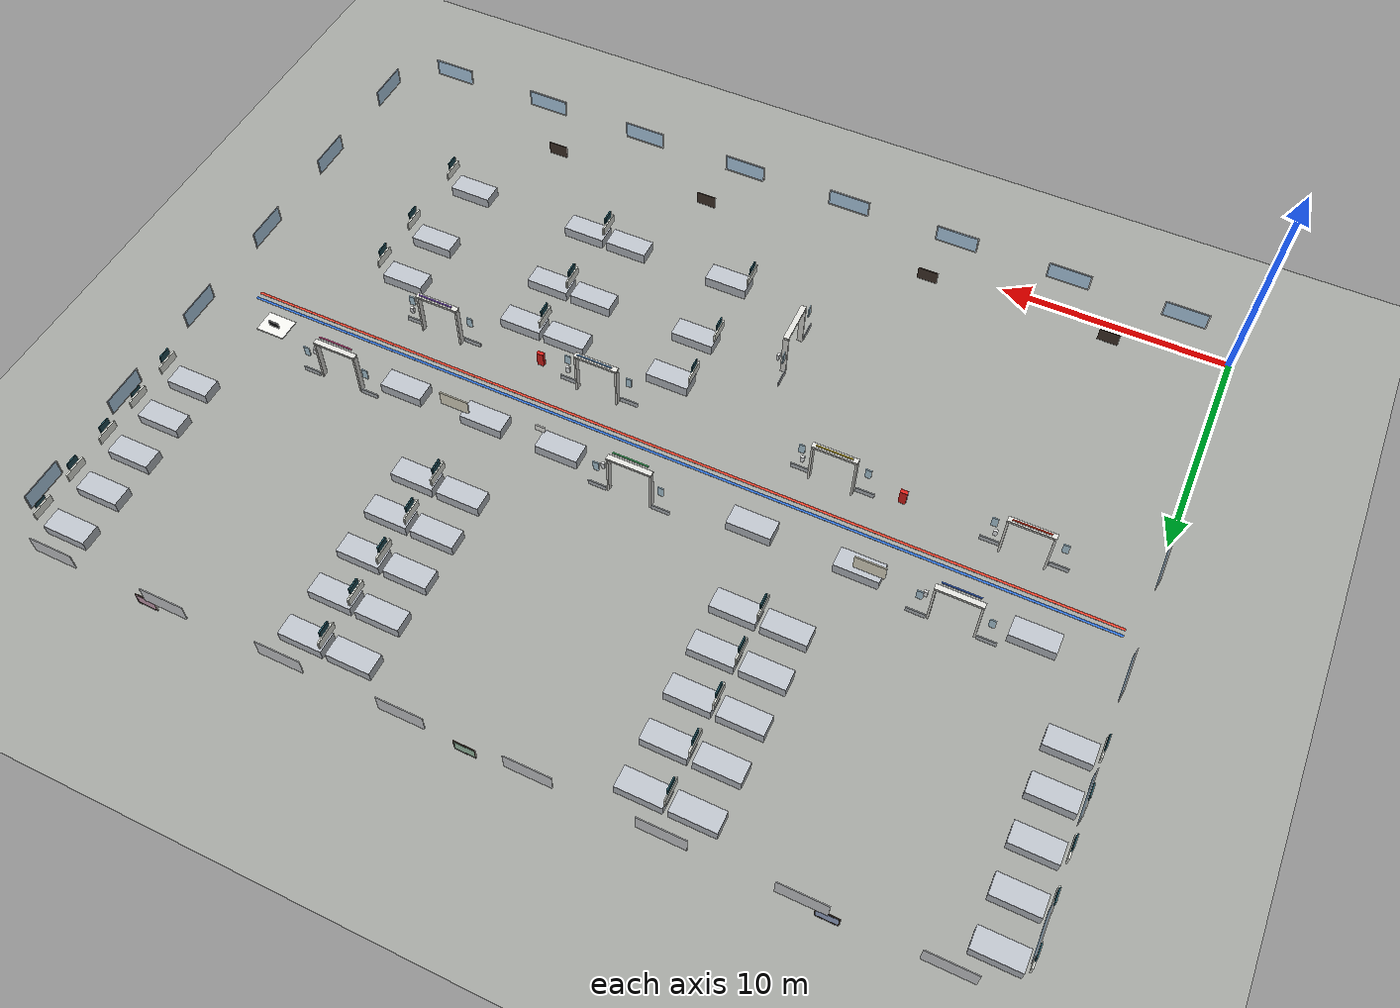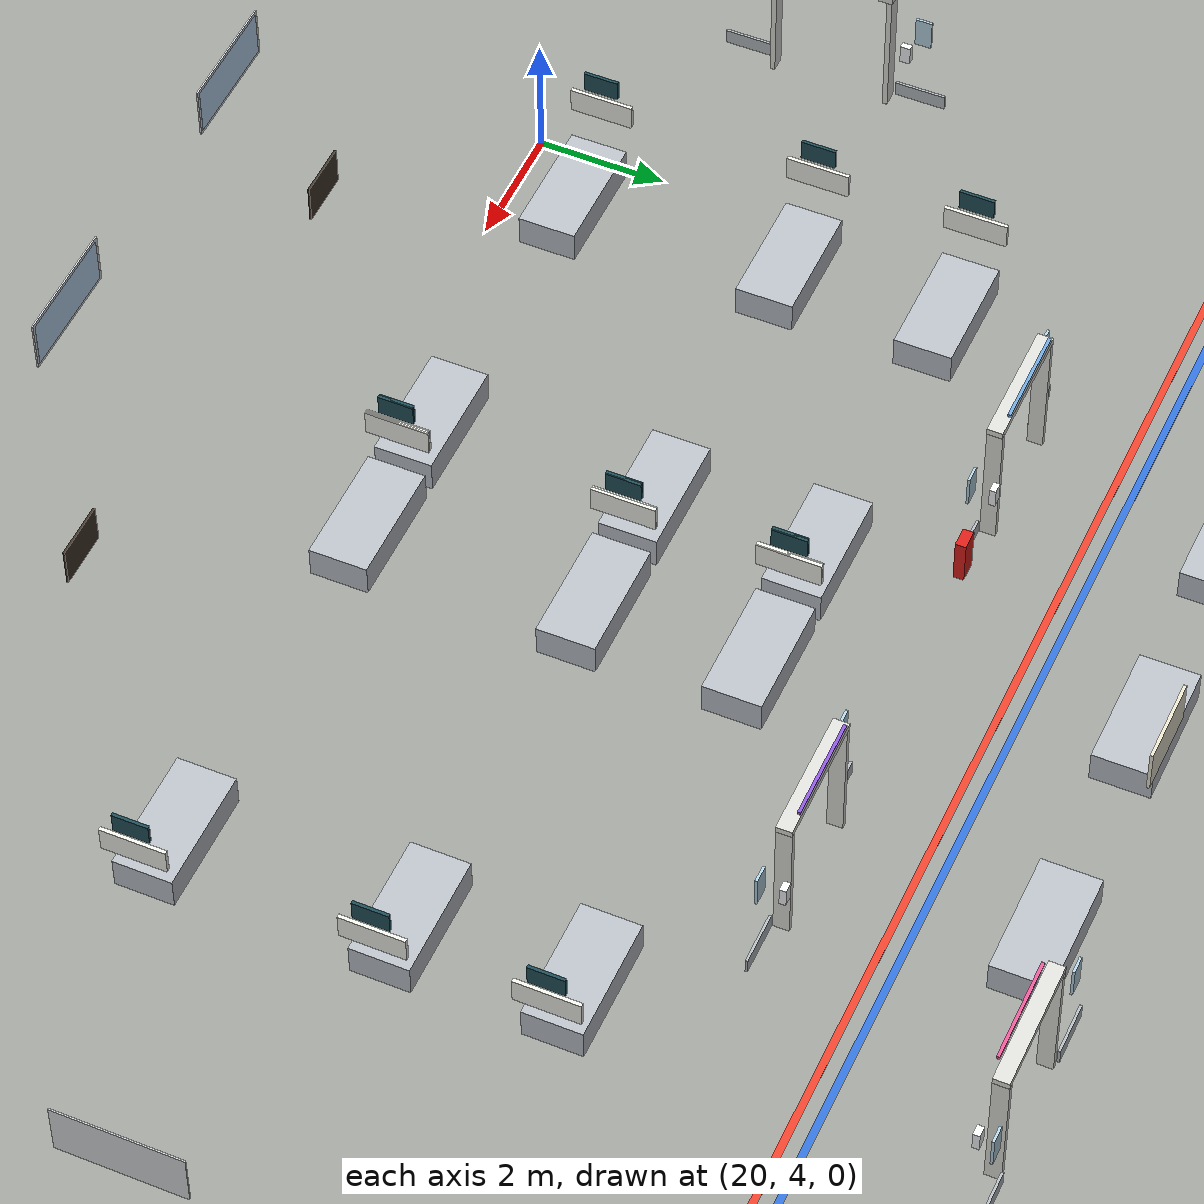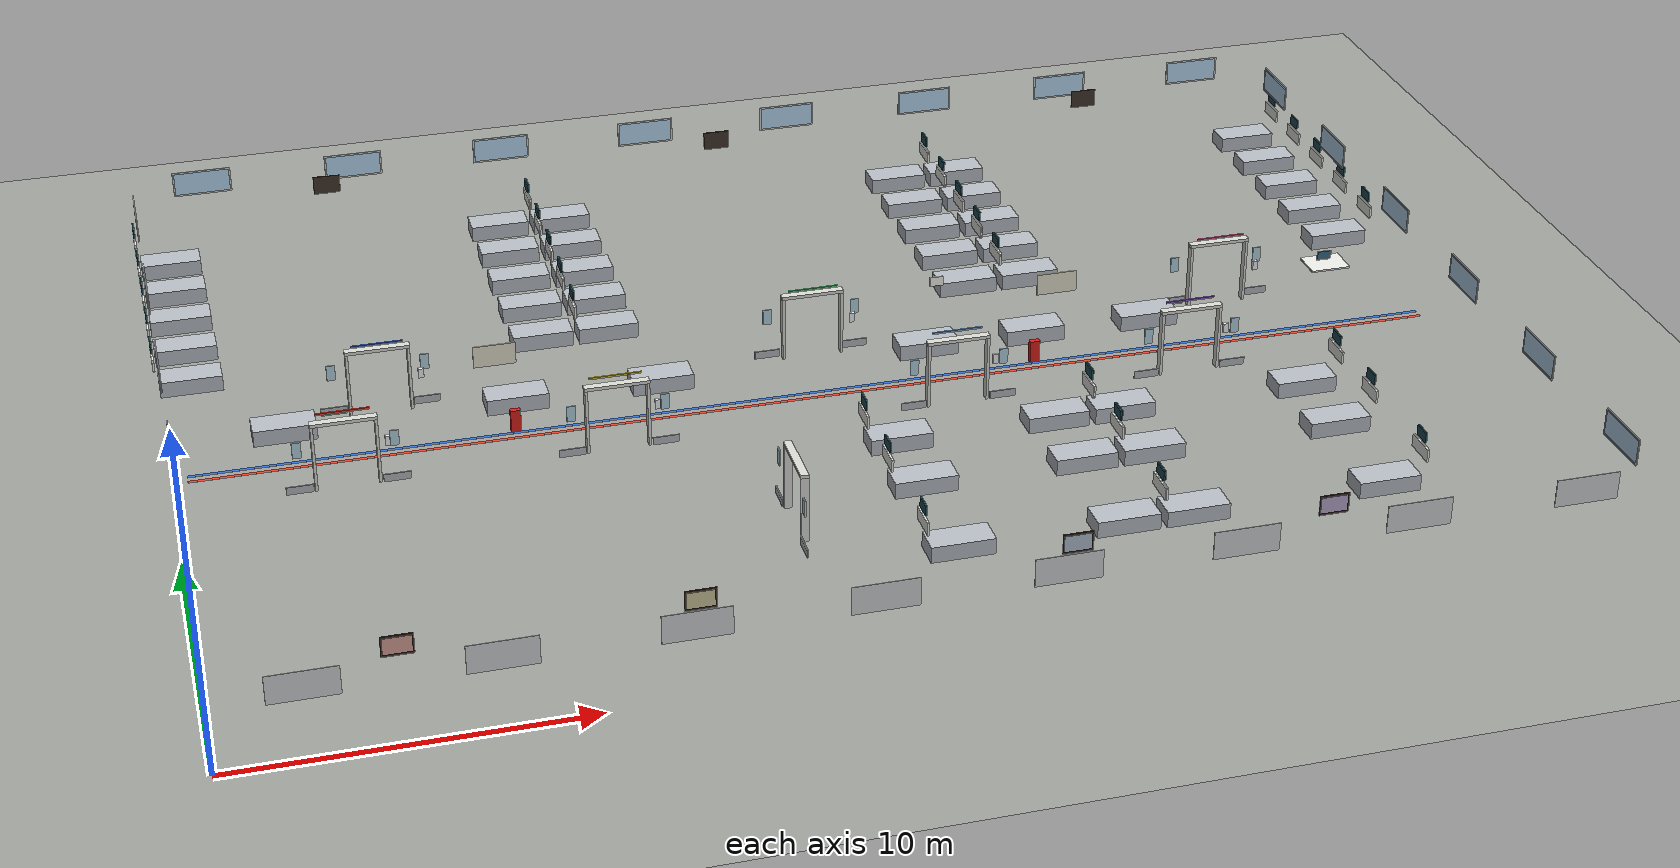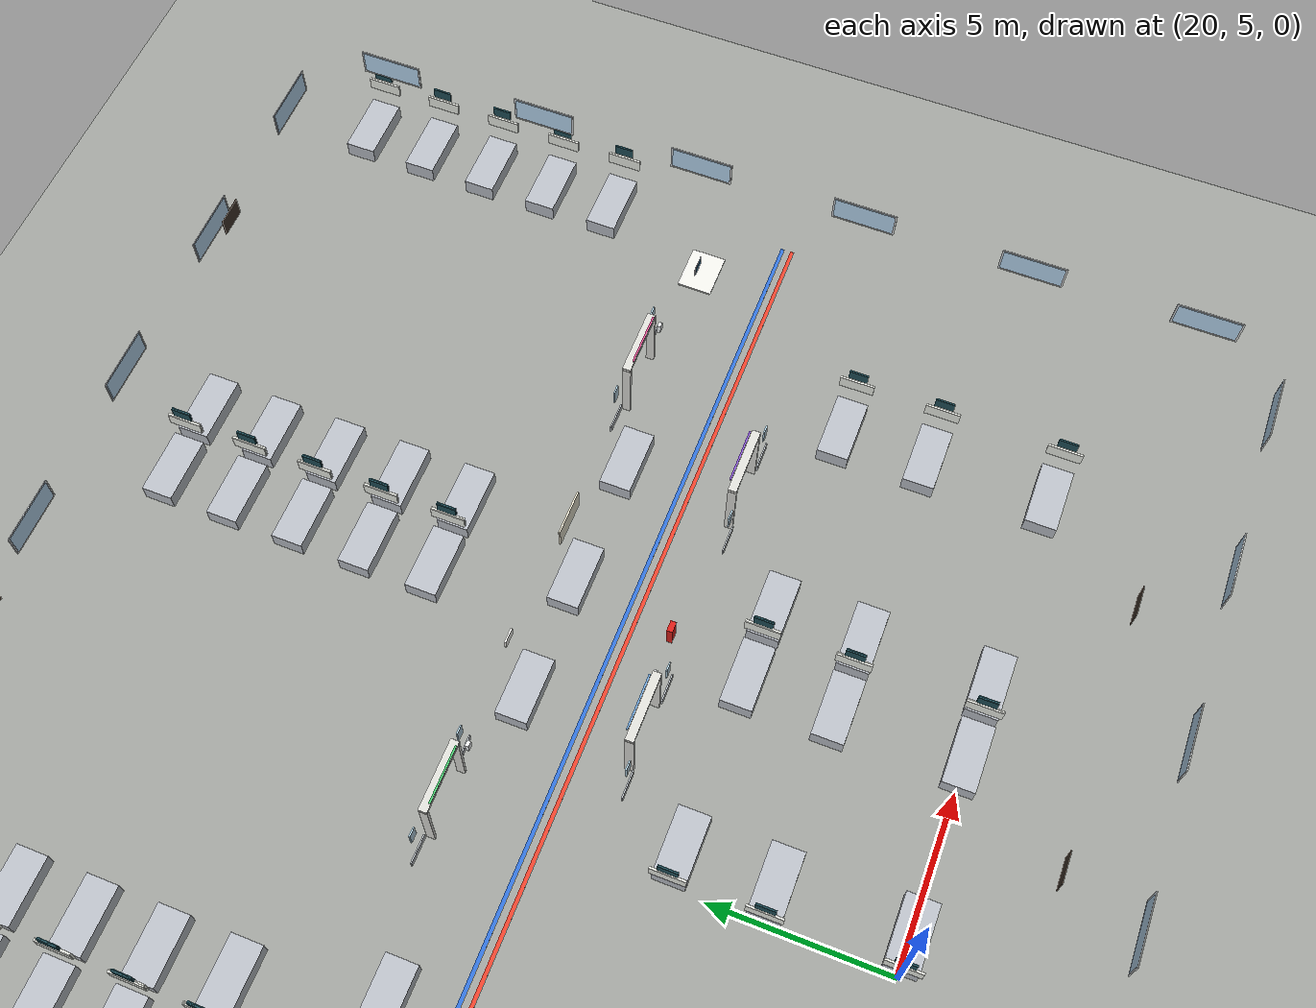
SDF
<sdf version="1.9">
 <world name="hospital">
  <plugin filename="gz-sim-physics-system" name="gz::sim::systems::Physics"/>
  <plugin filename="gz-sim-sensors-system" name="gz::sim::systems::Sensors">
   <render_engine>ogre2</render_engine>
  </plugin>
  <plugin filename="gz-sim-user-commands-system" name="gz::sim::systems::UserCommands"/>
  <plugin filename="gz-sim-scene-broadcaster-system" name="gz::sim::systems::SceneBroadcaster"/>
  <plugin filename="gz-sim-contact-system" name="gz::sim::systems::Contact"/>
  <physics type="dart">
   <max_step_size>0.01</max_step_size>
   <real_time_factor>0</real_time_factor>
   <real_time_update_rate>0</real_time_update_rate>
  </physics>
  <scene>
   <ambient>0.52 0.53 0.56 1</ambient>
   <background>0.70 0.76 0.84 1</background>
   <shadows>true</shadows>
   <grid>false</grid>
  </scene>
  <light type="directional" name="sun">
   <pose>12 10 14 0 0 0</pose>
   <diffuse>0.70 0.69 0.66 1</diffuse>
   <specular>0.16 0.16 0.16 1</specular>
   <direction>-0.45 0.30 -0.84</direction>
  </light>
  <model name="ground_plane">
   <static>true</static>
   <link name="link">
    <collision name="collision">
     <geometry><plane><normal>0 0 1</normal><size>200 200</size></plane></geometry>
    </collision>
    <visual name="visual">
     <pose>0 0 -0.03 0 0 0</pose>
     <cast_shadows>false</cast_shadows>
     <geometry><plane><normal>0 0 1</normal><size>200 200</size></plane></geometry>
     <material>
      <ambient>0.310 0.315 0.305 1.0</ambient>
      <diffuse>0.620 0.630 0.610 1.0</diffuse>
      <specular>0.14 0.14 0.14 1</specular>
      <emissive>0.000 0.000 0.000 1</emissive>
     </material>
    </visual>
   </link>
  </model>
  <model name="bed_0">
   <static>true</static>
   <pose>1.05 20.0 0.25 0 0 0</pose>
   <link name="link">
    <collision name="c"><geometry><box><size>1.9 0.8999999999999986 0.5</size></box></geometry></collision>
    <visual name="v">
     <visibility_flags>2</visibility_flags>
     <geometry><box><size>1.9 0.8999999999999986 0.5</size></box></geometry>
     <material>
      <ambient>0.360 0.370 0.385 1.0</ambient>
      <diffuse>0.720 0.740 0.770 1.0</diffuse>
      <specular>0.14 0.14 0.14 1</specular>
      <emissive>0.000 0.000 0.000 1</emissive>
     </material>
    </visual>
   </link>
  </model>
  <model name="bed_1">
   <static>true</static>
   <pose>11.95 20.0 0.25 0 0 0</pose>
   <link name="link">
    <collision name="c">
     <geometry><box><size>1.9000000000000004 0.8999999999999986 0.5</size></box></geometry>
    </collision>
    <visual name="v">
     <visibility_flags>2</visibility_flags>
     <geometry><box><size>1.9000000000000004 0.8999999999999986 0.5</size></box></geometry>
     <material>
      <ambient>0.360 0.370 0.385 1.0</ambient>
      <diffuse>0.720 0.740 0.770 1.0</diffuse>
      <specular>0.14 0.14 0.14 1</specular>
      <emissive>0.000 0.000 0.000 1</emissive>
     </material>
    </visual>
   </link>
  </model>
  <model name="bed_2">
   <static>true</static>
   <pose>1.05 24.0 0.25 0 0 0</pose>
   <link name="link">
    <collision name="c"><geometry><box><size>1.9 0.8999999999999986 0.5</size></box></geometry></collision>
    <visual name="v">
     <visibility_flags>2</visibility_flags>
     <geometry><box><size>1.9 0.8999999999999986 0.5</size></box></geometry>
     <material>
      <ambient>0.360 0.370 0.385 1.0</ambient>
      <diffuse>0.720 0.740 0.770 1.0</diffuse>
      <specular>0.14 0.14 0.14 1</specular>
      <emissive>0.000 0.000 0.000 1</emissive>
     </material>
    </visual>
   </link>
  </model>
  <model name="bed_3">
   <static>true</static>
   <pose>11.95 24.0 0.25 0 0 0</pose>
   <link name="link">
    <collision name="c">
     <geometry><box><size>1.9000000000000004 0.8999999999999986 0.5</size></box></geometry>
    </collision>
    <visual name="v">
     <visibility_flags>2</visibility_flags>
     <geometry><box><size>1.9000000000000004 0.8999999999999986 0.5</size></box></geometry>
     <material>
      <ambient>0.360 0.370 0.385 1.0</ambient>
      <diffuse>0.720 0.740 0.770 1.0</diffuse>
      <specular>0.14 0.14 0.14 1</specular>
      <emissive>0.000 0.000 0.000 1</emissive>
     </material>
    </visual>
   </link>
  </model>
  <model name="bed_4">
   <static>true</static>
   <pose>1.05 28.0 0.25 0 0 0</pose>
   <link name="link">
    <collision name="c"><geometry><box><size>1.9 0.8999999999999986 0.5</size></box></geometry></collision>
    <visual name="v">
     <visibility_flags>2</visibility_flags>
     <geometry><box><size>1.9 0.8999999999999986 0.5</size></box></geometry>
     <material>
      <ambient>0.360 0.370 0.385 1.0</ambient>
      <diffuse>0.720 0.740 0.770 1.0</diffuse>
      <specular>0.14 0.14 0.14 1</specular>
      <emissive>0.000 0.000 0.000 1</emissive>
     </material>
    </visual>
   </link>
  </model>
  <model name="bed_5">
   <static>true</static>
   <pose>11.95 28.0 0.25 0 0 0</pose>
   <link name="link">
    <collision name="c">
     <geometry><box><size>1.9000000000000004 0.8999999999999986 0.5</size></box></geometry>
    </collision>
    <visual name="v">
     <visibility_flags>2</visibility_flags>
     <geometry><box><size>1.9000000000000004 0.8999999999999986 0.5</size></box></geometry>
     <material>
      <ambient>0.360 0.370 0.385 1.0</ambient>
      <diffuse>0.720 0.740 0.770 1.0</diffuse>
      <specular>0.14 0.14 0.14 1</specular>
      <emissive>0.000 0.000 0.000 1</emissive>
     </material>
    </visual>
   </link>
  </model>
  <model name="bed_6">
   <static>true</static>
   <pose>14.05 20.0 0.25 0 0 0</pose>
   <link name="link">
    <collision name="c">
     <geometry><box><size>1.9000000000000004 0.8999999999999986 0.5</size></box></geometry>
    </collision>
    <visual name="v">
     <visibility_flags>2</visibility_flags>
     <geometry><box><size>1.9000000000000004 0.8999999999999986 0.5</size></box></geometry>
     <material>
      <ambient>0.360 0.370 0.385 1.0</ambient>
      <diffuse>0.720 0.740 0.770 1.0</diffuse>
      <specular>0.14 0.14 0.14 1</specular>
      <emissive>0.000 0.000 0.000 1</emissive>
     </material>
    </visual>
   </link>
  </model>
  <model name="bed_7">
   <static>true</static>
   <pose>25.95 20.0 0.25 0 0 0</pose>
   <link name="link">
    <collision name="c">
     <geometry><box><size>1.8999999999999986 0.8999999999999986 0.5</size></box></geometry>
    </collision>
    <visual name="v">
     <visibility_flags>2</visibility_flags>
     <geometry><box><size>1.8999999999999986 0.8999999999999986 0.5</size></box></geometry>
     <material>
      <ambient>0.360 0.370 0.385 1.0</ambient>
      <diffuse>0.720 0.740 0.770 1.0</diffuse>
      <specular>0.14 0.14 0.14 1</specular>
      <emissive>0.000 0.000 0.000 1</emissive>
     </material>
    </visual>
   </link>
  </model>
  <model name="bed_8">
   <static>true</static>
   <pose>14.05 24.0 0.25 0 0 0</pose>
   <link name="link">
    <collision name="c">
     <geometry><box><size>1.9000000000000004 0.8999999999999986 0.5</size></box></geometry>
    </collision>
    <visual name="v">
     <visibility_flags>2</visibility_flags>
     <geometry><box><size>1.9000000000000004 0.8999999999999986 0.5</size></box></geometry>
     <material>
      <ambient>0.360 0.370 0.385 1.0</ambient>
      <diffuse>0.720 0.740 0.770 1.0</diffuse>
      <specular>0.14 0.14 0.14 1</specular>
      <emissive>0.000 0.000 0.000 1</emissive>
     </material>
    </visual>
   </link>
  </model>
  <model name="bed_9">
   <static>true</static>
   <pose>25.95 24.0 0.25 0 0 0</pose>
   <link name="link">
    <collision name="c">
     <geometry><box><size>1.8999999999999986 0.8999999999999986 0.5</size></box></geometry>
    </collision>
    <visual name="v">
     <visibility_flags>2</visibility_flags>
     <geometry><box><size>1.8999999999999986 0.8999999999999986 0.5</size></box></geometry>
     <material>
      <ambient>0.360 0.370 0.385 1.0</ambient>
      <diffuse>0.720 0.740 0.770 1.0</diffuse>
      <specular>0.14 0.14 0.14 1</specular>
      <emissive>0.000 0.000 0.000 1</emissive>
     </material>
    </visual>
   </link>
  </model>
  <model name="bed_10">
   <static>true</static>
   <pose>14.05 28.0 0.25 0 0 0</pose>
   <link name="link">
    <collision name="c">
     <geometry><box><size>1.9000000000000004 0.8999999999999986 0.5</size></box></geometry>
    </collision>
    <visual name="v">
     <visibility_flags>2</visibility_flags>
     <geometry><box><size>1.9000000000000004 0.8999999999999986 0.5</size></box></geometry>
     <material>
      <ambient>0.360 0.370 0.385 1.0</ambient>
      <diffuse>0.720 0.740 0.770 1.0</diffuse>
      <specular>0.14 0.14 0.14 1</specular>
      <emissive>0.000 0.000 0.000 1</emissive>
     </material>
    </visual>
   </link>
  </model>
  <model name="bed_11">
   <static>true</static>
   <pose>25.95 28.0 0.25 0 0 0</pose>
   <link name="link">
    <collision name="c">
     <geometry><box><size>1.8999999999999986 0.8999999999999986 0.5</size></box></geometry>
    </collision>
    <visual name="v">
     <visibility_flags>2</visibility_flags>
     <geometry><box><size>1.8999999999999986 0.8999999999999986 0.5</size></box></geometry>
     <material>
      <ambient>0.360 0.370 0.385 1.0</ambient>
      <diffuse>0.720 0.740 0.770 1.0</diffuse>
      <specular>0.14 0.14 0.14 1</specular>
      <emissive>0.000 0.000 0.000 1</emissive>
     </material>
    </visual>
   </link>
  </model>
  <model name="bed_12">
   <static>true</static>
   <pose>28.05 20.0 0.25 0 0 0</pose>
   <link name="link">
    <collision name="c">
     <geometry><box><size>1.8999999999999986 0.8999999999999986 0.5</size></box></geometry>
    </collision>
    <visual name="v">
     <visibility_flags>2</visibility_flags>
     <geometry><box><size>1.8999999999999986 0.8999999999999986 0.5</size></box></geometry>
     <material>
      <ambient>0.360 0.370 0.385 1.0</ambient>
      <diffuse>0.720 0.740 0.770 1.0</diffuse>
      <specular>0.14 0.14 0.14 1</specular>
      <emissive>0.000 0.000 0.000 1</emissive>
     </material>
    </visual>
   </link>
  </model>
  <model name="bed_13">
   <static>true</static>
   <pose>38.95 20.0 0.25 0 0 0</pose>
   <link name="link">
    <collision name="c">
     <geometry><box><size>1.8999999999999986 0.8999999999999986 0.5</size></box></geometry>
    </collision>
    <visual name="v">
     <visibility_flags>2</visibility_flags>
     <geometry><box><size>1.8999999999999986 0.8999999999999986 0.5</size></box></geometry>
     <material>
      <ambient>0.360 0.370 0.385 1.0</ambient>
      <diffuse>0.720 0.740 0.770 1.0</diffuse>
      <specular>0.14 0.14 0.14 1</specular>
      <emissive>0.000 0.000 0.000 1</emissive>
     </material>
    </visual>
   </link>
  </model>
  <model name="bed_14">
   <static>true</static>
   <pose>28.05 24.0 0.25 0 0 0</pose>
   <link name="link">
    <collision name="c">
     <geometry><box><size>1.8999999999999986 0.8999999999999986 0.5</size></box></geometry>
    </collision>
    <visual name="v">
     <visibility_flags>2</visibility_flags>
     <geometry><box><size>1.8999999999999986 0.8999999999999986 0.5</size></box></geometry>
     <material>
      <ambient>0.360 0.370 0.385 1.0</ambient>
      <diffuse>0.720 0.740 0.770 1.0</diffuse>
      <specular>0.14 0.14 0.14 1</specular>
      <emissive>0.000 0.000 0.000 1</emissive>
     </material>
    </visual>
   </link>
  </model>
  <model name="bed_15">
   <static>true</static>
   <pose>38.95 24.0 0.25 0 0 0</pose>
   <link name="link">
    <collision name="c">
     <geometry><box><size>1.8999999999999986 0.8999999999999986 0.5</size></box></geometry>
    </collision>
    <visual name="v">
     <visibility_flags>2</visibility_flags>
     <geometry><box><size>1.8999999999999986 0.8999999999999986 0.5</size></box></geometry>
     <material>
      <ambient>0.360 0.370 0.385 1.0</ambient>
      <diffuse>0.720 0.740 0.770 1.0</diffuse>
      <specular>0.14 0.14 0.14 1</specular>
      <emissive>0.000 0.000 0.000 1</emissive>
     </material>
    </visual>
   </link>
  </model>
  <model name="bed_16">
   <static>true</static>
   <pose>28.05 28.0 0.25 0 0 0</pose>
   <link name="link">
    <collision name="c">
     <geometry><box><size>1.8999999999999986 0.8999999999999986 0.5</size></box></geometry>
    </collision>
    <visual name="v">
     <visibility_flags>2</visibility_flags>
     <geometry><box><size>1.8999999999999986 0.8999999999999986 0.5</size></box></geometry>
     <material>
      <ambient>0.360 0.370 0.385 1.0</ambient>
      <diffuse>0.720 0.740 0.770 1.0</diffuse>
      <specular>0.14 0.14 0.14 1</specular>
      <emissive>0.000 0.000 0.000 1</emissive>
     </material>
    </visual>
   </link>
  </model>
  <model name="bed_17">
   <static>true</static>
   <pose>38.95 28.0 0.25 0 0 0</pose>
   <link name="link">
    <collision name="c">
     <geometry><box><size>1.8999999999999986 0.8999999999999986 0.5</size></box></geometry>
    </collision>
    <visual name="v">
     <visibility_flags>2</visibility_flags>
     <geometry><box><size>1.8999999999999986 0.8999999999999986 0.5</size></box></geometry>
     <material>
      <ambient>0.360 0.370 0.385 1.0</ambient>
      <diffuse>0.720 0.740 0.770 1.0</diffuse>
      <specular>0.14 0.14 0.14 1</specular>
      <emissive>0.000 0.000 0.000 1</emissive>
     </material>
    </visual>
   </link>
  </model>
  <model name="bed_18">
   <static>true</static>
   <pose>21.05 5.0 0.25 0 0 0</pose>
   <link name="link">
    <collision name="c">
     <geometry><box><size>1.8999999999999986 0.9000000000000004 0.5</size></box></geometry>
    </collision>
    <visual name="v">
     <visibility_flags>2</visibility_flags>
     <geometry><box><size>1.8999999999999986 0.9000000000000004 0.5</size></box></geometry>
     <material>
      <ambient>0.360 0.370 0.385 1.0</ambient>
      <diffuse>0.720 0.740 0.770 1.0</diffuse>
      <specular>0.14 0.14 0.14 1</specular>
      <emissive>0.000 0.000 0.000 1</emissive>
     </material>
    </visual>
   </link>
  </model>
  <model name="bed_19">
   <static>true</static>
   <pose>25.95 5.0 0.25 0 0 0</pose>
   <link name="link">
    <collision name="c">
     <geometry><box><size>1.8999999999999986 0.9000000000000004 0.5</size></box></geometry>
    </collision>
    <visual name="v">
     <visibility_flags>2</visibility_flags>
     <geometry><box><size>1.8999999999999986 0.9000000000000004 0.5</size></box></geometry>
     <material>
      <ambient>0.360 0.370 0.385 1.0</ambient>
      <diffuse>0.720 0.740 0.770 1.0</diffuse>
      <specular>0.14 0.14 0.14 1</specular>
      <emissive>0.000 0.000 0.000 1</emissive>
     </material>
    </visual>
   </link>
  </model>
  <model name="bed_20">
   <static>true</static>
   <pose>21.05 8.5 0.25 0 0 0</pose>
   <link name="link">
    <collision name="c">
     <geometry><box><size>1.8999999999999986 0.8999999999999986 0.5</size></box></geometry>
    </collision>
    <visual name="v">
     <visibility_flags>2</visibility_flags>
     <geometry><box><size>1.8999999999999986 0.8999999999999986 0.5</size></box></geometry>
     <material>
      <ambient>0.360 0.370 0.385 1.0</ambient>
      <diffuse>0.720 0.740 0.770 1.0</diffuse>
      <specular>0.14 0.14 0.14 1</specular>
      <emissive>0.000 0.000 0.000 1</emissive>
     </material>
    </visual>
   </link>
  </model>
  <model name="bed_21">
   <static>true</static>
   <pose>25.95 8.5 0.25 0 0 0</pose>
   <link name="link">
    <collision name="c">
     <geometry><box><size>1.8999999999999986 0.8999999999999986 0.5</size></box></geometry>
    </collision>
    <visual name="v">
     <visibility_flags>2</visibility_flags>
     <geometry><box><size>1.8999999999999986 0.8999999999999986 0.5</size></box></geometry>
     <material>
      <ambient>0.360 0.370 0.385 1.0</ambient>
      <diffuse>0.720 0.740 0.770 1.0</diffuse>
      <specular>0.14 0.14 0.14 1</specular>
      <emissive>0.000 0.000 0.000 1</emissive>
     </material>
    </visual>
   </link>
  </model>
  <model name="bed_22">
   <static>true</static>
   <pose>28.05 5.0 0.25 0 0 0</pose>
   <link name="link">
    <collision name="c">
     <geometry><box><size>1.8999999999999986 0.9000000000000004 0.5</size></box></geometry>
    </collision>
    <visual name="v">
     <visibility_flags>2</visibility_flags>
     <geometry><box><size>1.8999999999999986 0.9000000000000004 0.5</size></box></geometry>
     <material>
      <ambient>0.360 0.370 0.385 1.0</ambient>
      <diffuse>0.720 0.740 0.770 1.0</diffuse>
      <specular>0.14 0.14 0.14 1</specular>
      <emissive>0.000 0.000 0.000 1</emissive>
     </material>
    </visual>
   </link>
  </model>
  <model name="bed_23">
   <static>true</static>
   <pose>33.95 5.0 0.25 0 0 0</pose>
   <link name="link">
    <collision name="c">
     <geometry><box><size>1.8999999999999986 0.9000000000000004 0.5</size></box></geometry>
    </collision>
    <visual name="v">
     <visibility_flags>2</visibility_flags>
     <geometry><box><size>1.8999999999999986 0.9000000000000004 0.5</size></box></geometry>
     <material>
      <ambient>0.360 0.370 0.385 1.0</ambient>
      <diffuse>0.720 0.740 0.770 1.0</diffuse>
      <specular>0.14 0.14 0.14 1</specular>
      <emissive>0.000 0.000 0.000 1</emissive>
     </material>
    </visual>
   </link>
  </model>
  <model name="bed_24">
   <static>true</static>
   <pose>28.05 8.5 0.25 0 0 0</pose>
   <link name="link">
    <collision name="c">
     <geometry><box><size>1.8999999999999986 0.8999999999999986 0.5</size></box></geometry>
    </collision>
    <visual name="v">
     <visibility_flags>2</visibility_flags>
     <geometry><box><size>1.8999999999999986 0.8999999999999986 0.5</size></box></geometry>
     <material>
      <ambient>0.360 0.370 0.385 1.0</ambient>
      <diffuse>0.720 0.740 0.770 1.0</diffuse>
      <specular>0.14 0.14 0.14 1</specular>
      <emissive>0.000 0.000 0.000 1</emissive>
     </material>
    </visual>
   </link>
  </model>
  <model name="bed_25">
   <static>true</static>
   <pose>33.95 8.5 0.25 0 0 0</pose>
   <link name="link">
    <collision name="c">
     <geometry><box><size>1.8999999999999986 0.8999999999999986 0.5</size></box></geometry>
    </collision>
    <visual name="v">
     <visibility_flags>2</visibility_flags>
     <geometry><box><size>1.8999999999999986 0.8999999999999986 0.5</size></box></geometry>
     <material>
      <ambient>0.360 0.370 0.385 1.0</ambient>
      <diffuse>0.720 0.740 0.770 1.0</diffuse>
      <specular>0.14 0.14 0.14 1</specular>
      <emissive>0.000 0.000 0.000 1</emissive>
     </material>
    </visual>
   </link>
  </model>
  <model name="bed_26">
   <static>true</static>
   <pose>15.0 16.3 0.25 0 0 0</pose>
   <link name="link">
    <collision name="c">
     <geometry><box><size>1.8999999999999986 0.9000000000000004 0.5</size></box></geometry>
    </collision>
    <visual name="v">
     <visibility_flags>2</visibility_flags>
     <geometry><box><size>1.8999999999999986 0.9000000000000004 0.5</size></box></geometry>
     <material>
      <ambient>0.360 0.370 0.385 1.0</ambient>
      <diffuse>0.720 0.740 0.770 1.0</diffuse>
      <specular>0.14 0.14 0.14 1</specular>
      <emissive>0.000 0.000 0.000 1</emissive>
     </material>
    </visual>
   </link>
  </model>
  <model name="bed_27">
   <static>true</static>
   <pose>23.5 16.3 0.25 0 0 0</pose>
   <link name="link">
    <collision name="c">
     <geometry><box><size>1.8999999999999986 0.9000000000000004 0.5</size></box></geometry>
    </collision>
    <visual name="v">
     <visibility_flags>2</visibility_flags>
     <geometry><box><size>1.8999999999999986 0.9000000000000004 0.5</size></box></geometry>
     <material>
      <ambient>0.360 0.370 0.385 1.0</ambient>
      <diffuse>0.720 0.740 0.770 1.0</diffuse>
      <specular>0.14 0.14 0.14 1</specular>
      <emissive>0.000 0.000 0.000 1</emissive>
     </material>
    </visual>
   </link>
  </model>
  <model name="bed_28">
   <static>true</static>
   <pose>3.5 16.3 0.25 0 0 0</pose>
   <link name="link">
    <collision name="c">
     <geometry><box><size>1.9000000000000004 0.9000000000000004 0.5</size></box></geometry>
    </collision>
    <visual name="v">
     <visibility_flags>2</visibility_flags>
     <geometry><box><size>1.9000000000000004 0.9000000000000004 0.5</size></box></geometry>
     <material>
      <ambient>0.360 0.370 0.385 1.0</ambient>
      <diffuse>0.720 0.740 0.770 1.0</diffuse>
      <specular>0.14 0.14 0.14 1</specular>
      <emissive>0.000 0.000 0.000 1</emissive>
     </material>
    </visual>
   </link>
  </model>
  <model name="bed_29">
   <static>true</static>
   <pose>10.5 16.3 0.25 0 0 0</pose>
   <link name="link">
    <collision name="c">
     <geometry><box><size>1.8999999999999986 0.9000000000000004 0.5</size></box></geometry>
    </collision>
    <visual name="v">
     <visibility_flags>2</visibility_flags>
     <geometry><box><size>1.8999999999999986 0.9000000000000004 0.5</size></box></geometry>
     <material>
      <ambient>0.360 0.370 0.385 1.0</ambient>
      <diffuse>0.720 0.740 0.770 1.0</diffuse>
      <specular>0.14 0.14 0.14 1</specular>
      <emissive>0.000 0.000 0.000 1</emissive>
     </material>
    </visual>
   </link>
  </model>
  <model name="bed_30">
   <static>true</static>
   <pose>27.0 16.3 0.25 0 0 0</pose>
   <link name="link">
    <collision name="c">
     <geometry><box><size>1.8999999999999986 0.9000000000000004 0.5</size></box></geometry>
    </collision>
    <visual name="v">
     <visibility_flags>2</visibility_flags>
     <geometry><box><size>1.8999999999999986 0.9000000000000004 0.5</size></box></geometry>
     <material>
      <ambient>0.360 0.370 0.385 1.0</ambient>
      <diffuse>0.720 0.740 0.770 1.0</diffuse>
      <specular>0.14 0.14 0.14 1</specular>
      <emissive>0.000 0.000 0.000 1</emissive>
     </material>
    </visual>
   </link>
  </model>
  <model name="bed_31">
   <static>true</static>
   <pose>30.8 16.3 0.25 0 0 0</pose>
   <link name="link">
    <collision name="c">
     <geometry><box><size>1.8999999999999986 0.9000000000000004 0.5</size></box></geometry>
    </collision>
    <visual name="v">
     <visibility_flags>2</visibility_flags>
     <geometry><box><size>1.8999999999999986 0.9000000000000004 0.5</size></box></geometry>
     <material>
      <ambient>0.360 0.370 0.385 1.0</ambient>
      <diffuse>0.720 0.740 0.770 1.0</diffuse>
      <specular>0.14 0.14 0.14 1</specular>
      <emissive>0.000 0.000 0.000 1</emissive>
     </material>
    </visual>
   </link>
  </model>
  <model name="bed_32">
   <static>true</static>
   <pose>1.05 22.0 0.25 0 0 0</pose>
   <link name="link">
    <collision name="c"><geometry><box><size>1.9 0.8999999999999986 0.5</size></box></geometry></collision>
    <visual name="v">
     <visibility_flags>2</visibility_flags>
     <geometry><box><size>1.9 0.8999999999999986 0.5</size></box></geometry>
     <material>
      <ambient>0.360 0.370 0.385 1.0</ambient>
      <diffuse>0.720 0.740 0.770 1.0</diffuse>
      <specular>0.14 0.14 0.14 1</specular>
      <emissive>0.000 0.000 0.000 1</emissive>
     </material>
    </visual>
   </link>
  </model>
  <model name="bed_33">
   <static>true</static>
   <pose>11.95 22.0 0.25 0 0 0</pose>
   <link name="link">
    <collision name="c">
     <geometry><box><size>1.9000000000000004 0.8999999999999986 0.5</size></box></geometry>
    </collision>
    <visual name="v">
     <visibility_flags>2</visibility_flags>
     <geometry><box><size>1.9000000000000004 0.8999999999999986 0.5</size></box></geometry>
     <material>
      <ambient>0.360 0.370 0.385 1.0</ambient>
      <diffuse>0.720 0.740 0.770 1.0</diffuse>
      <specular>0.14 0.14 0.14 1</specular>
      <emissive>0.000 0.000 0.000 1</emissive>
     </material>
    </visual>
   </link>
  </model>
  <model name="bed_34">
   <static>true</static>
   <pose>1.05 26.0 0.25 0 0 0</pose>
   <link name="link">
    <collision name="c"><geometry><box><size>1.9 0.8999999999999986 0.5</size></box></geometry></collision>
    <visual name="v">
     <visibility_flags>2</visibility_flags>
     <geometry><box><size>1.9 0.8999999999999986 0.5</size></box></geometry>
     <material>
      <ambient>0.360 0.370 0.385 1.0</ambient>
      <diffuse>0.720 0.740 0.770 1.0</diffuse>
      <specular>0.14 0.14 0.14 1</specular>
      <emissive>0.000 0.000 0.000 1</emissive>
     </material>
    </visual>
   </link>
  </model>
  <model name="bed_35">
   <static>true</static>
   <pose>11.95 26.0 0.25 0 0 0</pose>
   <link name="link">
    <collision name="c">
     <geometry><box><size>1.9000000000000004 0.8999999999999986 0.5</size></box></geometry>
    </collision>
    <visual name="v">
     <visibility_flags>2</visibility_flags>
     <geometry><box><size>1.9000000000000004 0.8999999999999986 0.5</size></box></geometry>
     <material>
      <ambient>0.360 0.370 0.385 1.0</ambient>
      <diffuse>0.720 0.740 0.770 1.0</diffuse>
      <specular>0.14 0.14 0.14 1</specular>
      <emissive>0.000 0.000 0.000 1</emissive>
     </material>
    </visual>
   </link>
  </model>
  <model name="bed_36">
   <static>true</static>
   <pose>14.05 22.0 0.25 0 0 0</pose>
   <link name="link">
    <collision name="c">
     <geometry><box><size>1.9000000000000004 0.8999999999999986 0.5</size></box></geometry>
    </collision>
    <visual name="v">
     <visibility_flags>2</visibility_flags>
     <geometry><box><size>1.9000000000000004 0.8999999999999986 0.5</size></box></geometry>
     <material>
      <ambient>0.360 0.370 0.385 1.0</ambient>
      <diffuse>0.720 0.740 0.770 1.0</diffuse>
      <specular>0.14 0.14 0.14 1</specular>
      <emissive>0.000 0.000 0.000 1</emissive>
     </material>
    </visual>
   </link>
  </model>
  <model name="bed_37">
   <static>true</static>
   <pose>25.95 22.0 0.25 0 0 0</pose>
   <link name="link">
    <collision name="c">
     <geometry><box><size>1.8999999999999986 0.8999999999999986 0.5</size></box></geometry>
    </collision>
    <visual name="v">
     <visibility_flags>2</visibility_flags>
     <geometry><box><size>1.8999999999999986 0.8999999999999986 0.5</size></box></geometry>
     <material>
      <ambient>0.360 0.370 0.385 1.0</ambient>
      <diffuse>0.720 0.740 0.770 1.0</diffuse>
      <specular>0.14 0.14 0.14 1</specular>
      <emissive>0.000 0.000 0.000 1</emissive>
     </material>
    </visual>
   </link>
  </model>
  <model name="bed_38">
   <static>true</static>
   <pose>14.05 26.0 0.25 0 0 0</pose>
   <link name="link">
    <collision name="c">
     <geometry><box><size>1.9000000000000004 0.8999999999999986 0.5</size></box></geometry>
    </collision>
    <visual name="v">
     <visibility_flags>2</visibility_flags>
     <geometry><box><size>1.9000000000000004 0.8999999999999986 0.5</size></box></geometry>
     <material>
      <ambient>0.360 0.370 0.385 1.0</ambient>
      <diffuse>0.720 0.740 0.770 1.0</diffuse>
      <specular>0.14 0.14 0.14 1</specular>
      <emissive>0.000 0.000 0.000 1</emissive>
     </material>
    </visual>
   </link>
  </model>
  <model name="bed_39">
   <static>true</static>
   <pose>25.95 26.0 0.25 0 0 0</pose>
   <link name="link">
    <collision name="c">
     <geometry><box><size>1.8999999999999986 0.8999999999999986 0.5</size></box></geometry>
    </collision>
    <visual name="v">
     <visibility_flags>2</visibility_flags>
     <geometry><box><size>1.8999999999999986 0.8999999999999986 0.5</size></box></geometry>
     <material>
      <ambient>0.360 0.370 0.385 1.0</ambient>
      <diffuse>0.720 0.740 0.770 1.0</diffuse>
      <specular>0.14 0.14 0.14 1</specular>
      <emissive>0.000 0.000 0.000 1</emissive>
     </material>
    </visual>
   </link>
  </model>
  <model name="bed_40">
   <static>true</static>
   <pose>28.05 22.0 0.25 0 0 0</pose>
   <link name="link">
    <collision name="c">
     <geometry><box><size>1.8999999999999986 0.8999999999999986 0.5</size></box></geometry>
    </collision>
    <visual name="v">
     <visibility_flags>2</visibility_flags>
     <geometry><box><size>1.8999999999999986 0.8999999999999986 0.5</size></box></geometry>
     <material>
      <ambient>0.360 0.370 0.385 1.0</ambient>
      <diffuse>0.720 0.740 0.770 1.0</diffuse>
      <specular>0.14 0.14 0.14 1</specular>
      <emissive>0.000 0.000 0.000 1</emissive>
     </material>
    </visual>
   </link>
  </model>
  <model name="bed_41">
   <static>true</static>
   <pose>38.95 22.0 0.25 0 0 0</pose>
   <link name="link">
    <collision name="c">
     <geometry><box><size>1.8999999999999986 0.8999999999999986 0.5</size></box></geometry>
    </collision>
    <visual name="v">
     <visibility_flags>2</visibility_flags>
     <geometry><box><size>1.8999999999999986 0.8999999999999986 0.5</size></box></geometry>
     <material>
      <ambient>0.360 0.370 0.385 1.0</ambient>
      <diffuse>0.720 0.740 0.770 1.0</diffuse>
      <specular>0.14 0.14 0.14 1</specular>
      <emissive>0.000 0.000 0.000 1</emissive>
     </material>
    </visual>
   </link>
  </model>
  <model name="bed_42">
   <static>true</static>
   <pose>28.05 26.0 0.25 0 0 0</pose>
   <link name="link">
    <collision name="c">
     <geometry><box><size>1.8999999999999986 0.8999999999999986 0.5</size></box></geometry>
    </collision>
    <visual name="v">
     <visibility_flags>2</visibility_flags>
     <geometry><box><size>1.8999999999999986 0.8999999999999986 0.5</size></box></geometry>
     <material>
      <ambient>0.360 0.370 0.385 1.0</ambient>
      <diffuse>0.720 0.740 0.770 1.0</diffuse>
      <specular>0.14 0.14 0.14 1</specular>
      <emissive>0.000 0.000 0.000 1</emissive>
     </material>
    </visual>
   </link>
  </model>
  <model name="bed_43">
   <static>true</static>
   <pose>38.95 26.0 0.25 0 0 0</pose>
   <link name="link">
    <collision name="c">
     <geometry><box><size>1.8999999999999986 0.8999999999999986 0.5</size></box></geometry>
    </collision>
    <visual name="v">
     <visibility_flags>2</visibility_flags>
     <geometry><box><size>1.8999999999999986 0.8999999999999986 0.5</size></box></geometry>
     <material>
      <ambient>0.360 0.370 0.385 1.0</ambient>
      <diffuse>0.720 0.740 0.770 1.0</diffuse>
      <specular>0.14 0.14 0.14 1</specular>
      <emissive>0.000 0.000 0.000 1</emissive>
     </material>
    </visual>
   </link>
  </model>
  <model name="bed_44">
   <static>true</static>
   <pose>21.05 11.0 0.25 0 0 0</pose>
   <link name="link">
    <collision name="c">
     <geometry><box><size>1.8999999999999986 0.8999999999999986 0.5</size></box></geometry>
    </collision>
    <visual name="v">
     <visibility_flags>2</visibility_flags>
     <geometry><box><size>1.8999999999999986 0.8999999999999986 0.5</size></box></geometry>
     <material>
      <ambient>0.360 0.370 0.385 1.0</ambient>
      <diffuse>0.720 0.740 0.770 1.0</diffuse>
      <specular>0.14 0.14 0.14 1</specular>
      <emissive>0.000 0.000 0.000 1</emissive>
     </material>
    </visual>
   </link>
  </model>
  <model name="bed_45">
   <static>true</static>
   <pose>25.95 11.0 0.25 0 0 0</pose>
   <link name="link">
    <collision name="c">
     <geometry><box><size>1.8999999999999986 0.8999999999999986 0.5</size></box></geometry>
    </collision>
    <visual name="v">
     <visibility_flags>2</visibility_flags>
     <geometry><box><size>1.8999999999999986 0.8999999999999986 0.5</size></box></geometry>
     <material>
      <ambient>0.360 0.370 0.385 1.0</ambient>
      <diffuse>0.720 0.740 0.770 1.0</diffuse>
      <specular>0.14 0.14 0.14 1</specular>
      <emissive>0.000 0.000 0.000 1</emissive>
     </material>
    </visual>
   </link>
  </model>
  <model name="bed_46">
   <static>true</static>
   <pose>28.05 11.0 0.25 0 0 0</pose>
   <link name="link">
    <collision name="c">
     <geometry><box><size>1.8999999999999986 0.8999999999999986 0.5</size></box></geometry>
    </collision>
    <visual name="v">
     <visibility_flags>2</visibility_flags>
     <geometry><box><size>1.8999999999999986 0.8999999999999986 0.5</size></box></geometry>
     <material>
      <ambient>0.360 0.370 0.385 1.0</ambient>
      <diffuse>0.720 0.740 0.770 1.0</diffuse>
      <specular>0.14 0.14 0.14 1</specular>
      <emissive>0.000 0.000 0.000 1</emissive>
     </material>
    </visual>
   </link>
  </model>
  <model name="bed_47">
   <static>true</static>
   <pose>33.95 11.0 0.25 0 0 0</pose>
   <link name="link">
    <collision name="c">
     <geometry><box><size>1.8999999999999986 0.8999999999999986 0.5</size></box></geometry>
    </collision>
    <visual name="v">
     <visibility_flags>2</visibility_flags>
     <geometry><box><size>1.8999999999999986 0.8999999999999986 0.5</size></box></geometry>
     <material>
      <ambient>0.360 0.370 0.385 1.0</ambient>
      <diffuse>0.720 0.740 0.770 1.0</diffuse>
      <specular>0.14 0.14 0.14 1</specular>
      <emissive>0.000 0.000 0.000 1</emissive>
     </material>
    </visual>
   </link>
  </model>
  <model name="bed_0_panel">
   <static>true</static>
   <pose>-0.010000000000000009 20.0 1.15 0 0 0</pose>
   <link name="link">
    <visual name="v">
     <cast_shadows>false</cast_shadows>
     <geometry><box><size>0.06 0.9899999999999985 0.4</size></box></geometry>
     <material>
      <ambient>0.460 0.465 0.450 1.0</ambient>
      <diffuse>0.920 0.930 0.900 1.0</diffuse>
      <specular>0.14 0.14 0.14 1</specular>
      <emissive>0.000 0.000 0.000 1</emissive>
     </material>
    </visual>
   </link>
  </model>
  <model name="bed_0_monitor">
   <static>true</static>
   <pose>-0.010000000000000009 20.0 1.615 0 0 0</pose>
   <link name="link">
    <visual name="v">
     <cast_shadows>false</cast_shadows>
     <geometry><box><size>0.05 0.5444999999999992 0.33</size></box></geometry>
     <material>
      <ambient>0.060 0.150 0.170 1.0</ambient>
      <diffuse>0.120 0.300 0.340 1.0</diffuse>
      <specular>0.14 0.14 0.14 1</specular>
      <emissive>0.042 0.105 0.119 1</emissive>
     </material>
    </visual>
   </link>
  </model>
  <model name="bed_1_panel">
   <static>true</static>
   <pose>13.01 20.0 1.15 0 0 0</pose>
   <link name="link">
    <visual name="v">
     <cast_shadows>false</cast_shadows>
     <geometry><box><size>0.06 0.9899999999999985 0.4</size></box></geometry>
     <material>
      <ambient>0.460 0.465 0.450 1.0</ambient>
      <diffuse>0.920 0.930 0.900 1.0</diffuse>
      <specular>0.14 0.14 0.14 1</specular>
      <emissive>0.000 0.000 0.000 1</emissive>
     </material>
    </visual>
   </link>
  </model>
  <model name="bed_1_monitor">
   <static>true</static>
   <pose>13.01 20.0 1.615 0 0 0</pose>
   <link name="link">
    <visual name="v">
     <cast_shadows>false</cast_shadows>
     <geometry><box><size>0.05 0.5444999999999992 0.33</size></box></geometry>
     <material>
      <ambient>0.060 0.150 0.170 1.0</ambient>
      <diffuse>0.120 0.300 0.340 1.0</diffuse>
      <specular>0.14 0.14 0.14 1</specular>
      <emissive>0.042 0.105 0.119 1</emissive>
     </material>
    </visual>
   </link>
  </model>
  <model name="bed_2_panel">
   <static>true</static>
   <pose>-0.010000000000000009 24.0 1.15 0 0 0</pose>
   <link name="link">
    <visual name="v">
     <cast_shadows>false</cast_shadows>
     <geometry><box><size>0.06 0.9899999999999985 0.4</size></box></geometry>
     <material>
      <ambient>0.460 0.465 0.450 1.0</ambient>
      <diffuse>0.920 0.930 0.900 1.0</diffuse>
      <specular>0.14 0.14 0.14 1</specular>
      <emissive>0.000 0.000 0.000 1</emissive>
     </material>
    </visual>
   </link>
  </model>
  <model name="bed_2_monitor">
   <static>true</static>
   <pose>-0.010000000000000009 24.0 1.615 0 0 0</pose>
   <link name="link">
    <visual name="v">
     <cast_shadows>false</cast_shadows>
     <geometry><box><size>0.05 0.5444999999999992 0.33</size></box></geometry>
     <material>
      <ambient>0.060 0.150 0.170 1.0</ambient>
      <diffuse>0.120 0.300 0.340 1.0</diffuse>
      <specular>0.14 0.14 0.14 1</specular>
      <emissive>0.042 0.105 0.119 1</emissive>
     </material>
    </visual>
   </link>
  </model>
  <model name="bed_3_panel">
   <static>true</static>
   <pose>13.01 24.0 1.15 0 0 0</pose>
   <link name="link">
    <visual name="v">
     <cast_shadows>false</cast_shadows>
     <geometry><box><size>0.06 0.9899999999999985 0.4</size></box></geometry>
     <material>
      <ambient>0.460 0.465 0.450 1.0</ambient>
      <diffuse>0.920 0.930 0.900 1.0</diffuse>
      <specular>0.14 0.14 0.14 1</specular>
      <emissive>0.000 0.000 0.000 1</emissive>
     </material>
    </visual>
   </link>
  </model>
  <model name="bed_3_monitor">
   <static>true</static>
   <pose>13.01 24.0 1.615 0 0 0</pose>
   <link name="link">
    <visual name="v">
     <cast_shadows>false</cast_shadows>
     <geometry><box><size>0.05 0.5444999999999992 0.33</size></box></geometry>
     <material>
      <ambient>0.060 0.150 0.170 1.0</ambient>
      <diffuse>0.120 0.300 0.340 1.0</diffuse>
      <specular>0.14 0.14 0.14 1</specular>
      <emissive>0.042 0.105 0.119 1</emissive>
     </material>
    </visual>
   </link>
  </model>
  <model name="bed_4_panel">
   <static>true</static>
   <pose>-0.010000000000000009 28.0 1.15 0 0 0</pose>
   <link name="link">
    <visual name="v">
     <cast_shadows>false</cast_shadows>
     <geometry><box><size>0.06 0.9899999999999985 0.4</size></box></geometry>
     <material>
      <ambient>0.460 0.465 0.450 1.0</ambient>
      <diffuse>0.920 0.930 0.900 1.0</diffuse>
      <specular>0.14 0.14 0.14 1</specular>
      <emissive>0.000 0.000 0.000 1</emissive>
     </material>
    </visual>
   </link>
  </model>
  <model name="bed_4_monitor">
   <static>true</static>
   <pose>-0.010000000000000009 28.0 1.615 0 0 0</pose>
   <link name="link">
    <visual name="v">
     <cast_shadows>false</cast_shadows>
     <geometry><box><size>0.05 0.5444999999999992 0.33</size></box></geometry>
     <material>
      <ambient>0.060 0.150 0.170 1.0</ambient>
      <diffuse>0.120 0.300 0.340 1.0</diffuse>
      <specular>0.14 0.14 0.14 1</specular>
      <emissive>0.042 0.105 0.119 1</emissive>
     </material>
    </visual>
   </link>
  </model>
  <model name="bed_5_panel">
   <static>true</static>
   <pose>13.01 28.0 1.15 0 0 0</pose>
   <link name="link">
    <visual name="v">
     <cast_shadows>false</cast_shadows>
     <geometry><box><size>0.06 0.9899999999999985 0.4</size></box></geometry>
     <material>
      <ambient>0.460 0.465 0.450 1.0</ambient>
      <diffuse>0.920 0.930 0.900 1.0</diffuse>
      <specular>0.14 0.14 0.14 1</specular>
      <emissive>0.000 0.000 0.000 1</emissive>
     </material>
    </visual>
   </link>
  </model>
  <model name="bed_5_monitor">
   <static>true</static>
   <pose>13.01 28.0 1.615 0 0 0</pose>
   <link name="link">
    <visual name="v">
     <cast_shadows>false</cast_shadows>
     <geometry><box><size>0.05 0.5444999999999992 0.33</size></box></geometry>
     <material>
      <ambient>0.060 0.150 0.170 1.0</ambient>
      <diffuse>0.120 0.300 0.340 1.0</diffuse>
      <specular>0.14 0.14 0.14 1</specular>
      <emissive>0.042 0.105 0.119 1</emissive>
     </material>
    </visual>
   </link>
  </model>
  <model name="bed_6_panel">
   <static>true</static>
   <pose>12.99 20.0 1.15 0 0 0</pose>
   <link name="link">
    <visual name="v">
     <cast_shadows>false</cast_shadows>
     <geometry><box><size>0.06 0.9899999999999985 0.4</size></box></geometry>
     <material>
      <ambient>0.460 0.465 0.450 1.0</ambient>
      <diffuse>0.920 0.930 0.900 1.0</diffuse>
      <specular>0.14 0.14 0.14 1</specular>
      <emissive>0.000 0.000 0.000 1</emissive>
     </material>
    </visual>
   </link>
  </model>
  <model name="bed_6_monitor">
   <static>true</static>
   <pose>12.99 20.0 1.615 0 0 0</pose>
   <link name="link">
    <visual name="v">
     <cast_shadows>false</cast_shadows>
     <geometry><box><size>0.05 0.5444999999999992 0.33</size></box></geometry>
     <material>
      <ambient>0.060 0.150 0.170 1.0</ambient>
      <diffuse>0.120 0.300 0.340 1.0</diffuse>
      <specular>0.14 0.14 0.14 1</specular>
      <emissive>0.042 0.105 0.119 1</emissive>
     </material>
    </visual>
   </link>
  </model>
  <model name="bed_7_panel">
   <static>true</static>
   <pose>27.009999999999998 20.0 1.15 0 0 0</pose>
   <link name="link">
    <visual name="v">
     <cast_shadows>false</cast_shadows>
     <geometry><box><size>0.06 0.9899999999999985 0.4</size></box></geometry>
     <material>
      <ambient>0.460 0.465 0.450 1.0</ambient>
      <diffuse>0.920 0.930 0.900 1.0</diffuse>
      <specular>0.14 0.14 0.14 1</specular>
      <emissive>0.000 0.000 0.000 1</emissive>
     </material>
    </visual>
   </link>
  </model>
  <model name="bed_7_monitor">
   <static>true</static>
   <pose>27.009999999999998 20.0 1.615 0 0 0</pose>
   <link name="link">
    <visual name="v">
     <cast_shadows>false</cast_shadows>
     <geometry><box><size>0.05 0.5444999999999992 0.33</size></box></geometry>
     <material>
      <ambient>0.060 0.150 0.170 1.0</ambient>
      <diffuse>0.120 0.300 0.340 1.0</diffuse>
      <specular>0.14 0.14 0.14 1</specular>
      <emissive>0.042 0.105 0.119 1</emissive>
     </material>
    </visual>
   </link>
  </model>
  <model name="bed_8_panel">
   <static>true</static>
   <pose>12.99 24.0 1.15 0 0 0</pose>
   <link name="link">
    <visual name="v">
     <cast_shadows>false</cast_shadows>
     <geometry><box><size>0.06 0.9899999999999985 0.4</size></box></geometry>
     <material>
      <ambient>0.460 0.465 0.450 1.0</ambient>
      <diffuse>0.920 0.930 0.900 1.0</diffuse>
      <specular>0.14 0.14 0.14 1</specular>
      <emissive>0.000 0.000 0.000 1</emissive>
     </material>
    </visual>
   </link>
  </model>
  <model name="bed_8_monitor">
   <static>true</static>
   <pose>12.99 24.0 1.615 0 0 0</pose>
   <link name="link">
    <visual name="v">
     <cast_shadows>false</cast_shadows>
     <geometry><box><size>0.05 0.5444999999999992 0.33</size></box></geometry>
     <material>
      <ambient>0.060 0.150 0.170 1.0</ambient>
      <diffuse>0.120 0.300 0.340 1.0</diffuse>
      <specular>0.14 0.14 0.14 1</specular>
      <emissive>0.042 0.105 0.119 1</emissive>
     </material>
    </visual>
   </link>
  </model>
  <model name="bed_9_panel">
   <static>true</static>
   <pose>27.009999999999998 24.0 1.15 0 0 0</pose>
   <link name="link">
    <visual name="v">
     <cast_shadows>false</cast_shadows>
     <geometry><box><size>0.06 0.9899999999999985 0.4</size></box></geometry>
     <material>
      <ambient>0.460 0.465 0.450 1.0</ambient>
      <diffuse>0.920 0.930 0.900 1.0</diffuse>
      <specular>0.14 0.14 0.14 1</specular>
      <emissive>0.000 0.000 0.000 1</emissive>
     </material>
    </visual>
   </link>
  </model>
  <model name="bed_9_monitor">
   <static>true</static>
   <pose>27.009999999999998 24.0 1.615 0 0 0</pose>
   <link name="link">
    <visual name="v">
     <cast_shadows>false</cast_shadows>
     <geometry><box><size>0.05 0.5444999999999992 0.33</size></box></geometry>
     <material>
      <ambient>0.060 0.150 0.170 1.0</ambient>
      <diffuse>0.120 0.300 0.340 1.0</diffuse>
      <specular>0.14 0.14 0.14 1</specular>
      <emissive>0.042 0.105 0.119 1</emissive>
     </material>
    </visual>
   </link>
  </model>
  <model name="bed_10_panel">
   <static>true</static>
   <pose>12.99 28.0 1.15 0 0 0</pose>
   <link name="link">
    <visual name="v">
     <cast_shadows>false</cast_shadows>
     <geometry><box><size>0.06 0.9899999999999985 0.4</size></box></geometry>
     <material>
      <ambient>0.460 0.465 0.450 1.0</ambient>
      <diffuse>0.920 0.930 0.900 1.0</diffuse>
      <specular>0.14 0.14 0.14 1</specular>
      <emissive>0.000 0.000 0.000 1</emissive>
     </material>
    </visual>
   </link>
  </model>
  <model name="bed_10_monitor">
   <static>true</static>
   <pose>12.99 28.0 1.615 0 0 0</pose>
   <link name="link">
    <visual name="v">
     <cast_shadows>false</cast_shadows>
     <geometry><box><size>0.05 0.5444999999999992 0.33</size></box></geometry>
     <material>
      <ambient>0.060 0.150 0.170 1.0</ambient>
      <diffuse>0.120 0.300 0.340 1.0</diffuse>
      <specular>0.14 0.14 0.14 1</specular>
      <emissive>0.042 0.105 0.119 1</emissive>
     </material>
    </visual>
   </link>
  </model>
  <model name="bed_11_panel">
   <static>true</static>
   <pose>27.009999999999998 28.0 1.15 0 0 0</pose>
   <link name="link">
    <visual name="v">
     <cast_shadows>false</cast_shadows>
     <geometry><box><size>0.06 0.9899999999999985 0.4</size></box></geometry>
     <material>
      <ambient>0.460 0.465 0.450 1.0</ambient>
      <diffuse>0.920 0.930 0.900 1.0</diffuse>
      <specular>0.14 0.14 0.14 1</specular>
      <emissive>0.000 0.000 0.000 1</emissive>
     </material>
    </visual>
   </link>
  </model>
  <model name="bed_11_monitor">
   <static>true</static>
   <pose>27.009999999999998 28.0 1.615 0 0 0</pose>
   <link name="link">
    <visual name="v">
     <cast_shadows>false</cast_shadows>
     <geometry><box><size>0.05 0.5444999999999992 0.33</size></box></geometry>
     <material>
      <ambient>0.060 0.150 0.170 1.0</ambient>
      <diffuse>0.120 0.300 0.340 1.0</diffuse>
      <specular>0.14 0.14 0.14 1</specular>
      <emissive>0.042 0.105 0.119 1</emissive>
     </material>
    </visual>
   </link>
  </model>
  <model name="bed_12_panel">
   <static>true</static>
   <pose>26.990000000000002 20.0 1.15 0 0 0</pose>
   <link name="link">
    <visual name="v">
     <cast_shadows>false</cast_shadows>
     <geometry><box><size>0.06 0.9899999999999985 0.4</size></box></geometry>
     <material>
      <ambient>0.460 0.465 0.450 1.0</ambient>
      <diffuse>0.920 0.930 0.900 1.0</diffuse>
      <specular>0.14 0.14 0.14 1</specular>
      <emissive>0.000 0.000 0.000 1</emissive>
     </material>
    </visual>
   </link>
  </model>
  <model name="bed_12_monitor">
   <static>true</static>
   <pose>26.990000000000002 20.0 1.615 0 0 0</pose>
   <link name="link">
    <visual name="v">
     <cast_shadows>false</cast_shadows>
     <geometry><box><size>0.05 0.5444999999999992 0.33</size></box></geometry>
     <material>
      <ambient>0.060 0.150 0.170 1.0</ambient>
      <diffuse>0.120 0.300 0.340 1.0</diffuse>
      <specular>0.14 0.14 0.14 1</specular>
      <emissive>0.042 0.105 0.119 1</emissive>
     </material>
    </visual>
   </link>
  </model>
  <model name="bed_13_panel">
   <static>true</static>
   <pose>40.010000000000005 20.0 1.15 0 0 0</pose>
   <link name="link">
    <visual name="v">
     <cast_shadows>false</cast_shadows>
     <geometry><box><size>0.06 0.9899999999999985 0.4</size></box></geometry>
     <material>
      <ambient>0.460 0.465 0.450 1.0</ambient>
      <diffuse>0.920 0.930 0.900 1.0</diffuse>
      <specular>0.14 0.14 0.14 1</specular>
      <emissive>0.000 0.000 0.000 1</emissive>
     </material>
    </visual>
   </link>
  </model>
  <model name="bed_13_monitor">
   <static>true</static>
   <pose>40.010000000000005 20.0 1.615 0 0 0</pose>
   <link name="link">
    <visual name="v">
     <cast_shadows>false</cast_shadows>
     <geometry><box><size>0.05 0.5444999999999992 0.33</size></box></geometry>
     <material>
      <ambient>0.060 0.150 0.170 1.0</ambient>
      <diffuse>0.120 0.300 0.340 1.0</diffuse>
      <specular>0.14 0.14 0.14 1</specular>
      <emissive>0.042 0.105 0.119 1</emissive>
     </material>
    </visual>
   </link>
  </model>
  <model name="bed_14_panel">
   <static>true</static>
   <pose>26.990000000000002 24.0 1.15 0 0 0</pose>
   <link name="link">
    <visual name="v">
     <cast_shadows>false</cast_shadows>
     <geometry><box><size>0.06 0.9899999999999985 0.4</size></box></geometry>
     <material>
      <ambient>0.460 0.465 0.450 1.0</ambient>
      <diffuse>0.920 0.930 0.900 1.0</diffuse>
      <specular>0.14 0.14 0.14 1</specular>
      <emissive>0.000 0.000 0.000 1</emissive>
     </material>
    </visual>
   </link>
  </model>
  <model name="bed_14_monitor">
   <static>true</static>
   <pose>26.990000000000002 24.0 1.615 0 0 0</pose>
   <link name="link">
    <visual name="v">
     <cast_shadows>false</cast_shadows>
     <geometry><box><size>0.05 0.5444999999999992 0.33</size></box></geometry>
     <material>
      <ambient>0.060 0.150 0.170 1.0</ambient>
      <diffuse>0.120 0.300 0.340 1.0</diffuse>
      <specular>0.14 0.14 0.14 1</specular>
      <emissive>0.042 0.105 0.119 1</emissive>
     </material>
    </visual>
   </link>
  </model>
  <model name="bed_15_panel">
   <static>true</static>
   <pose>40.010000000000005 24.0 1.15 0 0 0</pose>
   <link name="link">
    <visual name="v">
     <cast_shadows>false</cast_shadows>
     <geometry><box><size>0.06 0.9899999999999985 0.4</size></box></geometry>
     <material>
      <ambient>0.460 0.465 0.450 1.0</ambient>
      <diffuse>0.920 0.930 0.900 1.0</diffuse>
      <specular>0.14 0.14 0.14 1</specular>
      <emissive>0.000 0.000 0.000 1</emissive>
     </material>
    </visual>
   </link>
  </model>
  <model name="bed_15_monitor">
   <static>true</static>
   <pose>40.010000000000005 24.0 1.615 0 0 0</pose>
   <link name="link">
    <visual name="v">
     <cast_shadows>false</cast_shadows>
     <geometry><box><size>0.05 0.5444999999999992 0.33</size></box></geometry>
     <material>
      <ambient>0.060 0.150 0.170 1.0</ambient>
      <diffuse>0.120 0.300 0.340 1.0</diffuse>
      <specular>0.14 0.14 0.14 1</specular>
      <emissive>0.042 0.105 0.119 1</emissive>
     </material>
    </visual>
   </link>
  </model>
  <model name="bed_16_panel">
   <static>true</static>
   <pose>26.990000000000002 28.0 1.15 0 0 0</pose>
   <link name="link">
    <visual name="v">
     <cast_shadows>false</cast_shadows>
     <geometry><box><size>0.06 0.9899999999999985 0.4</size></box></geometry>
     <material>
      <ambient>0.460 0.465 0.450 1.0</ambient>
      <diffuse>0.920 0.930 0.900 1.0</diffuse>
      <specular>0.14 0.14 0.14 1</specular>
      <emissive>0.000 0.000 0.000 1</emissive>
     </material>
    </visual>
   </link>
  </model>
  <model name="bed_16_monitor">
   <static>true</static>
   <pose>26.990000000000002 28.0 1.615 0 0 0</pose>
   <link name="link">
    <visual name="v">
     <cast_shadows>false</cast_shadows>
     <geometry><box><size>0.05 0.5444999999999992 0.33</size></box></geometry>
     <material>
      <ambient>0.060 0.150 0.170 1.0</ambient>
      <diffuse>0.120 0.300 0.340 1.0</diffuse>
      <specular>0.14 0.14 0.14 1</specular>
      <emissive>0.042 0.105 0.119 1</emissive>
     </material>
    </visual>
   </link>
  </model>
  <model name="bed_17_panel">
   <static>true</static>
   <pose>40.010000000000005 28.0 1.15 0 0 0</pose>
   <link name="link">
    <visual name="v">
     <cast_shadows>false</cast_shadows>
     <geometry><box><size>0.06 0.9899999999999985 0.4</size></box></geometry>
     <material>
      <ambient>0.460 0.465 0.450 1.0</ambient>
      <diffuse>0.920 0.930 0.900 1.0</diffuse>
      <specular>0.14 0.14 0.14 1</specular>
      <emissive>0.000 0.000 0.000 1</emissive>
     </material>
    </visual>
   </link>
  </model>
  <model name="bed_17_monitor">
   <static>true</static>
   <pose>40.010000000000005 28.0 1.615 0 0 0</pose>
   <link name="link">
    <visual name="v">
     <cast_shadows>false</cast_shadows>
     <geometry><box><size>0.05 0.5444999999999992 0.33</size></box></geometry>
     <material>
      <ambient>0.060 0.150 0.170 1.0</ambient>
      <diffuse>0.120 0.300 0.340 1.0</diffuse>
      <specular>0.14 0.14 0.14 1</specular>
      <emissive>0.042 0.105 0.119 1</emissive>
     </material>
    </visual>
   </link>
  </model>
  <model name="bed_18_panel">
   <static>true</static>
   <pose>19.990000000000002 5.0 1.15 0 0 0</pose>
   <link name="link">
    <visual name="v">
     <cast_shadows>false</cast_shadows>
     <geometry><box><size>0.06 0.9900000000000004 0.4</size></box></geometry>
     <material>
      <ambient>0.460 0.465 0.450 1.0</ambient>
      <diffuse>0.920 0.930 0.900 1.0</diffuse>
      <specular>0.14 0.14 0.14 1</specular>
      <emissive>0.000 0.000 0.000 1</emissive>
     </material>
    </visual>
   </link>
  </model>
  <model name="bed_18_monitor">
   <static>true</static>
   <pose>19.990000000000002 5.0 1.615 0 0 0</pose>
   <link name="link">
    <visual name="v">
     <cast_shadows>false</cast_shadows>
     <geometry><box><size>0.05 0.5445000000000003 0.33</size></box></geometry>
     <material>
      <ambient>0.060 0.150 0.170 1.0</ambient>
      <diffuse>0.120 0.300 0.340 1.0</diffuse>
      <specular>0.14 0.14 0.14 1</specular>
      <emissive>0.042 0.105 0.119 1</emissive>
     </material>
    </visual>
   </link>
  </model>
  <model name="bed_19_panel">
   <static>true</static>
   <pose>27.009999999999998 5.0 1.15 0 0 0</pose>
   <link name="link">
    <visual name="v">
     <cast_shadows>false</cast_shadows>
     <geometry><box><size>0.06 0.9900000000000004 0.4</size></box></geometry>
     <material>
      <ambient>0.460 0.465 0.450 1.0</ambient>
      <diffuse>0.920 0.930 0.900 1.0</diffuse>
      <specular>0.14 0.14 0.14 1</specular>
      <emissive>0.000 0.000 0.000 1</emissive>
     </material>
    </visual>
   </link>
  </model>
  <model name="bed_19_monitor">
   <static>true</static>
   <pose>27.009999999999998 5.0 1.615 0 0 0</pose>
   <link name="link">
    <visual name="v">
     <cast_shadows>false</cast_shadows>
     <geometry><box><size>0.05 0.5445000000000003 0.33</size></box></geometry>
     <material>
      <ambient>0.060 0.150 0.170 1.0</ambient>
      <diffuse>0.120 0.300 0.340 1.0</diffuse>
      <specular>0.14 0.14 0.14 1</specular>
      <emissive>0.042 0.105 0.119 1</emissive>
     </material>
    </visual>
   </link>
  </model>
  <model name="bed_20_panel">
   <static>true</static>
   <pose>19.990000000000002 8.5 1.15 0 0 0</pose>
   <link name="link">
    <visual name="v">
     <cast_shadows>false</cast_shadows>
     <geometry><box><size>0.06 0.9899999999999985 0.4</size></box></geometry>
     <material>
      <ambient>0.460 0.465 0.450 1.0</ambient>
      <diffuse>0.920 0.930 0.900 1.0</diffuse>
      <specular>0.14 0.14 0.14 1</specular>
      <emissive>0.000 0.000 0.000 1</emissive>
     </material>
    </visual>
   </link>
  </model>
  <model name="bed_20_monitor">
   <static>true</static>
   <pose>19.990000000000002 8.5 1.615 0 0 0</pose>
   <link name="link">
    <visual name="v">
     <cast_shadows>false</cast_shadows>
     <geometry><box><size>0.05 0.5444999999999992 0.33</size></box></geometry>
     <material>
      <ambient>0.060 0.150 0.170 1.0</ambient>
      <diffuse>0.120 0.300 0.340 1.0</diffuse>
      <specular>0.14 0.14 0.14 1</specular>
      <emissive>0.042 0.105 0.119 1</emissive>
     </material>
    </visual>
   </link>
  </model>
  <model name="bed_21_panel">
   <static>true</static>
   <pose>27.009999999999998 8.5 1.15 0 0 0</pose>
   <link name="link">
    <visual name="v">
     <cast_shadows>false</cast_shadows>
     <geometry><box><size>0.06 0.9899999999999985 0.4</size></box></geometry>
     <material>
      <ambient>0.460 0.465 0.450 1.0</ambient>
      <diffuse>0.920 0.930 0.900 1.0</diffuse>
      <specular>0.14 0.14 0.14 1</specular>
      <emissive>0.000 0.000 0.000 1</emissive>
     </material>
    </visual>
   </link>
  </model>
  <model name="bed_21_monitor">
   <static>true</static>
   <pose>27.009999999999998 8.5 1.615 0 0 0</pose>
   <link name="link">
    <visual name="v">
     <cast_shadows>false</cast_shadows>
     <geometry><box><size>0.05 0.5444999999999992 0.33</size></box></geometry>
     <material>
      <ambient>0.060 0.150 0.170 1.0</ambient>
      <diffuse>0.120 0.300 0.340 1.0</diffuse>
      <specular>0.14 0.14 0.14 1</specular>
      <emissive>0.042 0.105 0.119 1</emissive>
     </material>
    </visual>
   </link>
  </model>
  <model name="bed_22_panel">
   <static>true</static>
   <pose>26.990000000000002 5.0 1.15 0 0 0</pose>
   <link name="link">
    <visual name="v">
     <cast_shadows>false</cast_shadows>
     <geometry><box><size>0.06 0.9900000000000004 0.4</size></box></geometry>
     <material>
      <ambient>0.460 0.465 0.450 1.0</ambient>
      <diffuse>0.920 0.930 0.900 1.0</diffuse>
      <specular>0.14 0.14 0.14 1</specular>
      <emissive>0.000 0.000 0.000 1</emissive>
     </material>
    </visual>
   </link>
  </model>
  <model name="bed_22_monitor">
   <static>true</static>
   <pose>26.990000000000002 5.0 1.615 0 0 0</pose>
   <link name="link">
    <visual name="v">
     <cast_shadows>false</cast_shadows>
     <geometry><box><size>0.05 0.5445000000000003 0.33</size></box></geometry>
     <material>
      <ambient>0.060 0.150 0.170 1.0</ambient>
      <diffuse>0.120 0.300 0.340 1.0</diffuse>
      <specular>0.14 0.14 0.14 1</specular>
      <emissive>0.042 0.105 0.119 1</emissive>
     </material>
    </visual>
   </link>
  </model>
  <model name="bed_23_panel">
   <static>true</static>
   <pose>35.010000000000005 5.0 1.15 0 0 0</pose>
   <link name="link">
    <visual name="v">
     <cast_shadows>false</cast_shadows>
     <geometry><box><size>0.06 0.9900000000000004 0.4</size></box></geometry>
     <material>
      <ambient>0.460 0.465 0.450 1.0</ambient>
      <diffuse>0.920 0.930 0.900 1.0</diffuse>
      <specular>0.14 0.14 0.14 1</specular>
      <emissive>0.000 0.000 0.000 1</emissive>
     </material>
    </visual>
   </link>
  </model>
  <model name="bed_23_monitor">
   <static>true</static>
   <pose>35.010000000000005 5.0 1.615 0 0 0</pose>
   <link name="link">
    <visual name="v">
     <cast_shadows>false</cast_shadows>
     <geometry><box><size>0.05 0.5445000000000003 0.33</size></box></geometry>
     <material>
      <ambient>0.060 0.150 0.170 1.0</ambient>
      <diffuse>0.120 0.300 0.340 1.0</diffuse>
      <specular>0.14 0.14 0.14 1</specular>
      <emissive>0.042 0.105 0.119 1</emissive>
     </material>
    </visual>
   </link>
  </model>
  <model name="bed_24_panel">
   <static>true</static>
   <pose>26.990000000000002 8.5 1.15 0 0 0</pose>
   <link name="link">
    <visual name="v">
     <cast_shadows>false</cast_shadows>
     <geometry><box><size>0.06 0.9899999999999985 0.4</size></box></geometry>
     <material>
      <ambient>0.460 0.465 0.450 1.0</ambient>
      <diffuse>0.920 0.930 0.900 1.0</diffuse>
      <specular>0.14 0.14 0.14 1</specular>
      <emissive>0.000 0.000 0.000 1</emissive>
     </material>
    </visual>
   </link>
  </model>
  <model name="bed_24_monitor">
   <static>true</static>
   <pose>26.990000000000002 8.5 1.615 0 0 0</pose>
   <link name="link">
    <visual name="v">
     <cast_shadows>false</cast_shadows>
     <geometry><box><size>0.05 0.5444999999999992 0.33</size></box></geometry>
     <material>
      <ambient>0.060 0.150 0.170 1.0</ambient>
      <diffuse>0.120 0.300 0.340 1.0</diffuse>
      <specular>0.14 0.14 0.14 1</specular>
      <emissive>0.042 0.105 0.119 1</emissive>
     </material>
    </visual>
   </link>
  </model>
  <model name="bed_25_panel">
   <static>true</static>
   <pose>35.010000000000005 8.5 1.15 0 0 0</pose>
   <link name="link">
    <visual name="v">
     <cast_shadows>false</cast_shadows>
     <geometry><box><size>0.06 0.9899999999999985 0.4</size></box></geometry>
     <material>
      <ambient>0.460 0.465 0.450 1.0</ambient>
      <diffuse>0.920 0.930 0.900 1.0</diffuse>
      <specular>0.14 0.14 0.14 1</specular>
      <emissive>0.000 0.000 0.000 1</emissive>
     </material>
    </visual>
   </link>
  </model>
  <model name="bed_25_monitor">
   <static>true</static>
   <pose>35.010000000000005 8.5 1.615 0 0 0</pose>
   <link name="link">
    <visual name="v">
     <cast_shadows>false</cast_shadows>
     <geometry><box><size>0.05 0.5444999999999992 0.33</size></box></geometry>
     <material>
      <ambient>0.060 0.150 0.170 1.0</ambient>
      <diffuse>0.120 0.300 0.340 1.0</diffuse>
      <specular>0.14 0.14 0.14 1</specular>
      <emissive>0.042 0.105 0.119 1</emissive>
     </material>
    </visual>
   </link>
  </model>
  <model name="bed_32_panel">
   <static>true</static>
   <pose>-0.010000000000000009 22.0 1.15 0 0 0</pose>
   <link name="link">
    <visual name="v">
     <cast_shadows>false</cast_shadows>
     <geometry><box><size>0.06 0.9899999999999985 0.4</size></box></geometry>
     <material>
      <ambient>0.460 0.465 0.450 1.0</ambient>
      <diffuse>0.920 0.930 0.900 1.0</diffuse>
      <specular>0.14 0.14 0.14 1</specular>
      <emissive>0.000 0.000 0.000 1</emissive>
     </material>
    </visual>
   </link>
  </model>
  <model name="bed_32_monitor">
   <static>true</static>
   <pose>-0.010000000000000009 22.0 1.615 0 0 0</pose>
   <link name="link">
    <visual name="v">
     <cast_shadows>false</cast_shadows>
     <geometry><box><size>0.05 0.5444999999999992 0.33</size></box></geometry>
     <material>
      <ambient>0.060 0.150 0.170 1.0</ambient>
      <diffuse>0.120 0.300 0.340 1.0</diffuse>
      <specular>0.14 0.14 0.14 1</specular>
      <emissive>0.042 0.105 0.119 1</emissive>
     </material>
    </visual>
   </link>
  </model>
  <model name="bed_33_panel">
   <static>true</static>
   <pose>13.01 22.0 1.15 0 0 0</pose>
   <link name="link">
    <visual name="v">
     <cast_shadows>false</cast_shadows>
     <geometry><box><size>0.06 0.9899999999999985 0.4</size></box></geometry>
     <material>
      <ambient>0.460 0.465 0.450 1.0</ambient>
      <diffuse>0.920 0.930 0.900 1.0</diffuse>
      <specular>0.14 0.14 0.14 1</specular>
      <emissive>0.000 0.000 0.000 1</emissive>
     </material>
    </visual>
   </link>
  </model>
  <model name="bed_33_monitor">
   <static>true</static>
   <pose>13.01 22.0 1.615 0 0 0</pose>
   <link name="link">
    <visual name="v">
     <cast_shadows>false</cast_shadows>
     <geometry><box><size>0.05 0.5444999999999992 0.33</size></box></geometry>
     <material>
      <ambient>0.060 0.150 0.170 1.0</ambient>
      <diffuse>0.120 0.300 0.340 1.0</diffuse>
      <specular>0.14 0.14 0.14 1</specular>
      <emissive>0.042 0.105 0.119 1</emissive>
     </material>
    </visual>
   </link>
  </model>
  <model name="bed_34_panel">
   <static>true</static>
   <pose>-0.010000000000000009 26.0 1.15 0 0 0</pose>
   <link name="link">
    <visual name="v">
     <cast_shadows>false</cast_shadows>
     <geometry><box><size>0.06 0.9899999999999985 0.4</size></box></geometry>
     <material>
      <ambient>0.460 0.465 0.450 1.0</ambient>
      <diffuse>0.920 0.930 0.900 1.0</diffuse>
      <specular>0.14 0.14 0.14 1</specular>
      <emissive>0.000 0.000 0.000 1</emissive>
     </material>
    </visual>
   </link>
  </model>
  <model name="bed_34_monitor">
   <static>true</static>
   <pose>-0.010000000000000009 26.0 1.615 0 0 0</pose>
   <link name="link">
    <visual name="v">
     <cast_shadows>false</cast_shadows>
     <geometry><box><size>0.05 0.5444999999999992 0.33</size></box></geometry>
     <material>
      <ambient>0.060 0.150 0.170 1.0</ambient>
      <diffuse>0.120 0.300 0.340 1.0</diffuse>
      <specular>0.14 0.14 0.14 1</specular>
      <emissive>0.042 0.105 0.119 1</emissive>
     </material>
    </visual>
   </link>
  </model>
  <model name="bed_35_panel">
   <static>true</static>
   <pose>13.01 26.0 1.15 0 0 0</pose>
   <link name="link">
    <visual name="v">
     <cast_shadows>false</cast_shadows>
     <geometry><box><size>0.06 0.9899999999999985 0.4</size></box></geometry>
     <material>
      <ambient>0.460 0.465 0.450 1.0</ambient>
      <diffuse>0.920 0.930 0.900 1.0</diffuse>
      <specular>0.14 0.14 0.14 1</specular>
      <emissive>0.000 0.000 0.000 1</emissive>
     </material>
    </visual>
   </link>
  </model>
  <model name="bed_35_monitor">
   <static>true</static>
   <pose>13.01 26.0 1.615 0 0 0</pose>
   <link name="link">
    <visual name="v">
     <cast_shadows>false</cast_shadows>
     <geometry><box><size>0.05 0.5444999999999992 0.33</size></box></geometry>
     <material>
      <ambient>0.060 0.150 0.170 1.0</ambient>
      <diffuse>0.120 0.300 0.340 1.0</diffuse>
      <specular>0.14 0.14 0.14 1</specular>
      <emissive>0.042 0.105 0.119 1</emissive>
     </material>
    </visual>
   </link>
  </model>
  <model name="bed_36_panel">
   <static>true</static>
   <pose>12.99 22.0 1.15 0 0 0</pose>
   <link name="link">
    <visual name="v">
     <cast_shadows>false</cast_shadows>
     <geometry><box><size>0.06 0.9899999999999985 0.4</size></box></geometry>
     <material>
      <ambient>0.460 0.465 0.450 1.0</ambient>
      <diffuse>0.920 0.930 0.900 1.0</diffuse>
      <specular>0.14 0.14 0.14 1</specular>
      <emissive>0.000 0.000 0.000 1</emissive>
     </material>
    </visual>
   </link>
  </model>
  <model name="bed_36_monitor">
   <static>true</static>
   <pose>12.99 22.0 1.615 0 0 0</pose>
   <link name="link">
    <visual name="v">
     <cast_shadows>false</cast_shadows>
     <geometry><box><size>0.05 0.5444999999999992 0.33</size></box></geometry>
     <material>
      <ambient>0.060 0.150 0.170 1.0</ambient>
      <diffuse>0.120 0.300 0.340 1.0</diffuse>
      <specular>0.14 0.14 0.14 1</specular>
      <emissive>0.042 0.105 0.119 1</emissive>
     </material>
    </visual>
   </link>
  </model>
  <model name="bed_37_panel">
   <static>true</static>
   <pose>27.009999999999998 22.0 1.15 0 0 0</pose>
   <link name="link">
    <visual name="v">
     <cast_shadows>false</cast_shadows>
     <geometry><box><size>0.06 0.9899999999999985 0.4</size></box></geometry>
     <material>
      <ambient>0.460 0.465 0.450 1.0</ambient>
      <diffuse>0.920 0.930 0.900 1.0</diffuse>
      <specular>0.14 0.14 0.14 1</specular>
      <emissive>0.000 0.000 0.000 1</emissive>
     </material>
    </visual>
   </link>
  </model>
  <model name="bed_37_monitor">
   <static>true</static>
   <pose>27.009999999999998 22.0 1.615 0 0 0</pose>
   <link name="link">
    <visual name="v">
     <cast_shadows>false</cast_shadows>
     <geometry><box><size>0.05 0.5444999999999992 0.33</size></box></geometry>
     <material>
      <ambient>0.060 0.150 0.170 1.0</ambient>
      <diffuse>0.120 0.300 0.340 1.0</diffuse>
      <specular>0.14 0.14 0.14 1</specular>
      <emissive>0.042 0.105 0.119 1</emissive>
     </material>
    </visual>
   </link>
  </model>
  <model name="bed_38_panel">
   <static>true</static>
   <pose>12.99 26.0 1.15 0 0 0</pose>
   <link name="link">
    <visual name="v">
     <cast_shadows>false</cast_shadows>
     <geometry><box><size>0.06 0.9899999999999985 0.4</size></box></geometry>
     <material>
      <ambient>0.460 0.465 0.450 1.0</ambient>
      <diffuse>0.920 0.930 0.900 1.0</diffuse>
      <specular>0.14 0.14 0.14 1</specular>
      <emissive>0.000 0.000 0.000 1</emissive>
     </material>
    </visual>
   </link>
  </model>
  <model name="bed_38_monitor">
   <static>true</static>
   <pose>12.99 26.0 1.615 0 0 0</pose>
   <link name="link">
    <visual name="v">
     <cast_shadows>false</cast_shadows>
     <geometry><box><size>0.05 0.5444999999999992 0.33</size></box></geometry>
     <material>
      <ambient>0.060 0.150 0.170 1.0</ambient>
      <diffuse>0.120 0.300 0.340 1.0</diffuse>
      <specular>0.14 0.14 0.14 1</specular>
      <emissive>0.042 0.105 0.119 1</emissive>
     </material>
    </visual>
   </link>
  </model>
  <model name="bed_39_panel">
   <static>true</static>
   <pose>27.009999999999998 26.0 1.15 0 0 0</pose>
   <link name="link">
    <visual name="v">
     <cast_shadows>false</cast_shadows>
     <geometry><box><size>0.06 0.9899999999999985 0.4</size></box></geometry>
     <material>
      <ambient>0.460 0.465 0.450 1.0</ambient>
      <diffuse>0.920 0.930 0.900 1.0</diffuse>
      <specular>0.14 0.14 0.14 1</specular>
      <emissive>0.000 0.000 0.000 1</emissive>
     </material>
    </visual>
   </link>
  </model>
  <model name="bed_39_monitor">
   <static>true</static>
   <pose>27.009999999999998 26.0 1.615 0 0 0</pose>
   <link name="link">
    <visual name="v">
     <cast_shadows>false</cast_shadows>
     <geometry><box><size>0.05 0.5444999999999992 0.33</size></box></geometry>
     <material>
      <ambient>0.060 0.150 0.170 1.0</ambient>
      <diffuse>0.120 0.300 0.340 1.0</diffuse>
      <specular>0.14 0.14 0.14 1</specular>
      <emissive>0.042 0.105 0.119 1</emissive>
     </material>
    </visual>
   </link>
  </model>
  <model name="bed_40_panel">
   <static>true</static>
   <pose>26.990000000000002 22.0 1.15 0 0 0</pose>
   <link name="link">
    <visual name="v">
     <cast_shadows>false</cast_shadows>
     <geometry><box><size>0.06 0.9899999999999985 0.4</size></box></geometry>
     <material>
      <ambient>0.460 0.465 0.450 1.0</ambient>
      <diffuse>0.920 0.930 0.900 1.0</diffuse>
      <specular>0.14 0.14 0.14 1</specular>
      <emissive>0.000 0.000 0.000 1</emissive>
     </material>
    </visual>
   </link>
  </model>
  <model name="bed_40_monitor">
   <static>true</static>
   <pose>26.990000000000002 22.0 1.615 0 0 0</pose>
   <link name="link">
    <visual name="v">
     <cast_shadows>false</cast_shadows>
     <geometry><box><size>0.05 0.5444999999999992 0.33</size></box></geometry>
     <material>
      <ambient>0.060 0.150 0.170 1.0</ambient>
      <diffuse>0.120 0.300 0.340 1.0</diffuse>
      <specular>0.14 0.14 0.14 1</specular>
      <emissive>0.042 0.105 0.119 1</emissive>
     </material>
    </visual>
   </link>
  </model>
  <model name="bed_41_panel">
   <static>true</static>
   <pose>40.010000000000005 22.0 1.15 0 0 0</pose>
   <link name="link">
    <visual name="v">
     <cast_shadows>false</cast_shadows>
     <geometry><box><size>0.06 0.9899999999999985 0.4</size></box></geometry>
     <material>
      <ambient>0.460 0.465 0.450 1.0</ambient>
      <diffuse>0.920 0.930 0.900 1.0</diffuse>
      <specular>0.14 0.14 0.14 1</specular>
      <emissive>0.000 0.000 0.000 1</emissive>
     </material>
    </visual>
   </link>
  </model>
  <model name="bed_41_monitor">
   <static>true</static>
   <pose>40.010000000000005 22.0 1.615 0 0 0</pose>
   <link name="link">
    <visual name="v">
     <cast_shadows>false</cast_shadows>
     <geometry><box><size>0.05 0.5444999999999992 0.33</size></box></geometry>
     <material>
      <ambient>0.060 0.150 0.170 1.0</ambient>
      <diffuse>0.120 0.300 0.340 1.0</diffuse>
      <specular>0.14 0.14 0.14 1</specular>
      <emissive>0.042 0.105 0.119 1</emissive>
     </material>
    </visual>
   </link>
  </model>
  <model name="bed_42_panel">
   <static>true</static>
   <pose>26.990000000000002 26.0 1.15 0 0 0</pose>
   <link name="link">
    <visual name="v">
     <cast_shadows>false</cast_shadows>
     <geometry><box><size>0.06 0.9899999999999985 0.4</size></box></geometry>
     <material>
      <ambient>0.460 0.465 0.450 1.0</ambient>
      <diffuse>0.920 0.930 0.900 1.0</diffuse>
      <specular>0.14 0.14 0.14 1</specular>
      <emissive>0.000 0.000 0.000 1</emissive>
     </material>
    </visual>
   </link>
  </model>
  <model name="bed_42_monitor">
   <static>true</static>
   <pose>26.990000000000002 26.0 1.615 0 0 0</pose>
   <link name="link">
    <visual name="v">
     <cast_shadows>false</cast_shadows>
     <geometry><box><size>0.05 0.5444999999999992 0.33</size></box></geometry>
     <material>
      <ambient>0.060 0.150 0.170 1.0</ambient>
      <diffuse>0.120 0.300 0.340 1.0</diffuse>
      <specular>0.14 0.14 0.14 1</specular>
      <emissive>0.042 0.105 0.119 1</emissive>
     </material>
    </visual>
   </link>
  </model>
  <model name="bed_43_panel">
   <static>true</static>
   <pose>40.010000000000005 26.0 1.15 0 0 0</pose>
   <link name="link">
    <visual name="v">
     <cast_shadows>false</cast_shadows>
     <geometry><box><size>0.06 0.9899999999999985 0.4</size></box></geometry>
     <material>
      <ambient>0.460 0.465 0.450 1.0</ambient>
      <diffuse>0.920 0.930 0.900 1.0</diffuse>
      <specular>0.14 0.14 0.14 1</specular>
      <emissive>0.000 0.000 0.000 1</emissive>
     </material>
    </visual>
   </link>
  </model>
  <model name="bed_43_monitor">
   <static>true</static>
   <pose>40.010000000000005 26.0 1.615 0 0 0</pose>
   <link name="link">
    <visual name="v">
     <cast_shadows>false</cast_shadows>
     <geometry><box><size>0.05 0.5444999999999992 0.33</size></box></geometry>
     <material>
      <ambient>0.060 0.150 0.170 1.0</ambient>
      <diffuse>0.120 0.300 0.340 1.0</diffuse>
      <specular>0.14 0.14 0.14 1</specular>
      <emissive>0.042 0.105 0.119 1</emissive>
     </material>
    </visual>
   </link>
  </model>
  <model name="bed_44_panel">
   <static>true</static>
   <pose>19.990000000000002 11.0 1.15 0 0 0</pose>
   <link name="link">
    <visual name="v">
     <cast_shadows>false</cast_shadows>
     <geometry><box><size>0.06 0.9899999999999985 0.4</size></box></geometry>
     <material>
      <ambient>0.460 0.465 0.450 1.0</ambient>
      <diffuse>0.920 0.930 0.900 1.0</diffuse>
      <specular>0.14 0.14 0.14 1</specular>
      <emissive>0.000 0.000 0.000 1</emissive>
     </material>
    </visual>
   </link>
  </model>
  <model name="bed_44_monitor">
   <static>true</static>
   <pose>19.990000000000002 11.0 1.615 0 0 0</pose>
   <link name="link">
    <visual name="v">
     <cast_shadows>false</cast_shadows>
     <geometry><box><size>0.05 0.5444999999999992 0.33</size></box></geometry>
     <material>
      <ambient>0.060 0.150 0.170 1.0</ambient>
      <diffuse>0.120 0.300 0.340 1.0</diffuse>
      <specular>0.14 0.14 0.14 1</specular>
      <emissive>0.042 0.105 0.119 1</emissive>
     </material>
    </visual>
   </link>
  </model>
  <model name="bed_45_panel">
   <static>true</static>
   <pose>27.009999999999998 11.0 1.15 0 0 0</pose>
   <link name="link">
    <visual name="v">
     <cast_shadows>false</cast_shadows>
     <geometry><box><size>0.06 0.9899999999999985 0.4</size></box></geometry>
     <material>
      <ambient>0.460 0.465 0.450 1.0</ambient>
      <diffuse>0.920 0.930 0.900 1.0</diffuse>
      <specular>0.14 0.14 0.14 1</specular>
      <emissive>0.000 0.000 0.000 1</emissive>
     </material>
    </visual>
   </link>
  </model>
  <model name="bed_45_monitor">
   <static>true</static>
   <pose>27.009999999999998 11.0 1.615 0 0 0</pose>
   <link name="link">
    <visual name="v">
     <cast_shadows>false</cast_shadows>
     <geometry><box><size>0.05 0.5444999999999992 0.33</size></box></geometry>
     <material>
      <ambient>0.060 0.150 0.170 1.0</ambient>
      <diffuse>0.120 0.300 0.340 1.0</diffuse>
      <specular>0.14 0.14 0.14 1</specular>
      <emissive>0.042 0.105 0.119 1</emissive>
     </material>
    </visual>
   </link>
  </model>
  <model name="bed_46_panel">
   <static>true</static>
   <pose>26.990000000000002 11.0 1.15 0 0 0</pose>
   <link name="link">
    <visual name="v">
     <cast_shadows>false</cast_shadows>
     <geometry><box><size>0.06 0.9899999999999985 0.4</size></box></geometry>
     <material>
      <ambient>0.460 0.465 0.450 1.0</ambient>
      <diffuse>0.920 0.930 0.900 1.0</diffuse>
      <specular>0.14 0.14 0.14 1</specular>
      <emissive>0.000 0.000 0.000 1</emissive>
     </material>
    </visual>
   </link>
  </model>
  <model name="bed_46_monitor">
   <static>true</static>
   <pose>26.990000000000002 11.0 1.615 0 0 0</pose>
   <link name="link">
    <visual name="v">
     <cast_shadows>false</cast_shadows>
     <geometry><box><size>0.05 0.5444999999999992 0.33</size></box></geometry>
     <material>
      <ambient>0.060 0.150 0.170 1.0</ambient>
      <diffuse>0.120 0.300 0.340 1.0</diffuse>
      <specular>0.14 0.14 0.14 1</specular>
      <emissive>0.042 0.105 0.119 1</emissive>
     </material>
    </visual>
   </link>
  </model>
  <model name="bed_47_panel">
   <static>true</static>
   <pose>35.010000000000005 11.0 1.15 0 0 0</pose>
   <link name="link">
    <visual name="v">
     <cast_shadows>false</cast_shadows>
     <geometry><box><size>0.06 0.9899999999999985 0.4</size></box></geometry>
     <material>
      <ambient>0.460 0.465 0.450 1.0</ambient>
      <diffuse>0.920 0.930 0.900 1.0</diffuse>
      <specular>0.14 0.14 0.14 1</specular>
      <emissive>0.000 0.000 0.000 1</emissive>
     </material>
    </visual>
   </link>
  </model>
  <model name="bed_47_monitor">
   <static>true</static>
   <pose>35.010000000000005 11.0 1.615 0 0 0</pose>
   <link name="link">
    <visual name="v">
     <cast_shadows>false</cast_shadows>
     <geometry><box><size>0.05 0.5444999999999992 0.33</size></box></geometry>
     <material>
      <ambient>0.060 0.150 0.170 1.0</ambient>
      <diffuse>0.120 0.300 0.340 1.0</diffuse>
      <specular>0.14 0.14 0.14 1</specular>
      <emissive>0.042 0.105 0.119 1</emissive>
     </material>
    </visual>
   </link>
  </model>
  <model name="nurse_desk_top">
   <static>true</static>
   <pose>37.0 16.4 1.2249999999999999 0 0 0</pose>
   <link name="link">
    <visual name="v">
     <geometry><box><size>1.300000000000003 1.0000000000000022 0.05</size></box></geometry>
     <material>
      <ambient>0.465 0.465 0.455 1.0</ambient>
      <diffuse>0.930 0.930 0.910 1.0</diffuse>
      <specular>0.14 0.14 0.14 1</specular>
      <emissive>0.000 0.000 0.000 1</emissive>
     </material>
    </visual>
   </link>
  </model>
  <model name="nurse_desk_monitor">
   <static>true</static>
   <pose>37.0 16.52 1.44 0 0 0</pose>
   <link name="link">
    <visual name="v">
     <geometry><box><size>0.48 0.03 0.3</size></box></geometry>
     <material>
      <ambient>0.030 0.030 0.035 1.0</ambient>
      <diffuse>0.060 0.060 0.070 1.0</diffuse>
      <specular>0.14 0.14 0.14 1</specular>
      <emissive>0.000 0.000 0.000 1</emissive>
     </material>
    </visual>
   </link>
  </model>
  <model name="nurse_desk_screen">
   <static>true</static>
   <pose>37.0 16.503999999999998 1.45 0 0 0</pose>
   <link name="link">
    <visual name="v">
     <cast_shadows>false</cast_shadows>
     <geometry><box><size>0.44 0.004 0.26</size></box></geometry>
     <material>
      <ambient>0.100 0.210 0.275 1.0</ambient>
      <diffuse>0.200 0.420 0.550 1.0</diffuse>
      <specular>0.14 0.14 0.14 1</specular>
      <emissive>0.120 0.252 0.330 1</emissive>
     </material>
    </visual>
   </link>
  </model>
  <model name="door_0_jamb0">
   <static>true</static>
   <pose>5.569999999999999 17.0 1.05 0 0 0</pose>
   <link name="link">
    <visual name="v">
     <visibility_flags>4</visibility_flags>
     <geometry><box><size>0.08 0.24000000000000002 2.1</size></box></geometry>
     <material>
      <ambient>0.430 0.430 0.420 1.0</ambient>
      <diffuse>0.860 0.860 0.840 1.0</diffuse>
      <specular>0.14 0.14 0.14 1</specular>
      <emissive>0.000 0.000 0.000 1</emissive>
     </material>
    </visual>
   </link>
  </model>
  <model name="door_0_jamb1">
   <static>true</static>
   <pose>7.43 17.0 1.05 0 0 0</pose>
   <link name="link">
    <visual name="v">
     <visibility_flags>4</visibility_flags>
     <geometry><box><size>0.08 0.24000000000000002 2.1</size></box></geometry>
     <material>
      <ambient>0.430 0.430 0.420 1.0</ambient>
      <diffuse>0.860 0.860 0.840 1.0</diffuse>
      <specular>0.14 0.14 0.14 1</specular>
      <emissive>0.000 0.000 0.000 1</emissive>
     </material>
    </visual>
   </link>
  </model>
  <model name="door_0_head">
   <static>true</static>
   <pose>6.5 17.0 2.15 0 0 0</pose>
   <link name="link">
    <visual name="v">
     <visibility_flags>4</visibility_flags>
     <geometry><box><size>1.9599999999999997 0.24000000000000002 0.1</size></box></geometry>
     <material>
      <ambient>0.430 0.430 0.420 1.0</ambient>
      <diffuse>0.860 0.860 0.840 1.0</diffuse>
      <specular>0.14 0.14 0.14 1</specular>
      <emissive>0.000 0.000 0.000 1</emissive>
     </material>
    </visual>
   </link>
  </model>
  <model name="door_0_glass0">
   <static>true</static>
   <pose>5.09 17.141 1.45 0 0 0</pose>
   <link name="link">
    <visual name="v">
     <visibility_flags>4</visibility_flags>
     <geometry><box><size>0.26 0.04 0.5</size></box></geometry>
     <material>
      <ambient>0.350 0.410 0.440 1.0</ambient>
      <diffuse>0.700 0.820 0.880 1.0</diffuse>
      <specular>0.14 0.14 0.14 1</specular>
      <emissive>0.140 0.164 0.176 1</emissive>
     </material>
    </visual>
   </link>
  </model>
  <model name="door_0_kick0">
   <static>true</static>
   <pose>5.09 17.141 0.14 0 0 0</pose>
   <link name="link">
    <visual name="v">
     <visibility_flags>4</visibility_flags>
     <geometry><box><size>0.8 0.04 0.24</size></box></geometry>
     <material>
      <ambient>0.350 0.360 0.370 1.0</ambient>
      <diffuse>0.700 0.720 0.740 1.0</diffuse>
      <specular>0.14 0.14 0.14 1</specular>
      <emissive>0.000 0.000 0.000 1</emissive>
     </material>
    </visual>
   </link>
  </model>
  <model name="door_0_glass1">
   <static>true</static>
   <pose>7.909999999999999 17.141 1.45 0 0 0</pose>
   <link name="link">
    <visual name="v">
     <visibility_flags>4</visibility_flags>
     <geometry><box><size>0.26 0.04 0.5</size></box></geometry>
     <material>
      <ambient>0.350 0.410 0.440 1.0</ambient>
      <diffuse>0.700 0.820 0.880 1.0</diffuse>
      <specular>0.14 0.14 0.14 1</specular>
      <emissive>0.140 0.164 0.176 1</emissive>
     </material>
    </visual>
   </link>
  </model>
  <model name="door_0_kick1">
   <static>true</static>
   <pose>7.909999999999999 17.141 0.14 0 0 0</pose>
   <link name="link">
    <visual name="v">
     <visibility_flags>4</visibility_flags>
     <geometry><box><size>0.8 0.04 0.24</size></box></geometry>
     <material>
      <ambient>0.350 0.360 0.370 1.0</ambient>
      <diffuse>0.700 0.720 0.740 1.0</diffuse>
      <specular>0.14 0.14 0.14 1</specular>
      <emissive>0.000 0.000 0.000 1</emissive>
     </material>
    </visual>
   </link>
  </model>
  <model name="door_1_jamb0">
   <static>true</static>
   <pose>19.070000000000004 17.0 1.05 0 0 0</pose>
   <link name="link">
    <visual name="v">
     <visibility_flags>4</visibility_flags>
     <geometry><box><size>0.08 0.24000000000000002 2.1</size></box></geometry>
     <material>
      <ambient>0.430 0.430 0.420 1.0</ambient>
      <diffuse>0.860 0.860 0.840 1.0</diffuse>
      <specular>0.14 0.14 0.14 1</specular>
      <emissive>0.000 0.000 0.000 1</emissive>
     </material>
    </visual>
   </link>
  </model>
  <model name="door_1_jamb1">
   <static>true</static>
   <pose>20.929999999999996 17.0 1.05 0 0 0</pose>
   <link name="link">
    <visual name="v">
     <visibility_flags>4</visibility_flags>
     <geometry><box><size>0.08 0.24000000000000002 2.1</size></box></geometry>
     <material>
      <ambient>0.430 0.430 0.420 1.0</ambient>
      <diffuse>0.860 0.860 0.840 1.0</diffuse>
      <specular>0.14 0.14 0.14 1</specular>
      <emissive>0.000 0.000 0.000 1</emissive>
     </material>
    </visual>
   </link>
  </model>
  <model name="door_1_head">
   <static>true</static>
   <pose>20.0 17.0 2.15 0 0 0</pose>
   <link name="link">
    <visual name="v">
     <visibility_flags>4</visibility_flags>
     <geometry><box><size>1.959999999999997 0.24000000000000002 0.1</size></box></geometry>
     <material>
      <ambient>0.430 0.430 0.420 1.0</ambient>
      <diffuse>0.860 0.860 0.840 1.0</diffuse>
      <specular>0.14 0.14 0.14 1</specular>
      <emissive>0.000 0.000 0.000 1</emissive>
     </material>
    </visual>
   </link>
  </model>
  <model name="door_1_glass0">
   <static>true</static>
   <pose>18.590000000000003 17.141 1.45 0 0 0</pose>
   <link name="link">
    <visual name="v">
     <visibility_flags>4</visibility_flags>
     <geometry><box><size>0.26 0.04 0.5</size></box></geometry>
     <material>
      <ambient>0.350 0.410 0.440 1.0</ambient>
      <diffuse>0.700 0.820 0.880 1.0</diffuse>
      <specular>0.14 0.14 0.14 1</specular>
      <emissive>0.140 0.164 0.176 1</emissive>
     </material>
    </visual>
   </link>
  </model>
  <model name="door_1_kick0">
   <static>true</static>
   <pose>18.590000000000003 17.141 0.14 0 0 0</pose>
   <link name="link">
    <visual name="v">
     <visibility_flags>4</visibility_flags>
     <geometry><box><size>0.8 0.04 0.24</size></box></geometry>
     <material>
      <ambient>0.350 0.360 0.370 1.0</ambient>
      <diffuse>0.700 0.720 0.740 1.0</diffuse>
      <specular>0.14 0.14 0.14 1</specular>
      <emissive>0.000 0.000 0.000 1</emissive>
     </material>
    </visual>
   </link>
  </model>
  <model name="door_1_glass1">
   <static>true</static>
   <pose>21.409999999999997 17.141 1.45 0 0 0</pose>
   <link name="link">
    <visual name="v">
     <visibility_flags>4</visibility_flags>
     <geometry><box><size>0.26 0.04 0.5</size></box></geometry>
     <material>
      <ambient>0.350 0.410 0.440 1.0</ambient>
      <diffuse>0.700 0.820 0.880 1.0</diffuse>
      <specular>0.14 0.14 0.14 1</specular>
      <emissive>0.140 0.164 0.176 1</emissive>
     </material>
    </visual>
   </link>
  </model>
  <model name="door_1_kick1">
   <static>true</static>
   <pose>21.409999999999997 17.141 0.14 0 0 0</pose>
   <link name="link">
    <visual name="v">
     <visibility_flags>4</visibility_flags>
     <geometry><box><size>0.8 0.04 0.24</size></box></geometry>
     <material>
      <ambient>0.350 0.360 0.370 1.0</ambient>
      <diffuse>0.700 0.720 0.740 1.0</diffuse>
      <specular>0.14 0.14 0.14 1</specular>
      <emissive>0.000 0.000 0.000 1</emissive>
     </material>
    </visual>
   </link>
  </model>
  <model name="door_2_jamb0">
   <static>true</static>
   <pose>32.57 17.0 1.05 0 0 0</pose>
   <link name="link">
    <visual name="v">
     <visibility_flags>4</visibility_flags>
     <geometry><box><size>0.08 0.24000000000000002 2.1</size></box></geometry>
     <material>
      <ambient>0.430 0.430 0.420 1.0</ambient>
      <diffuse>0.860 0.860 0.840 1.0</diffuse>
      <specular>0.14 0.14 0.14 1</specular>
      <emissive>0.000 0.000 0.000 1</emissive>
     </material>
    </visual>
   </link>
  </model>
  <model name="door_2_jamb1">
   <static>true</static>
   <pose>34.43000000000001 17.0 1.05 0 0 0</pose>
   <link name="link">
    <visual name="v">
     <visibility_flags>4</visibility_flags>
     <geometry><box><size>0.08 0.24000000000000002 2.1</size></box></geometry>
     <material>
      <ambient>0.430 0.430 0.420 1.0</ambient>
      <diffuse>0.860 0.860 0.840 1.0</diffuse>
      <specular>0.14 0.14 0.14 1</specular>
      <emissive>0.000 0.000 0.000 1</emissive>
     </material>
    </visual>
   </link>
  </model>
  <model name="door_2_head">
   <static>true</static>
   <pose>33.5 17.0 2.15 0 0 0</pose>
   <link name="link">
    <visual name="v">
     <visibility_flags>4</visibility_flags>
     <geometry><box><size>1.9600000000000042 0.24000000000000002 0.1</size></box></geometry>
     <material>
      <ambient>0.430 0.430 0.420 1.0</ambient>
      <diffuse>0.860 0.860 0.840 1.0</diffuse>
      <specular>0.14 0.14 0.14 1</specular>
      <emissive>0.000 0.000 0.000 1</emissive>
     </material>
    </visual>
   </link>
  </model>
  <model name="door_2_glass0">
   <static>true</static>
   <pose>32.09 17.141 1.45 0 0 0</pose>
   <link name="link">
    <visual name="v">
     <visibility_flags>4</visibility_flags>
     <geometry><box><size>0.26 0.04 0.5</size></box></geometry>
     <material>
      <ambient>0.350 0.410 0.440 1.0</ambient>
      <diffuse>0.700 0.820 0.880 1.0</diffuse>
      <specular>0.14 0.14 0.14 1</specular>
      <emissive>0.140 0.164 0.176 1</emissive>
     </material>
    </visual>
   </link>
  </model>
  <model name="door_2_kick0">
   <static>true</static>
   <pose>32.09 17.141 0.14 0 0 0</pose>
   <link name="link">
    <visual name="v">
     <visibility_flags>4</visibility_flags>
     <geometry><box><size>0.8 0.04 0.24</size></box></geometry>
     <material>
      <ambient>0.350 0.360 0.370 1.0</ambient>
      <diffuse>0.700 0.720 0.740 1.0</diffuse>
      <specular>0.14 0.14 0.14 1</specular>
      <emissive>0.000 0.000 0.000 1</emissive>
     </material>
    </visual>
   </link>
  </model>
  <model name="door_2_glass1">
   <static>true</static>
   <pose>34.910000000000004 17.141 1.45 0 0 0</pose>
   <link name="link">
    <visual name="v">
     <visibility_flags>4</visibility_flags>
     <geometry><box><size>0.26 0.04 0.5</size></box></geometry>
     <material>
      <ambient>0.350 0.410 0.440 1.0</ambient>
      <diffuse>0.700 0.820 0.880 1.0</diffuse>
      <specular>0.14 0.14 0.14 1</specular>
      <emissive>0.140 0.164 0.176 1</emissive>
     </material>
    </visual>
   </link>
  </model>
  <model name="door_2_kick1">
   <static>true</static>
   <pose>34.910000000000004 17.141 0.14 0 0 0</pose>
   <link name="link">
    <visual name="v">
     <visibility_flags>4</visibility_flags>
     <geometry><box><size>0.8 0.04 0.24</size></box></geometry>
     <material>
      <ambient>0.350 0.360 0.370 1.0</ambient>
      <diffuse>0.700 0.720 0.740 1.0</diffuse>
      <specular>0.14 0.14 0.14 1</specular>
      <emissive>0.000 0.000 0.000 1</emissive>
     </material>
    </visual>
   </link>
  </model>
  <model name="door_3_jamb0">
   <static>true</static>
   <pose>4.069999999999999 13.0 1.05 0 0 0</pose>
   <link name="link">
    <visual name="v">
     <visibility_flags>4</visibility_flags>
     <geometry><box><size>0.08 0.24000000000000002 2.1</size></box></geometry>
     <material>
      <ambient>0.430 0.430 0.420 1.0</ambient>
      <diffuse>0.860 0.860 0.840 1.0</diffuse>
      <specular>0.14 0.14 0.14 1</specular>
      <emissive>0.000 0.000 0.000 1</emissive>
     </material>
    </visual>
   </link>
  </model>
  <model name="door_3_jamb1">
   <static>true</static>
   <pose>5.930000000000001 13.0 1.05 0 0 0</pose>
   <link name="link">
    <visual name="v">
     <visibility_flags>4</visibility_flags>
     <geometry><box><size>0.08 0.24000000000000002 2.1</size></box></geometry>
     <material>
      <ambient>0.430 0.430 0.420 1.0</ambient>
      <diffuse>0.860 0.860 0.840 1.0</diffuse>
      <specular>0.14 0.14 0.14 1</specular>
      <emissive>0.000 0.000 0.000 1</emissive>
     </material>
    </visual>
   </link>
  </model>
  <model name="door_3_head">
   <static>true</static>
   <pose>5.0 13.0 2.15 0 0 0</pose>
   <link name="link">
    <visual name="v">
     <visibility_flags>4</visibility_flags>
     <geometry><box><size>1.9600000000000006 0.24000000000000002 0.1</size></box></geometry>
     <material>
      <ambient>0.430 0.430 0.420 1.0</ambient>
      <diffuse>0.860 0.860 0.840 1.0</diffuse>
      <specular>0.14 0.14 0.14 1</specular>
      <emissive>0.000 0.000 0.000 1</emissive>
     </material>
    </visual>
   </link>
  </model>
  <model name="door_3_glass0">
   <static>true</static>
   <pose>3.5899999999999994 12.859 1.45 0 0 0</pose>
   <link name="link">
    <visual name="v">
     <visibility_flags>4</visibility_flags>
     <geometry><box><size>0.26 0.04 0.5</size></box></geometry>
     <material>
      <ambient>0.350 0.410 0.440 1.0</ambient>
      <diffuse>0.700 0.820 0.880 1.0</diffuse>
      <specular>0.14 0.14 0.14 1</specular>
      <emissive>0.140 0.164 0.176 1</emissive>
     </material>
    </visual>
   </link>
  </model>
  <model name="door_3_kick0">
   <static>true</static>
   <pose>3.5899999999999994 12.859 0.14 0 0 0</pose>
   <link name="link">
    <visual name="v">
     <visibility_flags>4</visibility_flags>
     <geometry><box><size>0.8 0.04 0.24</size></box></geometry>
     <material>
      <ambient>0.350 0.360 0.370 1.0</ambient>
      <diffuse>0.700 0.720 0.740 1.0</diffuse>
      <specular>0.14 0.14 0.14 1</specular>
      <emissive>0.000 0.000 0.000 1</emissive>
     </material>
    </visual>
   </link>
  </model>
  <model name="door_3_glass1">
   <static>true</static>
   <pose>6.41 12.859 1.45 0 0 0</pose>
   <link name="link">
    <visual name="v">
     <visibility_flags>4</visibility_flags>
     <geometry><box><size>0.26 0.04 0.5</size></box></geometry>
     <material>
      <ambient>0.350 0.410 0.440 1.0</ambient>
      <diffuse>0.700 0.820 0.880 1.0</diffuse>
      <specular>0.14 0.14 0.14 1</specular>
      <emissive>0.140 0.164 0.176 1</emissive>
     </material>
    </visual>
   </link>
  </model>
  <model name="door_3_kick1">
   <static>true</static>
   <pose>6.41 12.859 0.14 0 0 0</pose>
   <link name="link">
    <visual name="v">
     <visibility_flags>4</visibility_flags>
     <geometry><box><size>0.8 0.04 0.24</size></box></geometry>
     <material>
      <ambient>0.350 0.360 0.370 1.0</ambient>
      <diffuse>0.700 0.720 0.740 1.0</diffuse>
      <specular>0.14 0.14 0.14 1</specular>
      <emissive>0.000 0.000 0.000 1</emissive>
     </material>
    </visual>
   </link>
  </model>
  <model name="door_4_jamb0">
   <static>true</static>
   <pose>12.070000000000002 13.0 1.05 0 0 0</pose>
   <link name="link">
    <visual name="v">
     <visibility_flags>4</visibility_flags>
     <geometry><box><size>0.08 0.24000000000000002 2.1</size></box></geometry>
     <material>
      <ambient>0.430 0.430 0.420 1.0</ambient>
      <diffuse>0.860 0.860 0.840 1.0</diffuse>
      <specular>0.14 0.14 0.14 1</specular>
      <emissive>0.000 0.000 0.000 1</emissive>
     </material>
    </visual>
   </link>
  </model>
  <model name="door_4_jamb1">
   <static>true</static>
   <pose>13.929999999999998 13.0 1.05 0 0 0</pose>
   <link name="link">
    <visual name="v">
     <visibility_flags>4</visibility_flags>
     <geometry><box><size>0.08 0.24000000000000002 2.1</size></box></geometry>
     <material>
      <ambient>0.430 0.430 0.420 1.0</ambient>
      <diffuse>0.860 0.860 0.840 1.0</diffuse>
      <specular>0.14 0.14 0.14 1</specular>
      <emissive>0.000 0.000 0.000 1</emissive>
     </material>
    </visual>
   </link>
  </model>
  <model name="door_4_head">
   <static>true</static>
   <pose>13.0 13.0 2.15 0 0 0</pose>
   <link name="link">
    <visual name="v">
     <visibility_flags>4</visibility_flags>
     <geometry><box><size>1.959999999999997 0.24000000000000002 0.1</size></box></geometry>
     <material>
      <ambient>0.430 0.430 0.420 1.0</ambient>
      <diffuse>0.860 0.860 0.840 1.0</diffuse>
      <specular>0.14 0.14 0.14 1</specular>
      <emissive>0.000 0.000 0.000 1</emissive>
     </material>
    </visual>
   </link>
  </model>
  <model name="door_4_glass0">
   <static>true</static>
   <pose>11.590000000000002 12.859 1.45 0 0 0</pose>
   <link name="link">
    <visual name="v">
     <visibility_flags>4</visibility_flags>
     <geometry><box><size>0.26 0.04 0.5</size></box></geometry>
     <material>
      <ambient>0.350 0.410 0.440 1.0</ambient>
      <diffuse>0.700 0.820 0.880 1.0</diffuse>
      <specular>0.14 0.14 0.14 1</specular>
      <emissive>0.140 0.164 0.176 1</emissive>
     </material>
    </visual>
   </link>
  </model>
  <model name="door_4_kick0">
   <static>true</static>
   <pose>11.590000000000002 12.859 0.14 0 0 0</pose>
   <link name="link">
    <visual name="v">
     <visibility_flags>4</visibility_flags>
     <geometry><box><size>0.8 0.04 0.24</size></box></geometry>
     <material>
      <ambient>0.350 0.360 0.370 1.0</ambient>
      <diffuse>0.700 0.720 0.740 1.0</diffuse>
      <specular>0.14 0.14 0.14 1</specular>
      <emissive>0.000 0.000 0.000 1</emissive>
     </material>
    </visual>
   </link>
  </model>
  <model name="door_4_glass1">
   <static>true</static>
   <pose>14.409999999999998 12.859 1.45 0 0 0</pose>
   <link name="link">
    <visual name="v">
     <visibility_flags>4</visibility_flags>
     <geometry><box><size>0.26 0.04 0.5</size></box></geometry>
     <material>
      <ambient>0.350 0.410 0.440 1.0</ambient>
      <diffuse>0.700 0.820 0.880 1.0</diffuse>
      <specular>0.14 0.14 0.14 1</specular>
      <emissive>0.140 0.164 0.176 1</emissive>
     </material>
    </visual>
   </link>
  </model>
  <model name="door_4_kick1">
   <static>true</static>
   <pose>14.409999999999998 12.859 0.14 0 0 0</pose>
   <link name="link">
    <visual name="v">
     <visibility_flags>4</visibility_flags>
     <geometry><box><size>0.8 0.04 0.24</size></box></geometry>
     <material>
      <ambient>0.350 0.360 0.370 1.0</ambient>
      <diffuse>0.700 0.720 0.740 1.0</diffuse>
      <specular>0.14 0.14 0.14 1</specular>
      <emissive>0.000 0.000 0.000 1</emissive>
     </material>
    </visual>
   </link>
  </model>
  <model name="door_5_jamb0">
   <static>true</static>
   <pose>17.0 6.569999999999999 1.05 0 0 0</pose>
   <link name="link">
    <visual name="v">
     <visibility_flags>4</visibility_flags>
     <geometry><box><size>0.24000000000000002 0.08 2.1</size></box></geometry>
     <material>
      <ambient>0.430 0.430 0.420 1.0</ambient>
      <diffuse>0.860 0.860 0.840 1.0</diffuse>
      <specular>0.14 0.14 0.14 1</specular>
      <emissive>0.000 0.000 0.000 1</emissive>
     </material>
    </visual>
   </link>
  </model>
  <model name="door_5_jamb1">
   <static>true</static>
   <pose>17.0 8.429999999999998 1.05 0 0 0</pose>
   <link name="link">
    <visual name="v">
     <visibility_flags>4</visibility_flags>
     <geometry><box><size>0.24000000000000002 0.08 2.1</size></box></geometry>
     <material>
      <ambient>0.430 0.430 0.420 1.0</ambient>
      <diffuse>0.860 0.860 0.840 1.0</diffuse>
      <specular>0.14 0.14 0.14 1</specular>
      <emissive>0.000 0.000 0.000 1</emissive>
     </material>
    </visual>
   </link>
  </model>
  <model name="door_5_head">
   <static>true</static>
   <pose>17.0 7.499999999999999 2.15 0 0 0</pose>
   <link name="link">
    <visual name="v">
     <visibility_flags>4</visibility_flags>
     <geometry><box><size>0.24000000000000002 1.9599999999999989 0.1</size></box></geometry>
     <material>
      <ambient>0.430 0.430 0.420 1.0</ambient>
      <diffuse>0.860 0.860 0.840 1.0</diffuse>
      <specular>0.14 0.14 0.14 1</specular>
      <emissive>0.000 0.000 0.000 1</emissive>
     </material>
    </visual>
   </link>
  </model>
  <model name="door_5_glass0">
   <static>true</static>
   <pose>16.859 6.09 1.45 0 0 0</pose>
   <link name="link">
    <visual name="v">
     <visibility_flags>4</visibility_flags>
     <geometry><box><size>0.04 0.26 0.5</size></box></geometry>
     <material>
      <ambient>0.350 0.410 0.440 1.0</ambient>
      <diffuse>0.700 0.820 0.880 1.0</diffuse>
      <specular>0.14 0.14 0.14 1</specular>
      <emissive>0.140 0.164 0.176 1</emissive>
     </material>
    </visual>
   </link>
  </model>
  <model name="door_5_kick0">
   <static>true</static>
   <pose>16.859 6.09 0.14 0 0 0</pose>
   <link name="link">
    <visual name="v">
     <visibility_flags>4</visibility_flags>
     <geometry><box><size>0.04 0.8 0.24</size></box></geometry>
     <material>
      <ambient>0.350 0.360 0.370 1.0</ambient>
      <diffuse>0.700 0.720 0.740 1.0</diffuse>
      <specular>0.14 0.14 0.14 1</specular>
      <emissive>0.000 0.000 0.000 1</emissive>
     </material>
    </visual>
   </link>
  </model>
  <model name="door_5_glass1">
   <static>true</static>
   <pose>16.859 8.909999999999998 1.45 0 0 0</pose>
   <link name="link">
    <visual name="v">
     <visibility_flags>4</visibility_flags>
     <geometry><box><size>0.04 0.26 0.5</size></box></geometry>
     <material>
      <ambient>0.350 0.410 0.440 1.0</ambient>
      <diffuse>0.700 0.820 0.880 1.0</diffuse>
      <specular>0.14 0.14 0.14 1</specular>
      <emissive>0.140 0.164 0.176 1</emissive>
     </material>
    </visual>
   </link>
  </model>
  <model name="door_5_kick1">
   <static>true</static>
   <pose>16.859 8.909999999999998 0.14 0 0 0</pose>
   <link name="link">
    <visual name="v">
     <visibility_flags>4</visibility_flags>
     <geometry><box><size>0.04 0.8 0.24</size></box></geometry>
     <material>
      <ambient>0.350 0.360 0.370 1.0</ambient>
      <diffuse>0.700 0.720 0.740 1.0</diffuse>
      <specular>0.14 0.14 0.14 1</specular>
      <emissive>0.000 0.000 0.000 1</emissive>
     </material>
    </visual>
   </link>
  </model>
  <model name="door_6_jamb0">
   <static>true</static>
   <pose>22.570000000000004 13.0 1.05 0 0 0</pose>
   <link name="link">
    <visual name="v">
     <visibility_flags>4</visibility_flags>
     <geometry><box><size>0.08 0.24000000000000002 2.1</size></box></geometry>
     <material>
      <ambient>0.430 0.430 0.420 1.0</ambient>
      <diffuse>0.860 0.860 0.840 1.0</diffuse>
      <specular>0.14 0.14 0.14 1</specular>
      <emissive>0.000 0.000 0.000 1</emissive>
     </material>
    </visual>
   </link>
  </model>
  <model name="door_6_jamb1">
   <static>true</static>
   <pose>24.429999999999996 13.0 1.05 0 0 0</pose>
   <link name="link">
    <visual name="v">
     <visibility_flags>4</visibility_flags>
     <geometry><box><size>0.08 0.24000000000000002 2.1</size></box></geometry>
     <material>
      <ambient>0.430 0.430 0.420 1.0</ambient>
      <diffuse>0.860 0.860 0.840 1.0</diffuse>
      <specular>0.14 0.14 0.14 1</specular>
      <emissive>0.000 0.000 0.000 1</emissive>
     </material>
    </visual>
   </link>
  </model>
  <model name="door_6_head">
   <static>true</static>
   <pose>23.5 13.0 2.15 0 0 0</pose>
   <link name="link">
    <visual name="v">
     <visibility_flags>4</visibility_flags>
     <geometry><box><size>1.959999999999997 0.24000000000000002 0.1</size></box></geometry>
     <material>
      <ambient>0.430 0.430 0.420 1.0</ambient>
      <diffuse>0.860 0.860 0.840 1.0</diffuse>
      <specular>0.14 0.14 0.14 1</specular>
      <emissive>0.000 0.000 0.000 1</emissive>
     </material>
    </visual>
   </link>
  </model>
  <model name="door_6_glass0">
   <static>true</static>
   <pose>22.090000000000003 12.859 1.45 0 0 0</pose>
   <link name="link">
    <visual name="v">
     <visibility_flags>4</visibility_flags>
     <geometry><box><size>0.26 0.04 0.5</size></box></geometry>
     <material>
      <ambient>0.350 0.410 0.440 1.0</ambient>
      <diffuse>0.700 0.820 0.880 1.0</diffuse>
      <specular>0.14 0.14 0.14 1</specular>
      <emissive>0.140 0.164 0.176 1</emissive>
     </material>
    </visual>
   </link>
  </model>
  <model name="door_6_kick0">
   <static>true</static>
   <pose>22.090000000000003 12.859 0.14 0 0 0</pose>
   <link name="link">
    <visual name="v">
     <visibility_flags>4</visibility_flags>
     <geometry><box><size>0.8 0.04 0.24</size></box></geometry>
     <material>
      <ambient>0.350 0.360 0.370 1.0</ambient>
      <diffuse>0.700 0.720 0.740 1.0</diffuse>
      <specular>0.14 0.14 0.14 1</specular>
      <emissive>0.000 0.000 0.000 1</emissive>
     </material>
    </visual>
   </link>
  </model>
  <model name="door_6_glass1">
   <static>true</static>
   <pose>24.909999999999997 12.859 1.45 0 0 0</pose>
   <link name="link">
    <visual name="v">
     <visibility_flags>4</visibility_flags>
     <geometry><box><size>0.26 0.04 0.5</size></box></geometry>
     <material>
      <ambient>0.350 0.410 0.440 1.0</ambient>
      <diffuse>0.700 0.820 0.880 1.0</diffuse>
      <specular>0.14 0.14 0.14 1</specular>
      <emissive>0.140 0.164 0.176 1</emissive>
     </material>
    </visual>
   </link>
  </model>
  <model name="door_6_kick1">
   <static>true</static>
   <pose>24.909999999999997 12.859 0.14 0 0 0</pose>
   <link name="link">
    <visual name="v">
     <visibility_flags>4</visibility_flags>
     <geometry><box><size>0.8 0.04 0.24</size></box></geometry>
     <material>
      <ambient>0.350 0.360 0.370 1.0</ambient>
      <diffuse>0.700 0.720 0.740 1.0</diffuse>
      <specular>0.14 0.14 0.14 1</specular>
      <emissive>0.000 0.000 0.000 1</emissive>
     </material>
    </visual>
   </link>
  </model>
  <model name="door_7_jamb0">
   <static>true</static>
   <pose>30.070000000000004 13.0 1.05 0 0 0</pose>
   <link name="link">
    <visual name="v">
     <visibility_flags>4</visibility_flags>
     <geometry><box><size>0.08 0.24000000000000002 2.1</size></box></geometry>
     <material>
      <ambient>0.430 0.430 0.420 1.0</ambient>
      <diffuse>0.860 0.860 0.840 1.0</diffuse>
      <specular>0.14 0.14 0.14 1</specular>
      <emissive>0.000 0.000 0.000 1</emissive>
     </material>
    </visual>
   </link>
  </model>
  <model name="door_7_jamb1">
   <static>true</static>
   <pose>31.93 13.0 1.05 0 0 0</pose>
   <link name="link">
    <visual name="v">
     <visibility_flags>4</visibility_flags>
     <geometry><box><size>0.08 0.24000000000000002 2.1</size></box></geometry>
     <material>
      <ambient>0.430 0.430 0.420 1.0</ambient>
      <diffuse>0.860 0.860 0.840 1.0</diffuse>
      <specular>0.14 0.14 0.14 1</specular>
      <emissive>0.000 0.000 0.000 1</emissive>
     </material>
    </visual>
   </link>
  </model>
  <model name="door_7_head">
   <static>true</static>
   <pose>31.0 13.0 2.15 0 0 0</pose>
   <link name="link">
    <visual name="v">
     <visibility_flags>4</visibility_flags>
     <geometry><box><size>1.9600000000000006 0.24000000000000002 0.1</size></box></geometry>
     <material>
      <ambient>0.430 0.430 0.420 1.0</ambient>
      <diffuse>0.860 0.860 0.840 1.0</diffuse>
      <specular>0.14 0.14 0.14 1</specular>
      <emissive>0.000 0.000 0.000 1</emissive>
     </material>
    </visual>
   </link>
  </model>
  <model name="door_7_glass0">
   <static>true</static>
   <pose>29.590000000000003 12.859 1.45 0 0 0</pose>
   <link name="link">
    <visual name="v">
     <visibility_flags>4</visibility_flags>
     <geometry><box><size>0.26 0.04 0.5</size></box></geometry>
     <material>
      <ambient>0.350 0.410 0.440 1.0</ambient>
      <diffuse>0.700 0.820 0.880 1.0</diffuse>
      <specular>0.14 0.14 0.14 1</specular>
      <emissive>0.140 0.164 0.176 1</emissive>
     </material>
    </visual>
   </link>
  </model>
  <model name="door_7_kick0">
   <static>true</static>
   <pose>29.590000000000003 12.859 0.14 0 0 0</pose>
   <link name="link">
    <visual name="v">
     <visibility_flags>4</visibility_flags>
     <geometry><box><size>0.8 0.04 0.24</size></box></geometry>
     <material>
      <ambient>0.350 0.360 0.370 1.0</ambient>
      <diffuse>0.700 0.720 0.740 1.0</diffuse>
      <specular>0.14 0.14 0.14 1</specular>
      <emissive>0.000 0.000 0.000 1</emissive>
     </material>
    </visual>
   </link>
  </model>
  <model name="door_7_glass1">
   <static>true</static>
   <pose>32.410000000000004 12.859 1.45 0 0 0</pose>
   <link name="link">
    <visual name="v">
     <visibility_flags>4</visibility_flags>
     <geometry><box><size>0.26 0.04 0.5</size></box></geometry>
     <material>
      <ambient>0.350 0.410 0.440 1.0</ambient>
      <diffuse>0.700 0.820 0.880 1.0</diffuse>
      <specular>0.14 0.14 0.14 1</specular>
      <emissive>0.140 0.164 0.176 1</emissive>
     </material>
    </visual>
   </link>
  </model>
  <model name="door_7_kick1">
   <static>true</static>
   <pose>32.410000000000004 12.859 0.14 0 0 0</pose>
   <link name="link">
    <visual name="v">
     <visibility_flags>4</visibility_flags>
     <geometry><box><size>0.8 0.04 0.24</size></box></geometry>
     <material>
      <ambient>0.350 0.360 0.370 1.0</ambient>
      <diffuse>0.700 0.720 0.740 1.0</diffuse>
      <specular>0.14 0.14 0.14 1</specular>
      <emissive>0.000 0.000 0.000 1</emissive>
     </material>
    </visual>
   </link>
  </model>
  <model name="sign_male_ward_glow">
   <static>true</static>
   <pose>6.5 16.872 2.3850000000000002 0 0 0</pose>
   <link name="link">
    <visual name="v">
     <cast_shadows>false</cast_shadows>
     <geometry><box><size>1.568 0.049 0.05</size></box></geometry>
     <material>
      <ambient>0.125 0.225 0.450 1.0</ambient>
      <diffuse>0.250 0.450 0.900 1.0</diffuse>
      <specular>0.14 0.14 0.14 1</specular>
      <emissive>0.212 0.383 0.765 1</emissive>
     </material>
    </visual>
   </link>
  </model>
  <model name="sign_general_ward_1_glow">
   <static>true</static>
   <pose>20.0 16.872 2.3850000000000002 0 0 0</pose>
   <link name="link">
    <visual name="v">
     <cast_shadows>false</cast_shadows>
     <geometry><box><size>1.568 0.049 0.05</size></box></geometry>
     <material>
      <ambient>0.150 0.400 0.225 1.0</ambient>
      <diffuse>0.300 0.800 0.450 1.0</diffuse>
      <specular>0.14 0.14 0.14 1</specular>
      <emissive>0.255 0.680 0.383 1</emissive>
     </material>
    </visual>
   </link>
  </model>
  <model name="sign_female_ward_glow">
   <static>true</static>
   <pose>33.5 16.872 2.3850000000000002 0 0 0</pose>
   <link name="link">
    <visual name="v">
     <cast_shadows>false</cast_shadows>
     <geometry><box><size>1.568 0.049 0.05</size></box></geometry>
     <material>
      <ambient>0.450 0.175 0.300 1.0</ambient>
      <diffuse>0.900 0.350 0.600 1.0</diffuse>
      <specular>0.14 0.14 0.14 1</specular>
      <emissive>0.765 0.297 0.510 1</emissive>
     </material>
    </visual>
   </link>
  </model>
  <model name="sign_ward_icu_emerg_glow">
   <static>true</static>
   <pose>5.0 13.128 2.3850000000000002 0 0 0</pose>
   <link name="link">
    <visual name="v">
     <cast_shadows>false</cast_shadows>
     <geometry><box><size>1.568 0.049 0.05</size></box></geometry>
     <material>
      <ambient>0.475 0.125 0.075 1.0</ambient>
      <diffuse>0.950 0.250 0.150 1.0</diffuse>
      <specular>0.14 0.14 0.14 1</specular>
      <emissive>0.807 0.212 0.128 1</emissive>
     </material>
    </visual>
   </link>
  </model>
  <model name="sign_prayer_glow">
   <static>true</static>
   <pose>13.0 13.128 2.3850000000000002 0 0 0</pose>
   <link name="link">
    <visual name="v">
     <cast_shadows>false</cast_shadows>
     <geometry><box><size>1.568 0.049 0.05</size></box></geometry>
     <material>
      <ambient>0.425 0.375 0.100 1.0</ambient>
      <diffuse>0.850 0.750 0.200 1.0</diffuse>
      <specular>0.14 0.14 0.14 1</specular>
      <emissive>0.722 0.637 0.170 1</emissive>
     </material>
    </visual>
   </link>
  </model>
  <model name="sign_general_ward_3_glow">
   <static>true</static>
   <pose>23.5 13.128 2.3850000000000002 0 0 0</pose>
   <link name="link">
    <visual name="v">
     <cast_shadows>false</cast_shadows>
     <geometry><box><size>1.568 0.049 0.05</size></box></geometry>
     <material>
      <ambient>0.225 0.325 0.425 1.0</ambient>
      <diffuse>0.450 0.650 0.850 1.0</diffuse>
      <specular>0.14 0.14 0.14 1</specular>
      <emissive>0.383 0.552 0.722 1</emissive>
     </material>
    </visual>
   </link>
  </model>
  <model name="sign_general_ward_2_glow">
   <static>true</static>
   <pose>31.0 13.128 2.3850000000000002 0 0 0</pose>
   <link name="link">
    <visual name="v">
     <cast_shadows>false</cast_shadows>
     <geometry><box><size>1.568 0.049 0.05</size></box></geometry>
     <material>
      <ambient>0.275 0.175 0.425 1.0</ambient>
      <diffuse>0.550 0.350 0.850 1.0</diffuse>
      <specular>0.14 0.14 0.14 1</specular>
      <emissive>0.468 0.297 0.722 1</emissive>
     </material>
    </visual>
   </link>
  </model>
  <model name="wall_0_winf0">
   <static>true</static>
   <pose>2.4124999999999988 0.112 2.225 0 0 0</pose>
   <link name="link">
    <visual name="v">
     <cast_shadows>false</cast_shadows>
     <geometry><box><size>1.9000000000000001 0.024 0.85</size></box></geometry>
     <material>
      <ambient>0.410 0.415 0.420 1.0</ambient>
      <diffuse>0.820 0.830 0.840 1.0</diffuse>
      <specular>0.14 0.14 0.14 1</specular>
      <emissive>0.000 0.000 0.000 1</emissive>
     </material>
    </visual>
   </link>
  </model>
  <model name="wall_0_win0">
   <static>true</static>
   <pose>2.4124999999999988 0.12 2.225 0 0 0</pose>
   <link name="link">
    <visual name="v">
     <cast_shadows>false</cast_shadows>
     <geometry><box><size>1.8 0.012 0.75</size></box></geometry>
     <material>
      <ambient>0.360 0.425 0.475 1.0</ambient>
      <diffuse>0.720 0.850 0.950 1.0</diffuse>
      <specular>0.14 0.14 0.14 1</specular>
      <emissive>0.468 0.552 0.617 1</emissive>
     </material>
    </visual>
   </link>
  </model>
  <model name="wall_0_winf1">
   <static>true</static>
   <pose>7.437499999999999 0.112 2.225 0 0 0</pose>
   <link name="link">
    <visual name="v">
     <cast_shadows>false</cast_shadows>
     <geometry><box><size>1.9000000000000001 0.024 0.85</size></box></geometry>
     <material>
      <ambient>0.410 0.415 0.420 1.0</ambient>
      <diffuse>0.820 0.830 0.840 1.0</diffuse>
      <specular>0.14 0.14 0.14 1</specular>
      <emissive>0.000 0.000 0.000 1</emissive>
     </material>
    </visual>
   </link>
  </model>
  <model name="wall_0_win1">
   <static>true</static>
   <pose>7.437499999999999 0.12 2.225 0 0 0</pose>
   <link name="link">
    <visual name="v">
     <cast_shadows>false</cast_shadows>
     <geometry><box><size>1.8 0.012 0.75</size></box></geometry>
     <material>
      <ambient>0.360 0.425 0.475 1.0</ambient>
      <diffuse>0.720 0.850 0.950 1.0</diffuse>
      <specular>0.14 0.14 0.14 1</specular>
      <emissive>0.468 0.552 0.617 1</emissive>
     </material>
    </visual>
   </link>
  </model>
  <model name="wall_0_winf2">
   <static>true</static>
   <pose>12.462499999999999 0.112 2.225 0 0 0</pose>
   <link name="link">
    <visual name="v">
     <cast_shadows>false</cast_shadows>
     <geometry><box><size>1.9000000000000001 0.024 0.85</size></box></geometry>
     <material>
      <ambient>0.410 0.415 0.420 1.0</ambient>
      <diffuse>0.820 0.830 0.840 1.0</diffuse>
      <specular>0.14 0.14 0.14 1</specular>
      <emissive>0.000 0.000 0.000 1</emissive>
     </material>
    </visual>
   </link>
  </model>
  <model name="wall_0_win2">
   <static>true</static>
   <pose>12.462499999999999 0.12 2.225 0 0 0</pose>
   <link name="link">
    <visual name="v">
     <cast_shadows>false</cast_shadows>
     <geometry><box><size>1.8 0.012 0.75</size></box></geometry>
     <material>
      <ambient>0.360 0.425 0.475 1.0</ambient>
      <diffuse>0.720 0.850 0.950 1.0</diffuse>
      <specular>0.14 0.14 0.14 1</specular>
      <emissive>0.468 0.552 0.617 1</emissive>
     </material>
    </visual>
   </link>
  </model>
  <model name="wall_0_winf3">
   <static>true</static>
   <pose>17.4875 0.112 2.225 0 0 0</pose>
   <link name="link">
    <visual name="v">
     <cast_shadows>false</cast_shadows>
     <geometry><box><size>1.9000000000000001 0.024 0.85</size></box></geometry>
     <material>
      <ambient>0.410 0.415 0.420 1.0</ambient>
      <diffuse>0.820 0.830 0.840 1.0</diffuse>
      <specular>0.14 0.14 0.14 1</specular>
      <emissive>0.000 0.000 0.000 1</emissive>
     </material>
    </visual>
   </link>
  </model>
  <model name="wall_0_win3">
   <static>true</static>
   <pose>17.4875 0.12 2.225 0 0 0</pose>
   <link name="link">
    <visual name="v">
     <cast_shadows>false</cast_shadows>
     <geometry><box><size>1.8 0.012 0.75</size></box></geometry>
     <material>
      <ambient>0.360 0.425 0.475 1.0</ambient>
      <diffuse>0.720 0.850 0.950 1.0</diffuse>
      <specular>0.14 0.14 0.14 1</specular>
      <emissive>0.468 0.552 0.617 1</emissive>
     </material>
    </visual>
   </link>
  </model>
  <model name="wall_0_winf4">
   <static>true</static>
   <pose>22.5125 0.112 2.225 0 0 0</pose>
   <link name="link">
    <visual name="v">
     <cast_shadows>false</cast_shadows>
     <geometry><box><size>1.9000000000000001 0.024 0.85</size></box></geometry>
     <material>
      <ambient>0.410 0.415 0.420 1.0</ambient>
      <diffuse>0.820 0.830 0.840 1.0</diffuse>
      <specular>0.14 0.14 0.14 1</specular>
      <emissive>0.000 0.000 0.000 1</emissive>
     </material>
    </visual>
   </link>
  </model>
  <model name="wall_0_win4">
   <static>true</static>
   <pose>22.5125 0.12 2.225 0 0 0</pose>
   <link name="link">
    <visual name="v">
     <cast_shadows>false</cast_shadows>
     <geometry><box><size>1.8 0.012 0.75</size></box></geometry>
     <material>
      <ambient>0.360 0.425 0.475 1.0</ambient>
      <diffuse>0.720 0.850 0.950 1.0</diffuse>
      <specular>0.14 0.14 0.14 1</specular>
      <emissive>0.468 0.552 0.617 1</emissive>
     </material>
    </visual>
   </link>
  </model>
  <model name="wall_0_winf5">
   <static>true</static>
   <pose>27.5375 0.112 2.225 0 0 0</pose>
   <link name="link">
    <visual name="v">
     <cast_shadows>false</cast_shadows>
     <geometry><box><size>1.9000000000000001 0.024 0.85</size></box></geometry>
     <material>
      <ambient>0.410 0.415 0.420 1.0</ambient>
      <diffuse>0.820 0.830 0.840 1.0</diffuse>
      <specular>0.14 0.14 0.14 1</specular>
      <emissive>0.000 0.000 0.000 1</emissive>
     </material>
    </visual>
   </link>
  </model>
  <model name="wall_0_win5">
   <static>true</static>
   <pose>27.5375 0.12 2.225 0 0 0</pose>
   <link name="link">
    <visual name="v">
     <cast_shadows>false</cast_shadows>
     <geometry><box><size>1.8 0.012 0.75</size></box></geometry>
     <material>
      <ambient>0.360 0.425 0.475 1.0</ambient>
      <diffuse>0.720 0.850 0.950 1.0</diffuse>
      <specular>0.14 0.14 0.14 1</specular>
      <emissive>0.468 0.552 0.617 1</emissive>
     </material>
    </visual>
   </link>
  </model>
  <model name="wall_0_winf6">
   <static>true</static>
   <pose>32.5625 0.112 2.225 0 0 0</pose>
   <link name="link">
    <visual name="v">
     <cast_shadows>false</cast_shadows>
     <geometry><box><size>1.9000000000000001 0.024 0.85</size></box></geometry>
     <material>
      <ambient>0.410 0.415 0.420 1.0</ambient>
      <diffuse>0.820 0.830 0.840 1.0</diffuse>
      <specular>0.14 0.14 0.14 1</specular>
      <emissive>0.000 0.000 0.000 1</emissive>
     </material>
    </visual>
   </link>
  </model>
  <model name="wall_0_win6">
   <static>true</static>
   <pose>32.5625 0.12 2.225 0 0 0</pose>
   <link name="link">
    <visual name="v">
     <cast_shadows>false</cast_shadows>
     <geometry><box><size>1.8 0.012 0.75</size></box></geometry>
     <material>
      <ambient>0.360 0.425 0.475 1.0</ambient>
      <diffuse>0.720 0.850 0.950 1.0</diffuse>
      <specular>0.14 0.14 0.14 1</specular>
      <emissive>0.468 0.552 0.617 1</emissive>
     </material>
    </visual>
   </link>
  </model>
  <model name="wall_0_winf7">
   <static>true</static>
   <pose>37.5875 0.112 2.225 0 0 0</pose>
   <link name="link">
    <visual name="v">
     <cast_shadows>false</cast_shadows>
     <geometry><box><size>1.9000000000000001 0.024 0.85</size></box></geometry>
     <material>
      <ambient>0.410 0.415 0.420 1.0</ambient>
      <diffuse>0.820 0.830 0.840 1.0</diffuse>
      <specular>0.14 0.14 0.14 1</specular>
      <emissive>0.000 0.000 0.000 1</emissive>
     </material>
    </visual>
   </link>
  </model>
  <model name="wall_0_win7">
   <static>true</static>
   <pose>37.5875 0.12 2.225 0 0 0</pose>
   <link name="link">
    <visual name="v">
     <cast_shadows>false</cast_shadows>
     <geometry><box><size>1.8 0.012 0.75</size></box></geometry>
     <material>
      <ambient>0.360 0.425 0.475 1.0</ambient>
      <diffuse>0.720 0.850 0.950 1.0</diffuse>
      <specular>0.14 0.14 0.14 1</specular>
      <emissive>0.468 0.552 0.617 1</emissive>
     </material>
    </visual>
   </link>
  </model>
  <model name="wall_1_winf0">
   <static>true</static>
   <pose>2.4124999999999988 29.888 2.225 0 0 0</pose>
   <link name="link">
    <visual name="v">
     <cast_shadows>false</cast_shadows>
     <geometry><box><size>1.9000000000000001 0.024 0.85</size></box></geometry>
     <material>
      <ambient>0.410 0.415 0.420 1.0</ambient>
      <diffuse>0.820 0.830 0.840 1.0</diffuse>
      <specular>0.14 0.14 0.14 1</specular>
      <emissive>0.000 0.000 0.000 1</emissive>
     </material>
    </visual>
   </link>
  </model>
  <model name="wall_1_win0">
   <static>true</static>
   <pose>2.4124999999999988 29.880000000000003 2.225 0 0 0</pose>
   <link name="link">
    <visual name="v">
     <cast_shadows>false</cast_shadows>
     <geometry><box><size>1.8 0.012 0.75</size></box></geometry>
     <material>
      <ambient>0.360 0.425 0.475 1.0</ambient>
      <diffuse>0.720 0.850 0.950 1.0</diffuse>
      <specular>0.14 0.14 0.14 1</specular>
      <emissive>0.468 0.552 0.617 1</emissive>
     </material>
    </visual>
   </link>
  </model>
  <model name="wall_1_winf1">
   <static>true</static>
   <pose>7.437499999999999 29.888 2.225 0 0 0</pose>
   <link name="link">
    <visual name="v">
     <cast_shadows>false</cast_shadows>
     <geometry><box><size>1.9000000000000001 0.024 0.85</size></box></geometry>
     <material>
      <ambient>0.410 0.415 0.420 1.0</ambient>
      <diffuse>0.820 0.830 0.840 1.0</diffuse>
      <specular>0.14 0.14 0.14 1</specular>
      <emissive>0.000 0.000 0.000 1</emissive>
     </material>
    </visual>
   </link>
  </model>
  <model name="wall_1_win1">
   <static>true</static>
   <pose>7.437499999999999 29.880000000000003 2.225 0 0 0</pose>
   <link name="link">
    <visual name="v">
     <cast_shadows>false</cast_shadows>
     <geometry><box><size>1.8 0.012 0.75</size></box></geometry>
     <material>
      <ambient>0.360 0.425 0.475 1.0</ambient>
      <diffuse>0.720 0.850 0.950 1.0</diffuse>
      <specular>0.14 0.14 0.14 1</specular>
      <emissive>0.468 0.552 0.617 1</emissive>
     </material>
    </visual>
   </link>
  </model>
  <model name="wall_1_winf2">
   <static>true</static>
   <pose>12.462499999999999 29.888 2.225 0 0 0</pose>
   <link name="link">
    <visual name="v">
     <cast_shadows>false</cast_shadows>
     <geometry><box><size>1.9000000000000001 0.024 0.85</size></box></geometry>
     <material>
      <ambient>0.410 0.415 0.420 1.0</ambient>
      <diffuse>0.820 0.830 0.840 1.0</diffuse>
      <specular>0.14 0.14 0.14 1</specular>
      <emissive>0.000 0.000 0.000 1</emissive>
     </material>
    </visual>
   </link>
  </model>
  <model name="wall_1_win2">
   <static>true</static>
   <pose>12.462499999999999 29.880000000000003 2.225 0 0 0</pose>
   <link name="link">
    <visual name="v">
     <cast_shadows>false</cast_shadows>
     <geometry><box><size>1.8 0.012 0.75</size></box></geometry>
     <material>
      <ambient>0.360 0.425 0.475 1.0</ambient>
      <diffuse>0.720 0.850 0.950 1.0</diffuse>
      <specular>0.14 0.14 0.14 1</specular>
      <emissive>0.468 0.552 0.617 1</emissive>
     </material>
    </visual>
   </link>
  </model>
  <model name="wall_1_winf3">
   <static>true</static>
   <pose>17.4875 29.888 2.225 0 0 0</pose>
   <link name="link">
    <visual name="v">
     <cast_shadows>false</cast_shadows>
     <geometry><box><size>1.9000000000000001 0.024 0.85</size></box></geometry>
     <material>
      <ambient>0.410 0.415 0.420 1.0</ambient>
      <diffuse>0.820 0.830 0.840 1.0</diffuse>
      <specular>0.14 0.14 0.14 1</specular>
      <emissive>0.000 0.000 0.000 1</emissive>
     </material>
    </visual>
   </link>
  </model>
  <model name="wall_1_win3">
   <static>true</static>
   <pose>17.4875 29.880000000000003 2.225 0 0 0</pose>
   <link name="link">
    <visual name="v">
     <cast_shadows>false</cast_shadows>
     <geometry><box><size>1.8 0.012 0.75</size></box></geometry>
     <material>
      <ambient>0.360 0.425 0.475 1.0</ambient>
      <diffuse>0.720 0.850 0.950 1.0</diffuse>
      <specular>0.14 0.14 0.14 1</specular>
      <emissive>0.468 0.552 0.617 1</emissive>
     </material>
    </visual>
   </link>
  </model>
  <model name="wall_1_winf4">
   <static>true</static>
   <pose>22.5125 29.888 2.225 0 0 0</pose>
   <link name="link">
    <visual name="v">
     <cast_shadows>false</cast_shadows>
     <geometry><box><size>1.9000000000000001 0.024 0.85</size></box></geometry>
     <material>
      <ambient>0.410 0.415 0.420 1.0</ambient>
      <diffuse>0.820 0.830 0.840 1.0</diffuse>
      <specular>0.14 0.14 0.14 1</specular>
      <emissive>0.000 0.000 0.000 1</emissive>
     </material>
    </visual>
   </link>
  </model>
  <model name="wall_1_win4">
   <static>true</static>
   <pose>22.5125 29.880000000000003 2.225 0 0 0</pose>
   <link name="link">
    <visual name="v">
     <cast_shadows>false</cast_shadows>
     <geometry><box><size>1.8 0.012 0.75</size></box></geometry>
     <material>
      <ambient>0.360 0.425 0.475 1.0</ambient>
      <diffuse>0.720 0.850 0.950 1.0</diffuse>
      <specular>0.14 0.14 0.14 1</specular>
      <emissive>0.468 0.552 0.617 1</emissive>
     </material>
    </visual>
   </link>
  </model>
  <model name="wall_1_winf5">
   <static>true</static>
   <pose>27.5375 29.888 2.225 0 0 0</pose>
   <link name="link">
    <visual name="v">
     <cast_shadows>false</cast_shadows>
     <geometry><box><size>1.9000000000000001 0.024 0.85</size></box></geometry>
     <material>
      <ambient>0.410 0.415 0.420 1.0</ambient>
      <diffuse>0.820 0.830 0.840 1.0</diffuse>
      <specular>0.14 0.14 0.14 1</specular>
      <emissive>0.000 0.000 0.000 1</emissive>
     </material>
    </visual>
   </link>
  </model>
  <model name="wall_1_win5">
   <static>true</static>
   <pose>27.5375 29.880000000000003 2.225 0 0 0</pose>
   <link name="link">
    <visual name="v">
     <cast_shadows>false</cast_shadows>
     <geometry><box><size>1.8 0.012 0.75</size></box></geometry>
     <material>
      <ambient>0.360 0.425 0.475 1.0</ambient>
      <diffuse>0.720 0.850 0.950 1.0</diffuse>
      <specular>0.14 0.14 0.14 1</specular>
      <emissive>0.468 0.552 0.617 1</emissive>
     </material>
    </visual>
   </link>
  </model>
  <model name="wall_1_winf6">
   <static>true</static>
   <pose>32.5625 29.888 2.225 0 0 0</pose>
   <link name="link">
    <visual name="v">
     <cast_shadows>false</cast_shadows>
     <geometry><box><size>1.9000000000000001 0.024 0.85</size></box></geometry>
     <material>
      <ambient>0.410 0.415 0.420 1.0</ambient>
      <diffuse>0.820 0.830 0.840 1.0</diffuse>
      <specular>0.14 0.14 0.14 1</specular>
      <emissive>0.000 0.000 0.000 1</emissive>
     </material>
    </visual>
   </link>
  </model>
  <model name="wall_1_win6">
   <static>true</static>
   <pose>32.5625 29.880000000000003 2.225 0 0 0</pose>
   <link name="link">
    <visual name="v">
     <cast_shadows>false</cast_shadows>
     <geometry><box><size>1.8 0.012 0.75</size></box></geometry>
     <material>
      <ambient>0.360 0.425 0.475 1.0</ambient>
      <diffuse>0.720 0.850 0.950 1.0</diffuse>
      <specular>0.14 0.14 0.14 1</specular>
      <emissive>0.468 0.552 0.617 1</emissive>
     </material>
    </visual>
   </link>
  </model>
  <model name="wall_1_winf7">
   <static>true</static>
   <pose>37.5875 29.888 2.225 0 0 0</pose>
   <link name="link">
    <visual name="v">
     <cast_shadows>false</cast_shadows>
     <geometry><box><size>1.9000000000000001 0.024 0.85</size></box></geometry>
     <material>
      <ambient>0.410 0.415 0.420 1.0</ambient>
      <diffuse>0.820 0.830 0.840 1.0</diffuse>
      <specular>0.14 0.14 0.14 1</specular>
      <emissive>0.000 0.000 0.000 1</emissive>
     </material>
    </visual>
   </link>
  </model>
  <model name="wall_1_win7">
   <static>true</static>
   <pose>37.5875 29.880000000000003 2.225 0 0 0</pose>
   <link name="link">
    <visual name="v">
     <cast_shadows>false</cast_shadows>
     <geometry><box><size>1.8 0.012 0.75</size></box></geometry>
     <material>
      <ambient>0.360 0.425 0.475 1.0</ambient>
      <diffuse>0.720 0.850 0.950 1.0</diffuse>
      <specular>0.14 0.14 0.14 1</specular>
      <emissive>0.468 0.552 0.617 1</emissive>
     </material>
    </visual>
   </link>
  </model>
  <model name="wall_2_winf0">
   <static>true</static>
   <pose>0.112 2.416666666666665 2.225 0 0 0</pose>
   <link name="link">
    <visual name="v">
     <cast_shadows>false</cast_shadows>
     <geometry><box><size>0.024 1.9000000000000001 0.85</size></box></geometry>
     <material>
      <ambient>0.410 0.415 0.420 1.0</ambient>
      <diffuse>0.820 0.830 0.840 1.0</diffuse>
      <specular>0.14 0.14 0.14 1</specular>
      <emissive>0.000 0.000 0.000 1</emissive>
     </material>
    </visual>
   </link>
  </model>
  <model name="wall_2_win0">
   <static>true</static>
   <pose>0.12 2.416666666666665 2.225 0 0 0</pose>
   <link name="link">
    <visual name="v">
     <cast_shadows>false</cast_shadows>
     <geometry><box><size>0.012 1.8 0.75</size></box></geometry>
     <material>
      <ambient>0.360 0.425 0.475 1.0</ambient>
      <diffuse>0.720 0.850 0.950 1.0</diffuse>
      <specular>0.14 0.14 0.14 1</specular>
      <emissive>0.468 0.552 0.617 1</emissive>
     </material>
    </visual>
   </link>
  </model>
  <model name="wall_2_winf1">
   <static>true</static>
   <pose>0.112 7.449999999999999 2.225 0 0 0</pose>
   <link name="link">
    <visual name="v">
     <cast_shadows>false</cast_shadows>
     <geometry><box><size>0.024 1.9000000000000001 0.85</size></box></geometry>
     <material>
      <ambient>0.410 0.415 0.420 1.0</ambient>
      <diffuse>0.820 0.830 0.840 1.0</diffuse>
      <specular>0.14 0.14 0.14 1</specular>
      <emissive>0.000 0.000 0.000 1</emissive>
     </material>
    </visual>
   </link>
  </model>
  <model name="wall_2_win1">
   <static>true</static>
   <pose>0.12 7.449999999999999 2.225 0 0 0</pose>
   <link name="link">
    <visual name="v">
     <cast_shadows>false</cast_shadows>
     <geometry><box><size>0.012 1.8 0.75</size></box></geometry>
     <material>
      <ambient>0.360 0.425 0.475 1.0</ambient>
      <diffuse>0.720 0.850 0.950 1.0</diffuse>
      <specular>0.14 0.14 0.14 1</specular>
      <emissive>0.468 0.552 0.617 1</emissive>
     </material>
    </visual>
   </link>
  </model>
  <model name="wall_2_winf2">
   <static>true</static>
   <pose>0.112 12.483333333333334 2.225 0 0 0</pose>
   <link name="link">
    <visual name="v">
     <cast_shadows>false</cast_shadows>
     <geometry><box><size>0.024 1.9000000000000001 0.85</size></box></geometry>
     <material>
      <ambient>0.410 0.415 0.420 1.0</ambient>
      <diffuse>0.820 0.830 0.840 1.0</diffuse>
      <specular>0.14 0.14 0.14 1</specular>
      <emissive>0.000 0.000 0.000 1</emissive>
     </material>
    </visual>
   </link>
  </model>
  <model name="wall_2_win2">
   <static>true</static>
   <pose>0.12 12.483333333333334 2.225 0 0 0</pose>
   <link name="link">
    <visual name="v">
     <cast_shadows>false</cast_shadows>
     <geometry><box><size>0.012 1.8 0.75</size></box></geometry>
     <material>
      <ambient>0.360 0.425 0.475 1.0</ambient>
      <diffuse>0.720 0.850 0.950 1.0</diffuse>
      <specular>0.14 0.14 0.14 1</specular>
      <emissive>0.468 0.552 0.617 1</emissive>
     </material>
    </visual>
   </link>
  </model>
  <model name="wall_2_winf3">
   <static>true</static>
   <pose>0.112 17.51666666666667 2.225 0 0 0</pose>
   <link name="link">
    <visual name="v">
     <cast_shadows>false</cast_shadows>
     <geometry><box><size>0.024 1.9000000000000001 0.85</size></box></geometry>
     <material>
      <ambient>0.410 0.415 0.420 1.0</ambient>
      <diffuse>0.820 0.830 0.840 1.0</diffuse>
      <specular>0.14 0.14 0.14 1</specular>
      <emissive>0.000 0.000 0.000 1</emissive>
     </material>
    </visual>
   </link>
  </model>
  <model name="wall_2_win3">
   <static>true</static>
   <pose>0.12 17.51666666666667 2.225 0 0 0</pose>
   <link name="link">
    <visual name="v">
     <cast_shadows>false</cast_shadows>
     <geometry><box><size>0.012 1.8 0.75</size></box></geometry>
     <material>
      <ambient>0.360 0.425 0.475 1.0</ambient>
      <diffuse>0.720 0.850 0.950 1.0</diffuse>
      <specular>0.14 0.14 0.14 1</specular>
      <emissive>0.468 0.552 0.617 1</emissive>
     </material>
    </visual>
   </link>
  </model>
  <model name="wall_2_winf4">
   <static>true</static>
   <pose>0.112 22.55 2.225 0 0 0</pose>
   <link name="link">
    <visual name="v">
     <cast_shadows>false</cast_shadows>
     <geometry><box><size>0.024 1.9000000000000001 0.85</size></box></geometry>
     <material>
      <ambient>0.410 0.415 0.420 1.0</ambient>
      <diffuse>0.820 0.830 0.840 1.0</diffuse>
      <specular>0.14 0.14 0.14 1</specular>
      <emissive>0.000 0.000 0.000 1</emissive>
     </material>
    </visual>
   </link>
  </model>
  <model name="wall_2_win4">
   <static>true</static>
   <pose>0.12 22.55 2.225 0 0 0</pose>
   <link name="link">
    <visual name="v">
     <cast_shadows>false</cast_shadows>
     <geometry><box><size>0.012 1.8 0.75</size></box></geometry>
     <material>
      <ambient>0.360 0.425 0.475 1.0</ambient>
      <diffuse>0.720 0.850 0.950 1.0</diffuse>
      <specular>0.14 0.14 0.14 1</specular>
      <emissive>0.468 0.552 0.617 1</emissive>
     </material>
    </visual>
   </link>
  </model>
  <model name="wall_2_winf5">
   <static>true</static>
   <pose>0.112 27.583333333333332 2.225 0 0 0</pose>
   <link name="link">
    <visual name="v">
     <cast_shadows>false</cast_shadows>
     <geometry><box><size>0.024 1.9000000000000001 0.85</size></box></geometry>
     <material>
      <ambient>0.410 0.415 0.420 1.0</ambient>
      <diffuse>0.820 0.830 0.840 1.0</diffuse>
      <specular>0.14 0.14 0.14 1</specular>
      <emissive>0.000 0.000 0.000 1</emissive>
     </material>
    </visual>
   </link>
  </model>
  <model name="wall_2_win5">
   <static>true</static>
   <pose>0.12 27.583333333333332 2.225 0 0 0</pose>
   <link name="link">
    <visual name="v">
     <cast_shadows>false</cast_shadows>
     <geometry><box><size>0.012 1.8 0.75</size></box></geometry>
     <material>
      <ambient>0.360 0.425 0.475 1.0</ambient>
      <diffuse>0.720 0.850 0.950 1.0</diffuse>
      <specular>0.14 0.14 0.14 1</specular>
      <emissive>0.468 0.552 0.617 1</emissive>
     </material>
    </visual>
   </link>
  </model>
  <model name="wall_3_winf0">
   <static>true</static>
   <pose>39.888 2.416666666666665 2.225 0 0 0</pose>
   <link name="link">
    <visual name="v">
     <cast_shadows>false</cast_shadows>
     <geometry><box><size>0.024 1.9000000000000001 0.85</size></box></geometry>
     <material>
      <ambient>0.410 0.415 0.420 1.0</ambient>
      <diffuse>0.820 0.830 0.840 1.0</diffuse>
      <specular>0.14 0.14 0.14 1</specular>
      <emissive>0.000 0.000 0.000 1</emissive>
     </material>
    </visual>
   </link>
  </model>
  <model name="wall_3_win0">
   <static>true</static>
   <pose>39.879999999999995 2.416666666666665 2.225 0 0 0</pose>
   <link name="link">
    <visual name="v">
     <cast_shadows>false</cast_shadows>
     <geometry><box><size>0.012 1.8 0.75</size></box></geometry>
     <material>
      <ambient>0.360 0.425 0.475 1.0</ambient>
      <diffuse>0.720 0.850 0.950 1.0</diffuse>
      <specular>0.14 0.14 0.14 1</specular>
      <emissive>0.468 0.552 0.617 1</emissive>
     </material>
    </visual>
   </link>
  </model>
  <model name="wall_3_winf1">
   <static>true</static>
   <pose>39.888 7.449999999999999 2.225 0 0 0</pose>
   <link name="link">
    <visual name="v">
     <cast_shadows>false</cast_shadows>
     <geometry><box><size>0.024 1.9000000000000001 0.85</size></box></geometry>
     <material>
      <ambient>0.410 0.415 0.420 1.0</ambient>
      <diffuse>0.820 0.830 0.840 1.0</diffuse>
      <specular>0.14 0.14 0.14 1</specular>
      <emissive>0.000 0.000 0.000 1</emissive>
     </material>
    </visual>
   </link>
  </model>
  <model name="wall_3_win1">
   <static>true</static>
   <pose>39.879999999999995 7.449999999999999 2.225 0 0 0</pose>
   <link name="link">
    <visual name="v">
     <cast_shadows>false</cast_shadows>
     <geometry><box><size>0.012 1.8 0.75</size></box></geometry>
     <material>
      <ambient>0.360 0.425 0.475 1.0</ambient>
      <diffuse>0.720 0.850 0.950 1.0</diffuse>
      <specular>0.14 0.14 0.14 1</specular>
      <emissive>0.468 0.552 0.617 1</emissive>
     </material>
    </visual>
   </link>
  </model>
  <model name="wall_3_winf2">
   <static>true</static>
   <pose>39.888 12.483333333333334 2.225 0 0 0</pose>
   <link name="link">
    <visual name="v">
     <cast_shadows>false</cast_shadows>
     <geometry><box><size>0.024 1.9000000000000001 0.85</size></box></geometry>
     <material>
      <ambient>0.410 0.415 0.420 1.0</ambient>
      <diffuse>0.820 0.830 0.840 1.0</diffuse>
      <specular>0.14 0.14 0.14 1</specular>
      <emissive>0.000 0.000 0.000 1</emissive>
     </material>
    </visual>
   </link>
  </model>
  <model name="wall_3_win2">
   <static>true</static>
   <pose>39.879999999999995 12.483333333333334 2.225 0 0 0</pose>
   <link name="link">
    <visual name="v">
     <cast_shadows>false</cast_shadows>
     <geometry><box><size>0.012 1.8 0.75</size></box></geometry>
     <material>
      <ambient>0.360 0.425 0.475 1.0</ambient>
      <diffuse>0.720 0.850 0.950 1.0</diffuse>
      <specular>0.14 0.14 0.14 1</specular>
      <emissive>0.468 0.552 0.617 1</emissive>
     </material>
    </visual>
   </link>
  </model>
  <model name="wall_3_winf3">
   <static>true</static>
   <pose>39.888 17.51666666666667 2.225 0 0 0</pose>
   <link name="link">
    <visual name="v">
     <cast_shadows>false</cast_shadows>
     <geometry><box><size>0.024 1.9000000000000001 0.85</size></box></geometry>
     <material>
      <ambient>0.410 0.415 0.420 1.0</ambient>
      <diffuse>0.820 0.830 0.840 1.0</diffuse>
      <specular>0.14 0.14 0.14 1</specular>
      <emissive>0.000 0.000 0.000 1</emissive>
     </material>
    </visual>
   </link>
  </model>
  <model name="wall_3_win3">
   <static>true</static>
   <pose>39.879999999999995 17.51666666666667 2.225 0 0 0</pose>
   <link name="link">
    <visual name="v">
     <cast_shadows>false</cast_shadows>
     <geometry><box><size>0.012 1.8 0.75</size></box></geometry>
     <material>
      <ambient>0.360 0.425 0.475 1.0</ambient>
      <diffuse>0.720 0.850 0.950 1.0</diffuse>
      <specular>0.14 0.14 0.14 1</specular>
      <emissive>0.468 0.552 0.617 1</emissive>
     </material>
    </visual>
   </link>
  </model>
  <model name="wall_3_winf4">
   <static>true</static>
   <pose>39.888 22.55 2.225 0 0 0</pose>
   <link name="link">
    <visual name="v">
     <cast_shadows>false</cast_shadows>
     <geometry><box><size>0.024 1.9000000000000001 0.85</size></box></geometry>
     <material>
      <ambient>0.410 0.415 0.420 1.0</ambient>
      <diffuse>0.820 0.830 0.840 1.0</diffuse>
      <specular>0.14 0.14 0.14 1</specular>
      <emissive>0.000 0.000 0.000 1</emissive>
     </material>
    </visual>
   </link>
  </model>
  <model name="wall_3_win4">
   <static>true</static>
   <pose>39.879999999999995 22.55 2.225 0 0 0</pose>
   <link name="link">
    <visual name="v">
     <cast_shadows>false</cast_shadows>
     <geometry><box><size>0.012 1.8 0.75</size></box></geometry>
     <material>
      <ambient>0.360 0.425 0.475 1.0</ambient>
      <diffuse>0.720 0.850 0.950 1.0</diffuse>
      <specular>0.14 0.14 0.14 1</specular>
      <emissive>0.468 0.552 0.617 1</emissive>
     </material>
    </visual>
   </link>
  </model>
  <model name="wall_3_winf5">
   <static>true</static>
   <pose>39.888 27.583333333333332 2.225 0 0 0</pose>
   <link name="link">
    <visual name="v">
     <cast_shadows>false</cast_shadows>
     <geometry><box><size>0.024 1.9000000000000001 0.85</size></box></geometry>
     <material>
      <ambient>0.410 0.415 0.420 1.0</ambient>
      <diffuse>0.820 0.830 0.840 1.0</diffuse>
      <specular>0.14 0.14 0.14 1</specular>
      <emissive>0.000 0.000 0.000 1</emissive>
     </material>
    </visual>
   </link>
  </model>
  <model name="wall_3_win5">
   <static>true</static>
   <pose>39.879999999999995 27.583333333333332 2.225 0 0 0</pose>
   <link name="link">
    <visual name="v">
     <cast_shadows>false</cast_shadows>
     <geometry><box><size>0.012 1.8 0.75</size></box></geometry>
     <material>
      <ambient>0.360 0.425 0.475 1.0</ambient>
      <diffuse>0.720 0.850 0.950 1.0</diffuse>
      <specular>0.14 0.14 0.14 1</specular>
      <emissive>0.468 0.552 0.617 1</emissive>
     </material>
    </visual>
   </link>
  </model>
  <model name="clock">
   <static>true</static>
   <pose>24.0 16.875 2.1 0 0 0</pose>
   <link name="link">
    <visual name="v">
     <cast_shadows>false</cast_shadows>
     <geometry><box><size>0.42 0.05 0.3</size></box></geometry>
     <material>
      <ambient>0.480 0.480 0.470 1.0</ambient>
      <diffuse>0.960 0.960 0.940 1.0</diffuse>
      <specular>0.14 0.14 0.14 1</specular>
      <emissive>0.240 0.240 0.235 1</emissive>
     </material>
    </visual>
   </link>
  </model>
  <model name="notice_0">
   <static>true</static>
   <pose>10.0 16.875 1.5 0 0 0</pose>
   <link name="link">
    <visual name="v">
     <cast_shadows>false</cast_shadows>
     <geometry><box><size>1.3 0.05 0.7</size></box></geometry>
     <material>
      <ambient>0.450 0.440 0.400 1.0</ambient>
      <diffuse>0.900 0.880 0.800 1.0</diffuse>
      <specular>0.14 0.14 0.14 1</specular>
      <emissive>0.000 0.000 0.000 1</emissive>
     </material>
    </visual>
   </link>
  </model>
  <model name="notice_1">
   <static>true</static>
   <pose>28.0 16.875 1.5 0 0 0</pose>
   <link name="link">
    <visual name="v">
     <cast_shadows>false</cast_shadows>
     <geometry><box><size>1.3 0.05 0.7</size></box></geometry>
     <material>
      <ambient>0.450 0.440 0.400 1.0</ambient>
      <diffuse>0.900 0.880 0.800 1.0</diffuse>
      <specular>0.14 0.14 0.14 1</specular>
      <emissive>0.000 0.000 0.000 1</emissive>
     </material>
    </visual>
   </link>
  </model>
  <model name="dispenser_0">
   <static>true</static>
   <pose>7.749999999999999 16.85 1.23 0 0 0</pose>
   <link name="link">
    <visual name="v">
     <cast_shadows>false</cast_shadows>
     <geometry><box><size>0.16 0.1 0.3</size></box></geometry>
     <material>
      <ambient>0.470 0.475 0.480 1.0</ambient>
      <diffuse>0.940 0.950 0.960 1.0</diffuse>
      <specular>0.14 0.14 0.14 1</specular>
      <emissive>0.000 0.000 0.000 1</emissive>
     </material>
    </visual>
   </link>
  </model>
  <model name="dispenser_1">
   <static>true</static>
   <pose>21.25 16.85 1.23 0 0 0</pose>
   <link name="link">
    <visual name="v">
     <cast_shadows>false</cast_shadows>
     <geometry><box><size>0.16 0.1 0.3</size></box></geometry>
     <material>
      <ambient>0.470 0.475 0.480 1.0</ambient>
      <diffuse>0.940 0.950 0.960 1.0</diffuse>
      <specular>0.14 0.14 0.14 1</specular>
      <emissive>0.000 0.000 0.000 1</emissive>
     </material>
    </visual>
   </link>
  </model>
  <model name="dispenser_2">
   <static>true</static>
   <pose>34.75000000000001 16.85 1.23 0 0 0</pose>
   <link name="link">
    <visual name="v">
     <cast_shadows>false</cast_shadows>
     <geometry><box><size>0.16 0.1 0.3</size></box></geometry>
     <material>
      <ambient>0.470 0.475 0.480 1.0</ambient>
      <diffuse>0.940 0.950 0.960 1.0</diffuse>
      <specular>0.14 0.14 0.14 1</specular>
      <emissive>0.000 0.000 0.000 1</emissive>
     </material>
    </visual>
   </link>
  </model>
  <model name="dispenser_3">
   <static>true</static>
   <pose>6.25 13.15 1.23 0 0 0</pose>
   <link name="link">
    <visual name="v">
     <cast_shadows>false</cast_shadows>
     <geometry><box><size>0.16 0.1 0.3</size></box></geometry>
     <material>
      <ambient>0.470 0.475 0.480 1.0</ambient>
      <diffuse>0.940 0.950 0.960 1.0</diffuse>
      <specular>0.14 0.14 0.14 1</specular>
      <emissive>0.000 0.000 0.000 1</emissive>
     </material>
    </visual>
   </link>
  </model>
  <model name="dispenser_4">
   <static>true</static>
   <pose>14.249999999999998 13.15 1.23 0 0 0</pose>
   <link name="link">
    <visual name="v">
     <cast_shadows>false</cast_shadows>
     <geometry><box><size>0.16 0.1 0.3</size></box></geometry>
     <material>
      <ambient>0.470 0.475 0.480 1.0</ambient>
      <diffuse>0.940 0.950 0.960 1.0</diffuse>
      <specular>0.14 0.14 0.14 1</specular>
      <emissive>0.000 0.000 0.000 1</emissive>
     </material>
    </visual>
   </link>
  </model>
  <model name="dispenser_5">
   <static>true</static>
   <pose>17.15 8.749999999999998 1.23 0 0 0</pose>
   <link name="link">
    <visual name="v">
     <cast_shadows>false</cast_shadows>
     <geometry><box><size>0.1 0.16 0.3</size></box></geometry>
     <material>
      <ambient>0.470 0.475 0.480 1.0</ambient>
      <diffuse>0.940 0.950 0.960 1.0</diffuse>
      <specular>0.14 0.14 0.14 1</specular>
      <emissive>0.000 0.000 0.000 1</emissive>
     </material>
    </visual>
   </link>
  </model>
  <model name="dispenser_6">
   <static>true</static>
   <pose>24.75 13.15 1.23 0 0 0</pose>
   <link name="link">
    <visual name="v">
     <cast_shadows>false</cast_shadows>
     <geometry><box><size>0.16 0.1 0.3</size></box></geometry>
     <material>
      <ambient>0.470 0.475 0.480 1.0</ambient>
      <diffuse>0.940 0.950 0.960 1.0</diffuse>
      <specular>0.14 0.14 0.14 1</specular>
      <emissive>0.000 0.000 0.000 1</emissive>
     </material>
    </visual>
   </link>
  </model>
  <model name="dispenser_7">
   <static>true</static>
   <pose>32.25 13.15 1.23 0 0 0</pose>
   <link name="link">
    <visual name="v">
     <cast_shadows>false</cast_shadows>
     <geometry><box><size>0.16 0.1 0.3</size></box></geometry>
     <material>
      <ambient>0.470 0.475 0.480 1.0</ambient>
      <diffuse>0.940 0.950 0.960 1.0</diffuse>
      <specular>0.14 0.14 0.14 1</specular>
      <emissive>0.000 0.000 0.000 1</emissive>
     </material>
    </visual>
   </link>
  </model>
  <model name="extinguisher_0">
   <static>true</static>
   <pose>10.0 13.18 1.3 0 0 0</pose>
   <link name="link">
    <visual name="v">
     <cast_shadows>false</cast_shadows>
     <geometry><box><size>0.3 0.16 0.7</size></box></geometry>
     <material>
      <ambient>0.425 0.060 0.050 1.0</ambient>
      <diffuse>0.850 0.120 0.100 1.0</diffuse>
      <specular>0.14 0.14 0.14 1</specular>
      <emissive>0.000 0.000 0.000 1</emissive>
     </material>
    </visual>
   </link>
  </model>
  <model name="extinguisher_1">
   <static>true</static>
   <pose>26.0 13.18 1.3 0 0 0</pose>
   <link name="link">
    <visual name="v">
     <cast_shadows>false</cast_shadows>
     <geometry><box><size>0.3 0.16 0.7</size></box></geometry>
     <material>
      <ambient>0.425 0.060 0.050 1.0</ambient>
      <diffuse>0.850 0.120 0.100 1.0</diffuse>
      <specular>0.14 0.14 0.14 1</specular>
      <emissive>0.000 0.000 0.000 1</emissive>
     </material>
    </visual>
   </link>
  </model>
  <model name="wayline_0">
   <static>true</static>
   <pose>20.0 14.35 0.0025 0 0 0</pose>
   <link name="link">
    <visual name="v">
     <cast_shadows>false</cast_shadows>
     <geometry><box><size>39.0 0.11 0.003</size></box></geometry>
     <material>
      <ambient>0.460 0.130 0.090 1.0</ambient>
      <diffuse>0.920 0.260 0.180 1.0</diffuse>
      <specular>0.14 0.14 0.14 1</specular>
      <emissive>0.000 0.000 0.000 1</emissive>
     </material>
    </visual>
   </link>
  </model>
  <model name="wayline_1">
   <static>true</static>
   <pose>20.0 14.65 0.0025 0 0 0</pose>
   <link name="link">
    <visual name="v">
     <cast_shadows>false</cast_shadows>
     <geometry><box><size>39.0 0.11 0.003</size></box></geometry>
     <material>
      <ambient>0.100 0.225 0.425 1.0</ambient>
      <diffuse>0.200 0.450 0.850 1.0</diffuse>
      <specular>0.14 0.14 0.14 1</specular>
      <emissive>0.000 0.000 0.000 1</emissive>
     </material>
    </visual>
   </link>
  </model>
  <model name="art_male_ward_frame">
   <static>true</static>
   <pose>6.5 29.88 1.62 0 0 0</pose>
   <link name="link">
    <visual name="v">
     <cast_shadows>false</cast_shadows>
     <geometry><box><size>0.88 0.03 0.62</size></box></geometry>
     <material>
      <ambient>0.125 0.100 0.080 1.0</ambient>
      <diffuse>0.250 0.200 0.160 1.0</diffuse>
      <specular>0.14 0.14 0.14 1</specular>
      <emissive>0.000 0.000 0.000 1</emissive>
     </material>
    </visual>
   </link>
  </model>
  <model name="art_male_ward">
   <static>true</static>
   <pose>6.5 29.886 1.62 0 0 0</pose>
   <link name="link">
    <visual name="v">
     <cast_shadows>false</cast_shadows>
     <geometry><box><size>0.8 0.02 0.5</size></box></geometry>
     <material>
      <ambient>0.312 0.343 0.410 1.0</ambient>
      <diffuse>0.625 0.685 0.820 1.0</diffuse>
      <specular>0.14 0.14 0.14 1</specular>
      <emissive>0.000 0.000 0.000 1</emissive>
     </material>
    </visual>
   </link>
  </model>
  <model name="art_general_ward_1_frame">
   <static>true</static>
   <pose>20.0 29.88 1.62 0 0 0</pose>
   <link name="link">
    <visual name="v">
     <cast_shadows>false</cast_shadows>
     <geometry><box><size>0.88 0.03 0.62</size></box></geometry>
     <material>
      <ambient>0.125 0.100 0.080 1.0</ambient>
      <diffuse>0.250 0.200 0.160 1.0</diffuse>
      <specular>0.14 0.14 0.14 1</specular>
      <emissive>0.000 0.000 0.000 1</emissive>
     </material>
    </visual>
   </link>
  </model>
  <model name="art_general_ward_1">
   <static>true</static>
   <pose>20.0 29.886 1.62 0 0 0</pose>
   <link name="link">
    <visual name="v">
     <cast_shadows>false</cast_shadows>
     <geometry><box><size>0.8 0.02 0.5</size></box></geometry>
     <material>
      <ambient>0.320 0.395 0.343 1.0</ambient>
      <diffuse>0.640 0.790 0.685 1.0</diffuse>
      <specular>0.14 0.14 0.14 1</specular>
      <emissive>0.000 0.000 0.000 1</emissive>
     </material>
    </visual>
   </link>
  </model>
  <model name="art_female_ward_frame">
   <static>true</static>
   <pose>33.5 29.88 1.62 0 0 0</pose>
   <link name="link">
    <visual name="v">
     <cast_shadows>false</cast_shadows>
     <geometry><box><size>0.88 0.03 0.62</size></box></geometry>
     <material>
      <ambient>0.125 0.100 0.080 1.0</ambient>
      <diffuse>0.250 0.200 0.160 1.0</diffuse>
      <specular>0.14 0.14 0.14 1</specular>
      <emissive>0.000 0.000 0.000 1</emissive>
     </material>
    </visual>
   </link>
  </model>
  <model name="art_female_ward">
   <static>true</static>
   <pose>33.5 29.886 1.62 0 0 0</pose>
   <link name="link">
    <visual name="v">
     <cast_shadows>false</cast_shadows>
     <geometry><box><size>0.8 0.02 0.5</size></box></geometry>
     <material>
      <ambient>0.410 0.328 0.365 1.0</ambient>
      <diffuse>0.820 0.655 0.730 1.0</diffuse>
      <specular>0.14 0.14 0.14 1</specular>
      <emissive>0.000 0.000 0.000 1</emissive>
     </material>
    </visual>
   </link>
  </model>
  <model name="art_ward_icu_emerg_frame">
   <static>true</static>
   <pose>5.0 2.12 1.62 0 0 0</pose>
   <link name="link">
    <visual name="v">
     <cast_shadows>false</cast_shadows>
     <geometry><box><size>0.88 0.03 0.62</size></box></geometry>
     <material>
      <ambient>0.125 0.100 0.080 1.0</ambient>
      <diffuse>0.250 0.200 0.160 1.0</diffuse>
      <specular>0.14 0.14 0.14 1</specular>
      <emissive>0.000 0.000 0.000 1</emissive>
     </material>
    </visual>
   </link>
  </model>
  <model name="art_ward_icu_emerg">
   <static>true</static>
   <pose>5.0 2.1140000000000003 1.62 0 0 0</pose>
   <link name="link">
    <visual name="v">
     <cast_shadows>false</cast_shadows>
     <geometry><box><size>0.8 0.02 0.5</size></box></geometry>
     <material>
      <ambient>0.417 0.312 0.298 1.0</ambient>
      <diffuse>0.835 0.625 0.595 1.0</diffuse>
      <specular>0.14 0.14 0.14 1</specular>
      <emissive>0.000 0.000 0.000 1</emissive>
     </material>
    </visual>
   </link>
  </model>
  <model name="art_prayer_frame">
   <static>true</static>
   <pose>13.0 2.12 1.62 0 0 0</pose>
   <link name="link">
    <visual name="v">
     <cast_shadows>false</cast_shadows>
     <geometry><box><size>0.88 0.03 0.62</size></box></geometry>
     <material>
      <ambient>0.125 0.100 0.080 1.0</ambient>
      <diffuse>0.250 0.200 0.160 1.0</diffuse>
      <specular>0.14 0.14 0.14 1</specular>
      <emissive>0.000 0.000 0.000 1</emissive>
     </material>
    </visual>
   </link>
  </model>
  <model name="art_prayer">
   <static>true</static>
   <pose>13.0 2.1140000000000003 1.62 0 0 0</pose>
   <link name="link">
    <visual name="v">
     <cast_shadows>false</cast_shadows>
     <geometry><box><size>0.8 0.02 0.5</size></box></geometry>
     <material>
      <ambient>0.403 0.388 0.305 1.0</ambient>
      <diffuse>0.805 0.775 0.610 1.0</diffuse>
      <specular>0.14 0.14 0.14 1</specular>
      <emissive>0.000 0.000 0.000 1</emissive>
     </material>
    </visual>
   </link>
  </model>
  <model name="art_general_ward_3_frame">
   <static>true</static>
   <pose>23.5 2.12 1.62 0 0 0</pose>
   <link name="link">
    <visual name="v">
     <cast_shadows>false</cast_shadows>
     <geometry><box><size>0.88 0.03 0.62</size></box></geometry>
     <material>
      <ambient>0.125 0.100 0.080 1.0</ambient>
      <diffuse>0.250 0.200 0.160 1.0</diffuse>
      <specular>0.14 0.14 0.14 1</specular>
      <emissive>0.000 0.000 0.000 1</emissive>
     </material>
    </visual>
   </link>
  </model>
  <model name="art_general_ward_3">
   <static>true</static>
   <pose>23.5 2.1140000000000003 1.62 0 0 0</pose>
   <link name="link">
    <visual name="v">
     <cast_shadows>false</cast_shadows>
     <geometry><box><size>0.8 0.02 0.5</size></box></geometry>
     <material>
      <ambient>0.343 0.373 0.403 1.0</ambient>
      <diffuse>0.685 0.745 0.805 1.0</diffuse>
      <specular>0.14 0.14 0.14 1</specular>
      <emissive>0.000 0.000 0.000 1</emissive>
     </material>
    </visual>
   </link>
  </model>
  <model name="art_general_ward_2_frame">
   <static>true</static>
   <pose>31.0 2.12 1.62 0 0 0</pose>
   <link name="link">
    <visual name="v">
     <cast_shadows>false</cast_shadows>
     <geometry><box><size>0.88 0.03 0.62</size></box></geometry>
     <material>
      <ambient>0.125 0.100 0.080 1.0</ambient>
      <diffuse>0.250 0.200 0.160 1.0</diffuse>
      <specular>0.14 0.14 0.14 1</specular>
      <emissive>0.000 0.000 0.000 1</emissive>
     </material>
    </visual>
   </link>
  </model>
  <model name="art_general_ward_2">
   <static>true</static>
   <pose>31.0 2.1140000000000003 1.62 0 0 0</pose>
   <link name="link">
    <visual name="v">
     <cast_shadows>false</cast_shadows>
     <geometry><box><size>0.8 0.02 0.5</size></box></geometry>
     <material>
      <ambient>0.358 0.328 0.403 1.0</ambient>
      <diffuse>0.715 0.655 0.805 1.0</diffuse>
      <specular>0.14 0.14 0.14 1</specular>
      <emissive>0.000 0.000 0.000 1</emissive>
     </material>
    </visual>
   </link>
  </model>
  <light type="point" name="light_male_ward">
   <pose>6.5 23.5 2.62 0 0 0</pose>
   <diffuse>0.80 0.79 0.75 1</diffuse>
   <specular>0.16 0.16 0.15 1</specular>
   <attenuation>
    <range>14</range>
    <constant>0.38</constant>
    <linear>0.07</linear>
    <quadratic>0.011</quadratic>
   </attenuation>
   <cast_shadows>false</cast_shadows>
  </light>
  <light type="point" name="light_general_ward_1">
   <pose>20.0 23.5 2.62 0 0 0</pose>
   <diffuse>0.80 0.79 0.75 1</diffuse>
   <specular>0.16 0.16 0.15 1</specular>
   <attenuation>
    <range>14</range>
    <constant>0.38</constant>
    <linear>0.07</linear>
    <quadratic>0.011</quadratic>
   </attenuation>
   <cast_shadows>false</cast_shadows>
  </light>
  <light type="point" name="light_female_ward">
   <pose>33.5 23.5 2.62 0 0 0</pose>
   <diffuse>0.80 0.79 0.75 1</diffuse>
   <specular>0.16 0.16 0.15 1</specular>
   <attenuation>
    <range>14</range>
    <constant>0.38</constant>
    <linear>0.07</linear>
    <quadratic>0.011</quadratic>
   </attenuation>
   <cast_shadows>false</cast_shadows>
  </light>
  <light type="point" name="light_ward_icu_emerg">
   <pose>5.0 7.5 2.62 0 0 0</pose>
   <diffuse>0.80 0.79 0.75 1</diffuse>
   <specular>0.16 0.16 0.15 1</specular>
   <attenuation>
    <range>14</range>
    <constant>0.38</constant>
    <linear>0.07</linear>
    <quadratic>0.011</quadratic>
   </attenuation>
   <cast_shadows>false</cast_shadows>
  </light>
  <light type="point" name="light_prayer">
   <pose>13.0 7.5 2.62 0 0 0</pose>
   <diffuse>0.80 0.79 0.75 1</diffuse>
   <specular>0.16 0.16 0.15 1</specular>
   <attenuation>
    <range>14</range>
    <constant>0.38</constant>
    <linear>0.07</linear>
    <quadratic>0.011</quadratic>
   </attenuation>
   <cast_shadows>false</cast_shadows>
  </light>
  <light type="point" name="light_general_ward_3">
   <pose>23.5 7.5 2.62 0 0 0</pose>
   <diffuse>0.80 0.79 0.75 1</diffuse>
   <specular>0.16 0.16 0.15 1</specular>
   <attenuation>
    <range>14</range>
    <constant>0.38</constant>
    <linear>0.07</linear>
    <quadratic>0.011</quadratic>
   </attenuation>
   <cast_shadows>false</cast_shadows>
  </light>
  <light type="point" name="light_general_ward_2">
   <pose>31.0 7.5 2.62 0 0 0</pose>
   <diffuse>0.80 0.79 0.75 1</diffuse>
   <specular>0.16 0.16 0.15 1</specular>
   <attenuation>
    <range>14</range>
    <constant>0.38</constant>
    <linear>0.07</linear>
    <quadratic>0.011</quadratic>
   </attenuation>
   <cast_shadows>false</cast_shadows>
  </light>
  <light type="point" name="light_corridor_0">
   <pose>3.0 15.0 2.62 0 0 0</pose>
   <diffuse>0.80 0.79 0.75 1</diffuse>
   <specular>0.16 0.16 0.15 1</specular>
   <attenuation>
    <range>14</range>
    <constant>0.38</constant>
    <linear>0.07</linear>
    <quadratic>0.011</quadratic>
   </attenuation>
   <cast_shadows>false</cast_shadows>
  </light>
  <light type="point" name="light_corridor_1">
   <pose>9.0 15.0 2.62 0 0 0</pose>
   <diffuse>0.80 0.79 0.75 1</diffuse>
   <specular>0.16 0.16 0.15 1</specular>
   <attenuation>
    <range>14</range>
    <constant>0.38</constant>
    <linear>0.07</linear>
    <quadratic>0.011</quadratic>
   </attenuation>
   <cast_shadows>false</cast_shadows>
  </light>
  <light type="point" name="light_corridor_2">
   <pose>15.0 15.0 2.62 0 0 0</pose>
   <diffuse>0.80 0.79 0.75 1</diffuse>
   <specular>0.16 0.16 0.15 1</specular>
   <attenuation>
    <range>14</range>
    <constant>0.38</constant>
    <linear>0.07</linear>
    <quadratic>0.011</quadratic>
   </attenuation>
   <cast_shadows>false</cast_shadows>
  </light>
  <light type="point" name="light_corridor_3">
   <pose>21.0 15.0 2.62 0 0 0</pose>
   <diffuse>0.80 0.79 0.75 1</diffuse>
   <specular>0.16 0.16 0.15 1</specular>
   <attenuation>
    <range>14</range>
    <constant>0.38</constant>
    <linear>0.07</linear>
    <quadratic>0.011</quadratic>
   </attenuation>
   <cast_shadows>false</cast_shadows>
  </light>
  <light type="point" name="light_corridor_4">
   <pose>27.0 15.0 2.62 0 0 0</pose>
   <diffuse>0.80 0.79 0.75 1</diffuse>
   <specular>0.16 0.16 0.15 1</specular>
   <attenuation>
    <range>14</range>
    <constant>0.38</constant>
    <linear>0.07</linear>
    <quadratic>0.011</quadratic>
   </attenuation>
   <cast_shadows>false</cast_shadows>
  </light>
  <light type="point" name="light_corridor_5">
   <pose>33.0 15.0 2.62 0 0 0</pose>
   <diffuse>0.80 0.79 0.75 1</diffuse>
   <specular>0.16 0.16 0.15 1</specular>
   <attenuation>
    <range>14</range>
    <constant>0.38</constant>
    <linear>0.07</linear>
    <quadratic>0.011</quadratic>
   </attenuation>
   <cast_shadows>false</cast_shadows>
  </light>
  <light type="point" name="light_corridor_6">
   <pose>39.0 15.0 2.62 0 0 0</pose>
   <diffuse>0.80 0.79 0.75 1</diffuse>
   <specular>0.16 0.16 0.15 1</specular>
   <attenuation>
    <range>14</range>
    <constant>0.38</constant>
    <linear>0.07</linear>
    <quadratic>0.011</quadratic>
   </attenuation>
   <cast_shadows>false</cast_shadows>
  </light>
  <light type="point" name="light_south_0">
   <pose>18.5 4.0 2.62 0 0 0</pose>
   <diffuse>0.80 0.79 0.75 1</diffuse>
   <specular>0.16 0.16 0.15 1</specular>
   <attenuation>
    <range>14</range>
    <constant>0.38</constant>
    <linear>0.07</linear>
    <quadratic>0.011</quadratic>
   </attenuation>
   <cast_shadows>false</cast_shadows>
  </light>
  <light type="point" name="light_south_1">
   <pose>18.5 8.0 2.62 0 0 0</pose>
   <diffuse>0.80 0.79 0.75 1</diffuse>
   <specular>0.16 0.16 0.15 1</specular>
   <attenuation>
    <range>14</range>
    <constant>0.38</constant>
    <linear>0.07</linear>
    <quadratic>0.011</quadratic>
   </attenuation>
   <cast_shadows>false</cast_shadows>
  </light>
  <light type="point" name="light_south_2">
   <pose>18.5 12.0 2.62 0 0 0</pose>
   <diffuse>0.80 0.79 0.75 1</diffuse>
   <specular>0.16 0.16 0.15 1</specular>
   <attenuation>
    <range>14</range>
    <constant>0.38</constant>
    <linear>0.07</linear>
    <quadratic>0.011</quadratic>
   </attenuation>
   <cast_shadows>false</cast_shadows>
  </light>
 </world>
</sdf>
